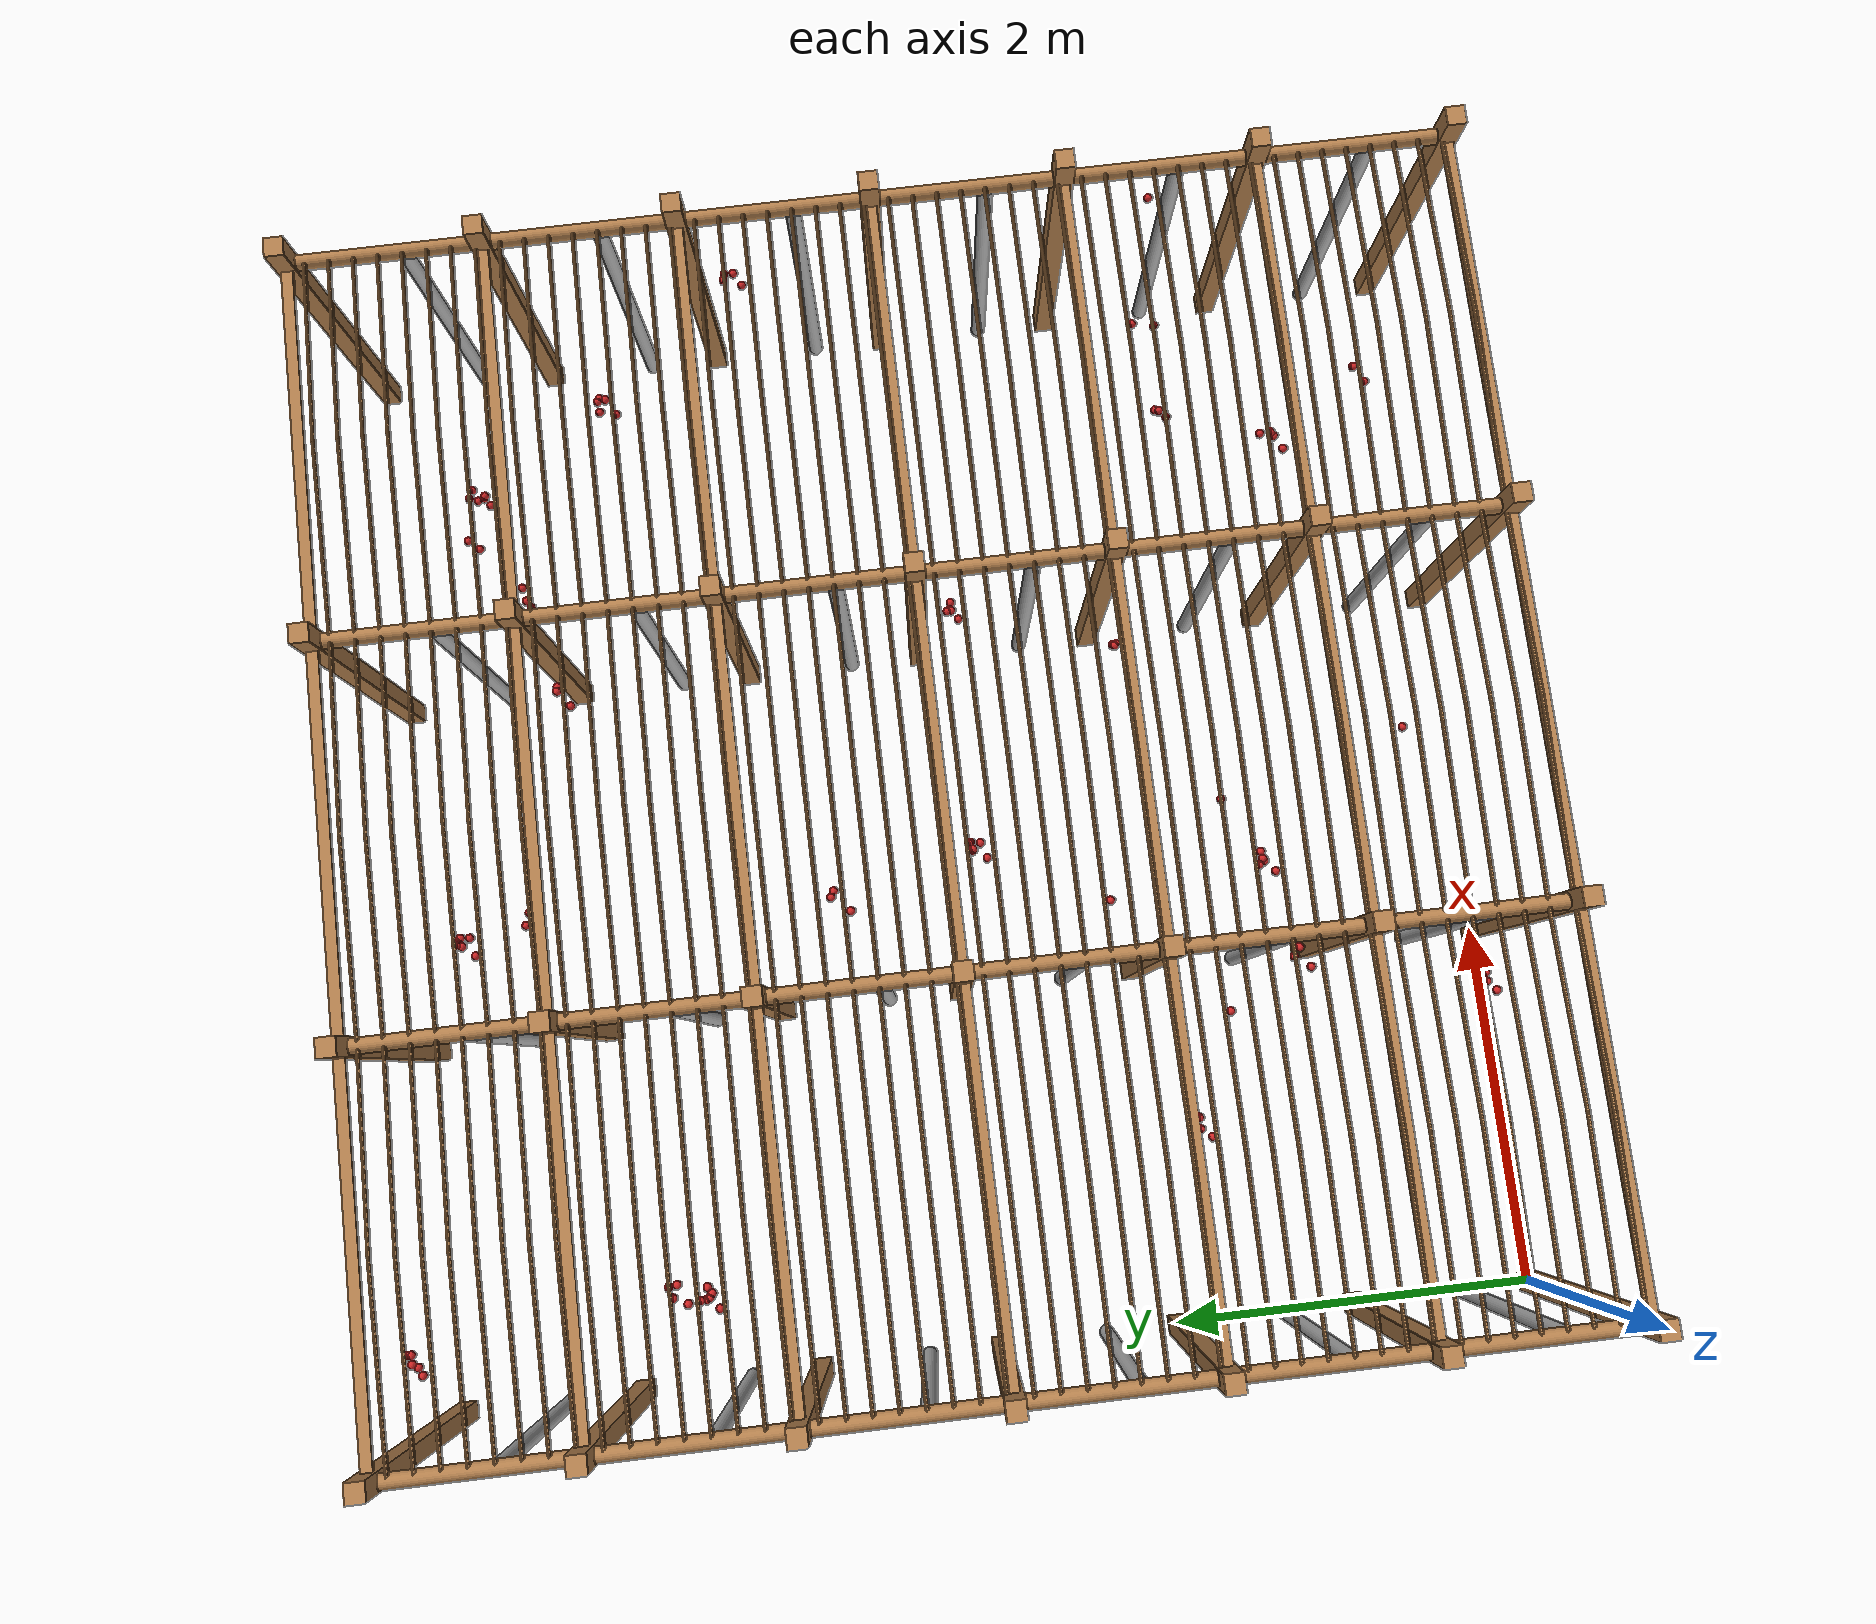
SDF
<?xml version='1.0'?>
<!-- Pergola model with 4 rows of 6 trees; 100 fruit; 8 vines per base branch -->
<sdf version='1.4'>
  <model name="pergola">

		<include>
			<name>post_0</name>
			<pose>0.0 0.0 0 0 0 0</pose>
			<uri>model://post</uri>
		</include>

		<include>
			<name>post_1</name>
			<pose>0.0 1.0 0 0 0 0</pose>
			<uri>model://post</uri>
		</include>

		<include>
			<name>post_2</name>
			<pose>0.0 2.0 0 0 0 0</pose>
			<uri>model://post</uri>
		</include>

		<include>
			<name>post_3</name>
			<pose>0.0 3.0 0 0 0 0</pose>
			<uri>model://post</uri>
		</include>

		<include>
			<name>post_4</name>
			<pose>0.0 4.0 0 0 0 0</pose>
			<uri>model://post</uri>
		</include>

		<include>
			<name>post_5</name>
			<pose>0.0 5.0 0 0 0 0</pose>
			<uri>model://post</uri>
		</include>

		<include>
			<name>post_6</name>
			<pose>0.0 6.0 0 0 0 0</pose>
			<uri>model://post</uri>
		</include>

		<include>
			<name>post_7</name>
			<pose>2.0 0.0 0 0 0 0</pose>
			<uri>model://post</uri>
		</include>

		<include>
			<name>post_8</name>
			<pose>2.0 1.0 0 0 0 0</pose>
			<uri>model://post</uri>
		</include>

		<include>
			<name>post_9</name>
			<pose>2.0 2.0 0 0 0 0</pose>
			<uri>model://post</uri>
		</include>

		<include>
			<name>post_10</name>
			<pose>2.0 3.0 0 0 0 0</pose>
			<uri>model://post</uri>
		</include>

		<include>
			<name>post_11</name>
			<pose>2.0 4.0 0 0 0 0</pose>
			<uri>model://post</uri>
		</include>

		<include>
			<name>post_12</name>
			<pose>2.0 5.0 0 0 0 0</pose>
			<uri>model://post</uri>
		</include>

		<include>
			<name>post_13</name>
			<pose>2.0 6.0 0 0 0 0</pose>
			<uri>model://post</uri>
		</include>

		<include>
			<name>post_14</name>
			<pose>4.0 0.0 0 0 0 0</pose>
			<uri>model://post</uri>
		</include>

		<include>
			<name>post_15</name>
			<pose>4.0 1.0 0 0 0 0</pose>
			<uri>model://post</uri>
		</include>

		<include>
			<name>post_16</name>
			<pose>4.0 2.0 0 0 0 0</pose>
			<uri>model://post</uri>
		</include>

		<include>
			<name>post_17</name>
			<pose>4.0 3.0 0 0 0 0</pose>
			<uri>model://post</uri>
		</include>

		<include>
			<name>post_18</name>
			<pose>4.0 4.0 0 0 0 0</pose>
			<uri>model://post</uri>
		</include>

		<include>
			<name>post_19</name>
			<pose>4.0 5.0 0 0 0 0</pose>
			<uri>model://post</uri>
		</include>

		<include>
			<name>post_20</name>
			<pose>4.0 6.0 0 0 0 0</pose>
			<uri>model://post</uri>
		</include>

		<include>
			<name>post_21</name>
			<pose>6.0 0.0 0 0 0 0</pose>
			<uri>model://post</uri>
		</include>

		<include>
			<name>post_22</name>
			<pose>6.0 1.0 0 0 0 0</pose>
			<uri>model://post</uri>
		</include>

		<include>
			<name>post_23</name>
			<pose>6.0 2.0 0 0 0 0</pose>
			<uri>model://post</uri>
		</include>

		<include>
			<name>post_24</name>
			<pose>6.0 3.0 0 0 0 0</pose>
			<uri>model://post</uri>
		</include>

		<include>
			<name>post_25</name>
			<pose>6.0 4.0 0 0 0 0</pose>
			<uri>model://post</uri>
		</include>

		<include>
			<name>post_26</name>
			<pose>6.0 5.0 0 0 0 0</pose>
			<uri>model://post</uri>
		</include>

		<include>
			<name>post_27</name>
			<pose>6.0 6.0 0 0 0 0</pose>
			<uri>model://post</uri>
		</include>

    <link name="beam_0">
      <pose>1.0 0.0 1.81 0 0 0</pose>
      <collision name="collision">
        <geometry><box><size>2.0 0.06 0.02</size></box></geometry>
      </collision>
      <visual name="visual">
        <geometry><box><size>2.0 0.06 0.02</size></box></geometry>
        <material><script><name>Gazebo/Wood</name></script></material>
      </visual>
    <inertial>
      <pose>0 0 0 0 0 0</pose>
      <mass>5</mass>
      <inertia>
        <ixx>0.0016666666666666668</ixx><ixy>0.0</ixy><ixz>0.0</ixz><iyy>1.6681666666666664</iyy><iyz>0.0</iyz><izz>1.6668333333333332</izz>
      </inertia>
    </inertial>
    </link>

    <link name="beam_1">
      <pose>1.0 1.0 1.81 0 0 0</pose>
      <collision name="collision">
        <geometry><box><size>2.0 0.06 0.02</size></box></geometry>
      </collision>
      <visual name="visual">
        <geometry><box><size>2.0 0.06 0.02</size></box></geometry>
        <material><script><name>Gazebo/Wood</name></script></material>
      </visual>
    <inertial>
      <pose>0 0 0 0 0 0</pose>
      <mass>5</mass>
      <inertia>
        <ixx>0.0016666666666666668</ixx><ixy>0.0</ixy><ixz>0.0</ixz><iyy>1.6681666666666664</iyy><iyz>0.0</iyz><izz>1.6668333333333332</izz>
      </inertia>
    </inertial>
    </link>

    <link name="beam_2">
      <pose>1.0 2.0 1.81 0 0 0</pose>
      <collision name="collision">
        <geometry><box><size>2.0 0.06 0.02</size></box></geometry>
      </collision>
      <visual name="visual">
        <geometry><box><size>2.0 0.06 0.02</size></box></geometry>
        <material><script><name>Gazebo/Wood</name></script></material>
      </visual>
    <inertial>
      <pose>0 0 0 0 0 0</pose>
      <mass>5</mass>
      <inertia>
        <ixx>0.0016666666666666668</ixx><ixy>0.0</ixy><ixz>0.0</ixz><iyy>1.6681666666666664</iyy><iyz>0.0</iyz><izz>1.6668333333333332</izz>
      </inertia>
    </inertial>
    </link>

    <link name="beam_3">
      <pose>1.0 3.0 1.81 0 0 0</pose>
      <collision name="collision">
        <geometry><box><size>2.0 0.06 0.02</size></box></geometry>
      </collision>
      <visual name="visual">
        <geometry><box><size>2.0 0.06 0.02</size></box></geometry>
        <material><script><name>Gazebo/Wood</name></script></material>
      </visual>
    <inertial>
      <pose>0 0 0 0 0 0</pose>
      <mass>5</mass>
      <inertia>
        <ixx>0.0016666666666666668</ixx><ixy>0.0</ixy><ixz>0.0</ixz><iyy>1.6681666666666664</iyy><iyz>0.0</iyz><izz>1.6668333333333332</izz>
      </inertia>
    </inertial>
    </link>

    <link name="beam_4">
      <pose>1.0 4.0 1.81 0 0 0</pose>
      <collision name="collision">
        <geometry><box><size>2.0 0.06 0.02</size></box></geometry>
      </collision>
      <visual name="visual">
        <geometry><box><size>2.0 0.06 0.02</size></box></geometry>
        <material><script><name>Gazebo/Wood</name></script></material>
      </visual>
    <inertial>
      <pose>0 0 0 0 0 0</pose>
      <mass>5</mass>
      <inertia>
        <ixx>0.0016666666666666668</ixx><ixy>0.0</ixy><ixz>0.0</ixz><iyy>1.6681666666666664</iyy><iyz>0.0</iyz><izz>1.6668333333333332</izz>
      </inertia>
    </inertial>
    </link>

    <link name="beam_5">
      <pose>1.0 5.0 1.81 0 0 0</pose>
      <collision name="collision">
        <geometry><box><size>2.0 0.06 0.02</size></box></geometry>
      </collision>
      <visual name="visual">
        <geometry><box><size>2.0 0.06 0.02</size></box></geometry>
        <material><script><name>Gazebo/Wood</name></script></material>
      </visual>
    <inertial>
      <pose>0 0 0 0 0 0</pose>
      <mass>5</mass>
      <inertia>
        <ixx>0.0016666666666666668</ixx><ixy>0.0</ixy><ixz>0.0</ixz><iyy>1.6681666666666664</iyy><iyz>0.0</iyz><izz>1.6668333333333332</izz>
      </inertia>
    </inertial>
    </link>

    <link name="beam_6">
      <pose>1.0 6.0 1.81 0 0 0</pose>
      <collision name="collision">
        <geometry><box><size>2.0 0.06 0.02</size></box></geometry>
      </collision>
      <visual name="visual">
        <geometry><box><size>2.0 0.06 0.02</size></box></geometry>
        <material><script><name>Gazebo/Wood</name></script></material>
      </visual>
    <inertial>
      <pose>0 0 0 0 0 0</pose>
      <mass>5</mass>
      <inertia>
        <ixx>0.0016666666666666668</ixx><ixy>0.0</ixy><ixz>0.0</ixz><iyy>1.6681666666666664</iyy><iyz>0.0</iyz><izz>1.6668333333333332</izz>
      </inertia>
    </inertial>
    </link>

    <link name="beam_7">
      <pose>3.0 0.0 1.81 0 0 0</pose>
      <collision name="collision">
        <geometry><box><size>2.0 0.06 0.02</size></box></geometry>
      </collision>
      <visual name="visual">
        <geometry><box><size>2.0 0.06 0.02</size></box></geometry>
        <material><script><name>Gazebo/Wood</name></script></material>
      </visual>
    <inertial>
      <pose>0 0 0 0 0 0</pose>
      <mass>5</mass>
      <inertia>
        <ixx>0.0016666666666666668</ixx><ixy>0.0</ixy><ixz>0.0</ixz><iyy>1.6681666666666664</iyy><iyz>0.0</iyz><izz>1.6668333333333332</izz>
      </inertia>
    </inertial>
    </link>

    <link name="beam_8">
      <pose>3.0 1.0 1.81 0 0 0</pose>
      <collision name="collision">
        <geometry><box><size>2.0 0.06 0.02</size></box></geometry>
      </collision>
      <visual name="visual">
        <geometry><box><size>2.0 0.06 0.02</size></box></geometry>
        <material><script><name>Gazebo/Wood</name></script></material>
      </visual>
    <inertial>
      <pose>0 0 0 0 0 0</pose>
      <mass>5</mass>
      <inertia>
        <ixx>0.0016666666666666668</ixx><ixy>0.0</ixy><ixz>0.0</ixz><iyy>1.6681666666666664</iyy><iyz>0.0</iyz><izz>1.6668333333333332</izz>
      </inertia>
    </inertial>
    </link>

    <link name="beam_9">
      <pose>3.0 2.0 1.81 0 0 0</pose>
      <collision name="collision">
        <geometry><box><size>2.0 0.06 0.02</size></box></geometry>
      </collision>
      <visual name="visual">
        <geometry><box><size>2.0 0.06 0.02</size></box></geometry>
        <material><script><name>Gazebo/Wood</name></script></material>
      </visual>
    <inertial>
      <pose>0 0 0 0 0 0</pose>
      <mass>5</mass>
      <inertia>
        <ixx>0.0016666666666666668</ixx><ixy>0.0</ixy><ixz>0.0</ixz><iyy>1.6681666666666664</iyy><iyz>0.0</iyz><izz>1.6668333333333332</izz>
      </inertia>
    </inertial>
    </link>

    <link name="beam_10">
      <pose>3.0 3.0 1.81 0 0 0</pose>
      <collision name="collision">
        <geometry><box><size>2.0 0.06 0.02</size></box></geometry>
      </collision>
      <visual name="visual">
        <geometry><box><size>2.0 0.06 0.02</size></box></geometry>
        <material><script><name>Gazebo/Wood</name></script></material>
      </visual>
    <inertial>
      <pose>0 0 0 0 0 0</pose>
      <mass>5</mass>
      <inertia>
        <ixx>0.0016666666666666668</ixx><ixy>0.0</ixy><ixz>0.0</ixz><iyy>1.6681666666666664</iyy><iyz>0.0</iyz><izz>1.6668333333333332</izz>
      </inertia>
    </inertial>
    </link>

    <link name="beam_11">
      <pose>3.0 4.0 1.81 0 0 0</pose>
      <collision name="collision">
        <geometry><box><size>2.0 0.06 0.02</size></box></geometry>
      </collision>
      <visual name="visual">
        <geometry><box><size>2.0 0.06 0.02</size></box></geometry>
        <material><script><name>Gazebo/Wood</name></script></material>
      </visual>
    <inertial>
      <pose>0 0 0 0 0 0</pose>
      <mass>5</mass>
      <inertia>
        <ixx>0.0016666666666666668</ixx><ixy>0.0</ixy><ixz>0.0</ixz><iyy>1.6681666666666664</iyy><iyz>0.0</iyz><izz>1.6668333333333332</izz>
      </inertia>
    </inertial>
    </link>

    <link name="beam_12">
      <pose>3.0 5.0 1.81 0 0 0</pose>
      <collision name="collision">
        <geometry><box><size>2.0 0.06 0.02</size></box></geometry>
      </collision>
      <visual name="visual">
        <geometry><box><size>2.0 0.06 0.02</size></box></geometry>
        <material><script><name>Gazebo/Wood</name></script></material>
      </visual>
    <inertial>
      <pose>0 0 0 0 0 0</pose>
      <mass>5</mass>
      <inertia>
        <ixx>0.0016666666666666668</ixx><ixy>0.0</ixy><ixz>0.0</ixz><iyy>1.6681666666666664</iyy><iyz>0.0</iyz><izz>1.6668333333333332</izz>
      </inertia>
    </inertial>
    </link>

    <link name="beam_13">
      <pose>3.0 6.0 1.81 0 0 0</pose>
      <collision name="collision">
        <geometry><box><size>2.0 0.06 0.02</size></box></geometry>
      </collision>
      <visual name="visual">
        <geometry><box><size>2.0 0.06 0.02</size></box></geometry>
        <material><script><name>Gazebo/Wood</name></script></material>
      </visual>
    <inertial>
      <pose>0 0 0 0 0 0</pose>
      <mass>5</mass>
      <inertia>
        <ixx>0.0016666666666666668</ixx><ixy>0.0</ixy><ixz>0.0</ixz><iyy>1.6681666666666664</iyy><iyz>0.0</iyz><izz>1.6668333333333332</izz>
      </inertia>
    </inertial>
    </link>

    <link name="beam_14">
      <pose>5.0 0.0 1.81 0 0 0</pose>
      <collision name="collision">
        <geometry><box><size>2.0 0.06 0.02</size></box></geometry>
      </collision>
      <visual name="visual">
        <geometry><box><size>2.0 0.06 0.02</size></box></geometry>
        <material><script><name>Gazebo/Wood</name></script></material>
      </visual>
    <inertial>
      <pose>0 0 0 0 0 0</pose>
      <mass>5</mass>
      <inertia>
        <ixx>0.0016666666666666668</ixx><ixy>0.0</ixy><ixz>0.0</ixz><iyy>1.6681666666666664</iyy><iyz>0.0</iyz><izz>1.6668333333333332</izz>
      </inertia>
    </inertial>
    </link>

    <link name="beam_15">
      <pose>5.0 1.0 1.81 0 0 0</pose>
      <collision name="collision">
        <geometry><box><size>2.0 0.06 0.02</size></box></geometry>
      </collision>
      <visual name="visual">
        <geometry><box><size>2.0 0.06 0.02</size></box></geometry>
        <material><script><name>Gazebo/Wood</name></script></material>
      </visual>
    <inertial>
      <pose>0 0 0 0 0 0</pose>
      <mass>5</mass>
      <inertia>
        <ixx>0.0016666666666666668</ixx><ixy>0.0</ixy><ixz>0.0</ixz><iyy>1.6681666666666664</iyy><iyz>0.0</iyz><izz>1.6668333333333332</izz>
      </inertia>
    </inertial>
    </link>

    <link name="beam_16">
      <pose>5.0 2.0 1.81 0 0 0</pose>
      <collision name="collision">
        <geometry><box><size>2.0 0.06 0.02</size></box></geometry>
      </collision>
      <visual name="visual">
        <geometry><box><size>2.0 0.06 0.02</size></box></geometry>
        <material><script><name>Gazebo/Wood</name></script></material>
      </visual>
    <inertial>
      <pose>0 0 0 0 0 0</pose>
      <mass>5</mass>
      <inertia>
        <ixx>0.0016666666666666668</ixx><ixy>0.0</ixy><ixz>0.0</ixz><iyy>1.6681666666666664</iyy><iyz>0.0</iyz><izz>1.6668333333333332</izz>
      </inertia>
    </inertial>
    </link>

    <link name="beam_17">
      <pose>5.0 3.0 1.81 0 0 0</pose>
      <collision name="collision">
        <geometry><box><size>2.0 0.06 0.02</size></box></geometry>
      </collision>
      <visual name="visual">
        <geometry><box><size>2.0 0.06 0.02</size></box></geometry>
        <material><script><name>Gazebo/Wood</name></script></material>
      </visual>
    <inertial>
      <pose>0 0 0 0 0 0</pose>
      <mass>5</mass>
      <inertia>
        <ixx>0.0016666666666666668</ixx><ixy>0.0</ixy><ixz>0.0</ixz><iyy>1.6681666666666664</iyy><iyz>0.0</iyz><izz>1.6668333333333332</izz>
      </inertia>
    </inertial>
    </link>

    <link name="beam_18">
      <pose>5.0 4.0 1.81 0 0 0</pose>
      <collision name="collision">
        <geometry><box><size>2.0 0.06 0.02</size></box></geometry>
      </collision>
      <visual name="visual">
        <geometry><box><size>2.0 0.06 0.02</size></box></geometry>
        <material><script><name>Gazebo/Wood</name></script></material>
      </visual>
    <inertial>
      <pose>0 0 0 0 0 0</pose>
      <mass>5</mass>
      <inertia>
        <ixx>0.0016666666666666668</ixx><ixy>0.0</ixy><ixz>0.0</ixz><iyy>1.6681666666666664</iyy><iyz>0.0</iyz><izz>1.6668333333333332</izz>
      </inertia>
    </inertial>
    </link>

    <link name="beam_19">
      <pose>5.0 5.0 1.81 0 0 0</pose>
      <collision name="collision">
        <geometry><box><size>2.0 0.06 0.02</size></box></geometry>
      </collision>
      <visual name="visual">
        <geometry><box><size>2.0 0.06 0.02</size></box></geometry>
        <material><script><name>Gazebo/Wood</name></script></material>
      </visual>
    <inertial>
      <pose>0 0 0 0 0 0</pose>
      <mass>5</mass>
      <inertia>
        <ixx>0.0016666666666666668</ixx><ixy>0.0</ixy><ixz>0.0</ixz><iyy>1.6681666666666664</iyy><iyz>0.0</iyz><izz>1.6668333333333332</izz>
      </inertia>
    </inertial>
    </link>

    <link name="beam_20">
      <pose>5.0 6.0 1.81 0 0 0</pose>
      <collision name="collision">
        <geometry><box><size>2.0 0.06 0.02</size></box></geometry>
      </collision>
      <visual name="visual">
        <geometry><box><size>2.0 0.06 0.02</size></box></geometry>
        <material><script><name>Gazebo/Wood</name></script></material>
      </visual>
    <inertial>
      <pose>0 0 0 0 0 0</pose>
      <mass>5</mass>
      <inertia>
        <ixx>0.0016666666666666668</ixx><ixy>0.0</ixy><ixz>0.0</ixz><iyy>1.6681666666666664</iyy><iyz>0.0</iyz><izz>1.6668333333333332</izz>
      </inertia>
    </inertial>
    </link>

		<include>
			<name>tree_0</name>
			<pose>0.0 0.4 0 0 0 0</pose>
			<uri>model://tree_trunk</uri>
		</include>

		<include>
			<name>tree_1</name>
			<pose>0.0 1.4 0 0 0 0</pose>
			<uri>model://tree_trunk</uri>
		</include>

		<include>
			<name>tree_2</name>
			<pose>0.0 2.4 0 0 0 0</pose>
			<uri>model://tree_trunk</uri>
		</include>

		<include>
			<name>tree_3</name>
			<pose>0.0 3.4 0 0 0 0</pose>
			<uri>model://tree_trunk</uri>
		</include>

		<include>
			<name>tree_4</name>
			<pose>0.0 4.4 0 0 0 0</pose>
			<uri>model://tree_trunk</uri>
		</include>

		<include>
			<name>tree_5</name>
			<pose>0.0 5.4 0 0 0 0</pose>
			<uri>model://tree_trunk</uri>
		</include>

		<include>
			<name>tree_6</name>
			<pose>2.0 0.4 0 0 0 0</pose>
			<uri>model://tree_trunk</uri>
		</include>

		<include>
			<name>tree_7</name>
			<pose>2.0 1.4 0 0 0 0</pose>
			<uri>model://tree_trunk</uri>
		</include>

		<include>
			<name>tree_8</name>
			<pose>2.0 2.4 0 0 0 0</pose>
			<uri>model://tree_trunk</uri>
		</include>

		<include>
			<name>tree_9</name>
			<pose>2.0 3.4 0 0 0 0</pose>
			<uri>model://tree_trunk</uri>
		</include>

		<include>
			<name>tree_10</name>
			<pose>2.0 4.4 0 0 0 0</pose>
			<uri>model://tree_trunk</uri>
		</include>

		<include>
			<name>tree_11</name>
			<pose>2.0 5.4 0 0 0 0</pose>
			<uri>model://tree_trunk</uri>
		</include>

		<include>
			<name>tree_12</name>
			<pose>4.0 0.4 0 0 0 0</pose>
			<uri>model://tree_trunk</uri>
		</include>

		<include>
			<name>tree_13</name>
			<pose>4.0 1.4 0 0 0 0</pose>
			<uri>model://tree_trunk</uri>
		</include>

		<include>
			<name>tree_14</name>
			<pose>4.0 2.4 0 0 0 0</pose>
			<uri>model://tree_trunk</uri>
		</include>

		<include>
			<name>tree_15</name>
			<pose>4.0 3.4 0 0 0 0</pose>
			<uri>model://tree_trunk</uri>
		</include>

		<include>
			<name>tree_16</name>
			<pose>4.0 4.4 0 0 0 0</pose>
			<uri>model://tree_trunk</uri>
		</include>

		<include>
			<name>tree_17</name>
			<pose>4.0 5.4 0 0 0 0</pose>
			<uri>model://tree_trunk</uri>
		</include>

		<include>
			<name>tree_18</name>
			<pose>6.0 0.4 0 0 0 0</pose>
			<uri>model://tree_trunk</uri>
		</include>

		<include>
			<name>tree_19</name>
			<pose>6.0 1.4 0 0 0 0</pose>
			<uri>model://tree_trunk</uri>
		</include>

		<include>
			<name>tree_20</name>
			<pose>6.0 2.4 0 0 0 0</pose>
			<uri>model://tree_trunk</uri>
		</include>

		<include>
			<name>tree_21</name>
			<pose>6.0 3.4 0 0 0 0</pose>
			<uri>model://tree_trunk</uri>
		</include>

		<include>
			<name>tree_22</name>
			<pose>6.0 4.4 0 0 0 0</pose>
			<uri>model://tree_trunk</uri>
		</include>

		<include>
			<name>tree_23</name>
			<pose>6.0 5.4 0 0 0 0</pose>
			<uri>model://tree_trunk</uri>
		</include>

    <link name="baseBranch_0">
      <pose>0.0 0.5 1.8 1.5707963267948966 0 0</pose>
      <collision name="collision">
        <geometry><cylinder><radius>0.04</radius> <length>0.94</length></cylinder></geometry>
      </collision>
      <visual name="visual">
        <geometry><cylinder><radius>0.04</radius> <length>0.94</length></cylinder></geometry>
        <material><script><name>Gazebo/WoodFloor</name></script></material>
      </visual>
    <inertial>
      <pose>0 0 0 0 0 0</pose>
      <mass>10</mass>
      <inertia>
        <ixx>0.7403333333333334</ixx><ixy>0.0</ixy><ixz>0.0</ixz><iyy>0.7403333333333334</iyy><iyz>0.0</iyz><izz>0.008</izz>
      </inertia>
    </inertial>
    </link>

    <link name="baseBranch_1">
      <pose>0.0 1.5 1.8 1.5707963267948966 0 0</pose>
      <collision name="collision">
        <geometry><cylinder><radius>0.04</radius> <length>0.94</length></cylinder></geometry>
      </collision>
      <visual name="visual">
        <geometry><cylinder><radius>0.04</radius> <length>0.94</length></cylinder></geometry>
        <material><script><name>Gazebo/WoodFloor</name></script></material>
      </visual>
    <inertial>
      <pose>0 0 0 0 0 0</pose>
      <mass>10</mass>
      <inertia>
        <ixx>0.7403333333333334</ixx><ixy>0.0</ixy><ixz>0.0</ixz><iyy>0.7403333333333334</iyy><iyz>0.0</iyz><izz>0.008</izz>
      </inertia>
    </inertial>
    </link>

    <link name="baseBranch_2">
      <pose>0.0 2.5 1.8 1.5707963267948966 0 0</pose>
      <collision name="collision">
        <geometry><cylinder><radius>0.04</radius> <length>0.94</length></cylinder></geometry>
      </collision>
      <visual name="visual">
        <geometry><cylinder><radius>0.04</radius> <length>0.94</length></cylinder></geometry>
        <material><script><name>Gazebo/WoodFloor</name></script></material>
      </visual>
    <inertial>
      <pose>0 0 0 0 0 0</pose>
      <mass>10</mass>
      <inertia>
        <ixx>0.7403333333333334</ixx><ixy>0.0</ixy><ixz>0.0</ixz><iyy>0.7403333333333334</iyy><iyz>0.0</iyz><izz>0.008</izz>
      </inertia>
    </inertial>
    </link>

    <link name="baseBranch_3">
      <pose>0.0 3.5 1.8 1.5707963267948966 0 0</pose>
      <collision name="collision">
        <geometry><cylinder><radius>0.04</radius> <length>0.94</length></cylinder></geometry>
      </collision>
      <visual name="visual">
        <geometry><cylinder><radius>0.04</radius> <length>0.94</length></cylinder></geometry>
        <material><script><name>Gazebo/WoodFloor</name></script></material>
      </visual>
    <inertial>
      <pose>0 0 0 0 0 0</pose>
      <mass>10</mass>
      <inertia>
        <ixx>0.7403333333333334</ixx><ixy>0.0</ixy><ixz>0.0</ixz><iyy>0.7403333333333334</iyy><iyz>0.0</iyz><izz>0.008</izz>
      </inertia>
    </inertial>
    </link>

    <link name="baseBranch_4">
      <pose>0.0 4.5 1.8 1.5707963267948966 0 0</pose>
      <collision name="collision">
        <geometry><cylinder><radius>0.04</radius> <length>0.94</length></cylinder></geometry>
      </collision>
      <visual name="visual">
        <geometry><cylinder><radius>0.04</radius> <length>0.94</length></cylinder></geometry>
        <material><script><name>Gazebo/WoodFloor</name></script></material>
      </visual>
    <inertial>
      <pose>0 0 0 0 0 0</pose>
      <mass>10</mass>
      <inertia>
        <ixx>0.7403333333333334</ixx><ixy>0.0</ixy><ixz>0.0</ixz><iyy>0.7403333333333334</iyy><iyz>0.0</iyz><izz>0.008</izz>
      </inertia>
    </inertial>
    </link>

    <link name="baseBranch_5">
      <pose>0.0 5.5 1.8 1.5707963267948966 0 0</pose>
      <collision name="collision">
        <geometry><cylinder><radius>0.04</radius> <length>0.94</length></cylinder></geometry>
      </collision>
      <visual name="visual">
        <geometry><cylinder><radius>0.04</radius> <length>0.94</length></cylinder></geometry>
        <material><script><name>Gazebo/WoodFloor</name></script></material>
      </visual>
    <inertial>
      <pose>0 0 0 0 0 0</pose>
      <mass>10</mass>
      <inertia>
        <ixx>0.7403333333333334</ixx><ixy>0.0</ixy><ixz>0.0</ixz><iyy>0.7403333333333334</iyy><iyz>0.0</iyz><izz>0.008</izz>
      </inertia>
    </inertial>
    </link>

    <link name="baseBranch_6">
      <pose>2.0 0.5 1.8 1.5707963267948966 0 0</pose>
      <collision name="collision">
        <geometry><cylinder><radius>0.04</radius> <length>0.94</length></cylinder></geometry>
      </collision>
      <visual name="visual">
        <geometry><cylinder><radius>0.04</radius> <length>0.94</length></cylinder></geometry>
        <material><script><name>Gazebo/WoodFloor</name></script></material>
      </visual>
    <inertial>
      <pose>0 0 0 0 0 0</pose>
      <mass>10</mass>
      <inertia>
        <ixx>0.7403333333333334</ixx><ixy>0.0</ixy><ixz>0.0</ixz><iyy>0.7403333333333334</iyy><iyz>0.0</iyz><izz>0.008</izz>
      </inertia>
    </inertial>
    </link>

    <link name="baseBranch_7">
      <pose>2.0 1.5 1.8 1.5707963267948966 0 0</pose>
      <collision name="collision">
        <geometry><cylinder><radius>0.04</radius> <length>0.94</length></cylinder></geometry>
      </collision>
      <visual name="visual">
        <geometry><cylinder><radius>0.04</radius> <length>0.94</length></cylinder></geometry>
        <material><script><name>Gazebo/WoodFloor</name></script></material>
      </visual>
    <inertial>
      <pose>0 0 0 0 0 0</pose>
      <mass>10</mass>
      <inertia>
        <ixx>0.7403333333333334</ixx><ixy>0.0</ixy><ixz>0.0</ixz><iyy>0.7403333333333334</iyy><iyz>0.0</iyz><izz>0.008</izz>
      </inertia>
    </inertial>
    </link>

    <link name="baseBranch_8">
      <pose>2.0 2.5 1.8 1.5707963267948966 0 0</pose>
      <collision name="collision">
        <geometry><cylinder><radius>0.04</radius> <length>0.94</length></cylinder></geometry>
      </collision>
      <visual name="visual">
        <geometry><cylinder><radius>0.04</radius> <length>0.94</length></cylinder></geometry>
        <material><script><name>Gazebo/WoodFloor</name></script></material>
      </visual>
    <inertial>
      <pose>0 0 0 0 0 0</pose>
      <mass>10</mass>
      <inertia>
        <ixx>0.7403333333333334</ixx><ixy>0.0</ixy><ixz>0.0</ixz><iyy>0.7403333333333334</iyy><iyz>0.0</iyz><izz>0.008</izz>
      </inertia>
    </inertial>
    </link>

    <link name="baseBranch_9">
      <pose>2.0 3.5 1.8 1.5707963267948966 0 0</pose>
      <collision name="collision">
        <geometry><cylinder><radius>0.04</radius> <length>0.94</length></cylinder></geometry>
      </collision>
      <visual name="visual">
        <geometry><cylinder><radius>0.04</radius> <length>0.94</length></cylinder></geometry>
        <material><script><name>Gazebo/WoodFloor</name></script></material>
      </visual>
    <inertial>
      <pose>0 0 0 0 0 0</pose>
      <mass>10</mass>
      <inertia>
        <ixx>0.7403333333333334</ixx><ixy>0.0</ixy><ixz>0.0</ixz><iyy>0.7403333333333334</iyy><iyz>0.0</iyz><izz>0.008</izz>
      </inertia>
    </inertial>
    </link>

    <link name="baseBranch_10">
      <pose>2.0 4.5 1.8 1.5707963267948966 0 0</pose>
      <collision name="collision">
        <geometry><cylinder><radius>0.04</radius> <length>0.94</length></cylinder></geometry>
      </collision>
      <visual name="visual">
        <geometry><cylinder><radius>0.04</radius> <length>0.94</length></cylinder></geometry>
        <material><script><name>Gazebo/WoodFloor</name></script></material>
      </visual>
    <inertial>
      <pose>0 0 0 0 0 0</pose>
      <mass>10</mass>
      <inertia>
        <ixx>0.7403333333333334</ixx><ixy>0.0</ixy><ixz>0.0</ixz><iyy>0.7403333333333334</iyy><iyz>0.0</iyz><izz>0.008</izz>
      </inertia>
    </inertial>
    </link>

    <link name="baseBranch_11">
      <pose>2.0 5.5 1.8 1.5707963267948966 0 0</pose>
      <collision name="collision">
        <geometry><cylinder><radius>0.04</radius> <length>0.94</length></cylinder></geometry>
      </collision>
      <visual name="visual">
        <geometry><cylinder><radius>0.04</radius> <length>0.94</length></cylinder></geometry>
        <material><script><name>Gazebo/WoodFloor</name></script></material>
      </visual>
    <inertial>
      <pose>0 0 0 0 0 0</pose>
      <mass>10</mass>
      <inertia>
        <ixx>0.7403333333333334</ixx><ixy>0.0</ixy><ixz>0.0</ixz><iyy>0.7403333333333334</iyy><iyz>0.0</iyz><izz>0.008</izz>
      </inertia>
    </inertial>
    </link>

    <link name="baseBranch_12">
      <pose>4.0 0.5 1.8 1.5707963267948966 0 0</pose>
      <collision name="collision">
        <geometry><cylinder><radius>0.04</radius> <length>0.94</length></cylinder></geometry>
      </collision>
      <visual name="visual">
        <geometry><cylinder><radius>0.04</radius> <length>0.94</length></cylinder></geometry>
        <material><script><name>Gazebo/WoodFloor</name></script></material>
      </visual>
    <inertial>
      <pose>0 0 0 0 0 0</pose>
      <mass>10</mass>
      <inertia>
        <ixx>0.7403333333333334</ixx><ixy>0.0</ixy><ixz>0.0</ixz><iyy>0.7403333333333334</iyy><iyz>0.0</iyz><izz>0.008</izz>
      </inertia>
    </inertial>
    </link>

    <link name="baseBranch_13">
      <pose>4.0 1.5 1.8 1.5707963267948966 0 0</pose>
      <collision name="collision">
        <geometry><cylinder><radius>0.04</radius> <length>0.94</length></cylinder></geometry>
      </collision>
      <visual name="visual">
        <geometry><cylinder><radius>0.04</radius> <length>0.94</length></cylinder></geometry>
        <material><script><name>Gazebo/WoodFloor</name></script></material>
      </visual>
    <inertial>
      <pose>0 0 0 0 0 0</pose>
      <mass>10</mass>
      <inertia>
        <ixx>0.7403333333333334</ixx><ixy>0.0</ixy><ixz>0.0</ixz><iyy>0.7403333333333334</iyy><iyz>0.0</iyz><izz>0.008</izz>
      </inertia>
    </inertial>
    </link>

    <link name="baseBranch_14">
      <pose>4.0 2.5 1.8 1.5707963267948966 0 0</pose>
      <collision name="collision">
        <geometry><cylinder><radius>0.04</radius> <length>0.94</length></cylinder></geometry>
      </collision>
      <visual name="visual">
        <geometry><cylinder><radius>0.04</radius> <length>0.94</length></cylinder></geometry>
        <material><script><name>Gazebo/WoodFloor</name></script></material>
      </visual>
    <inertial>
      <pose>0 0 0 0 0 0</pose>
      <mass>10</mass>
      <inertia>
        <ixx>0.7403333333333334</ixx><ixy>0.0</ixy><ixz>0.0</ixz><iyy>0.7403333333333334</iyy><iyz>0.0</iyz><izz>0.008</izz>
      </inertia>
    </inertial>
    </link>

    <link name="baseBranch_15">
      <pose>4.0 3.5 1.8 1.5707963267948966 0 0</pose>
      <collision name="collision">
        <geometry><cylinder><radius>0.04</radius> <length>0.94</length></cylinder></geometry>
      </collision>
      <visual name="visual">
        <geometry><cylinder><radius>0.04</radius> <length>0.94</length></cylinder></geometry>
        <material><script><name>Gazebo/WoodFloor</name></script></material>
      </visual>
    <inertial>
      <pose>0 0 0 0 0 0</pose>
      <mass>10</mass>
      <inertia>
        <ixx>0.7403333333333334</ixx><ixy>0.0</ixy><ixz>0.0</ixz><iyy>0.7403333333333334</iyy><iyz>0.0</iyz><izz>0.008</izz>
      </inertia>
    </inertial>
    </link>

    <link name="baseBranch_16">
      <pose>4.0 4.5 1.8 1.5707963267948966 0 0</pose>
      <collision name="collision">
        <geometry><cylinder><radius>0.04</radius> <length>0.94</length></cylinder></geometry>
      </collision>
      <visual name="visual">
        <geometry><cylinder><radius>0.04</radius> <length>0.94</length></cylinder></geometry>
        <material><script><name>Gazebo/WoodFloor</name></script></material>
      </visual>
    <inertial>
      <pose>0 0 0 0 0 0</pose>
      <mass>10</mass>
      <inertia>
        <ixx>0.7403333333333334</ixx><ixy>0.0</ixy><ixz>0.0</ixz><iyy>0.7403333333333334</iyy><iyz>0.0</iyz><izz>0.008</izz>
      </inertia>
    </inertial>
    </link>

    <link name="baseBranch_17">
      <pose>4.0 5.5 1.8 1.5707963267948966 0 0</pose>
      <collision name="collision">
        <geometry><cylinder><radius>0.04</radius> <length>0.94</length></cylinder></geometry>
      </collision>
      <visual name="visual">
        <geometry><cylinder><radius>0.04</radius> <length>0.94</length></cylinder></geometry>
        <material><script><name>Gazebo/WoodFloor</name></script></material>
      </visual>
    <inertial>
      <pose>0 0 0 0 0 0</pose>
      <mass>10</mass>
      <inertia>
        <ixx>0.7403333333333334</ixx><ixy>0.0</ixy><ixz>0.0</ixz><iyy>0.7403333333333334</iyy><iyz>0.0</iyz><izz>0.008</izz>
      </inertia>
    </inertial>
    </link>

    <link name="baseBranch_18">
      <pose>6.0 0.5 1.8 1.5707963267948966 0 0</pose>
      <collision name="collision">
        <geometry><cylinder><radius>0.04</radius> <length>0.94</length></cylinder></geometry>
      </collision>
      <visual name="visual">
        <geometry><cylinder><radius>0.04</radius> <length>0.94</length></cylinder></geometry>
        <material><script><name>Gazebo/WoodFloor</name></script></material>
      </visual>
    <inertial>
      <pose>0 0 0 0 0 0</pose>
      <mass>10</mass>
      <inertia>
        <ixx>0.7403333333333334</ixx><ixy>0.0</ixy><ixz>0.0</ixz><iyy>0.7403333333333334</iyy><iyz>0.0</iyz><izz>0.008</izz>
      </inertia>
    </inertial>
    </link>

    <link name="baseBranch_19">
      <pose>6.0 1.5 1.8 1.5707963267948966 0 0</pose>
      <collision name="collision">
        <geometry><cylinder><radius>0.04</radius> <length>0.94</length></cylinder></geometry>
      </collision>
      <visual name="visual">
        <geometry><cylinder><radius>0.04</radius> <length>0.94</length></cylinder></geometry>
        <material><script><name>Gazebo/WoodFloor</name></script></material>
      </visual>
    <inertial>
      <pose>0 0 0 0 0 0</pose>
      <mass>10</mass>
      <inertia>
        <ixx>0.7403333333333334</ixx><ixy>0.0</ixy><ixz>0.0</ixz><iyy>0.7403333333333334</iyy><iyz>0.0</iyz><izz>0.008</izz>
      </inertia>
    </inertial>
    </link>

    <link name="baseBranch_20">
      <pose>6.0 2.5 1.8 1.5707963267948966 0 0</pose>
      <collision name="collision">
        <geometry><cylinder><radius>0.04</radius> <length>0.94</length></cylinder></geometry>
      </collision>
      <visual name="visual">
        <geometry><cylinder><radius>0.04</radius> <length>0.94</length></cylinder></geometry>
        <material><script><name>Gazebo/WoodFloor</name></script></material>
      </visual>
    <inertial>
      <pose>0 0 0 0 0 0</pose>
      <mass>10</mass>
      <inertia>
        <ixx>0.7403333333333334</ixx><ixy>0.0</ixy><ixz>0.0</ixz><iyy>0.7403333333333334</iyy><iyz>0.0</iyz><izz>0.008</izz>
      </inertia>
    </inertial>
    </link>

    <link name="baseBranch_21">
      <pose>6.0 3.5 1.8 1.5707963267948966 0 0</pose>
      <collision name="collision">
        <geometry><cylinder><radius>0.04</radius> <length>0.94</length></cylinder></geometry>
      </collision>
      <visual name="visual">
        <geometry><cylinder><radius>0.04</radius> <length>0.94</length></cylinder></geometry>
        <material><script><name>Gazebo/WoodFloor</name></script></material>
      </visual>
    <inertial>
      <pose>0 0 0 0 0 0</pose>
      <mass>10</mass>
      <inertia>
        <ixx>0.7403333333333334</ixx><ixy>0.0</ixy><ixz>0.0</ixz><iyy>0.7403333333333334</iyy><iyz>0.0</iyz><izz>0.008</izz>
      </inertia>
    </inertial>
    </link>

    <link name="baseBranch_22">
      <pose>6.0 4.5 1.8 1.5707963267948966 0 0</pose>
      <collision name="collision">
        <geometry><cylinder><radius>0.04</radius> <length>0.94</length></cylinder></geometry>
      </collision>
      <visual name="visual">
        <geometry><cylinder><radius>0.04</radius> <length>0.94</length></cylinder></geometry>
        <material><script><name>Gazebo/WoodFloor</name></script></material>
      </visual>
    <inertial>
      <pose>0 0 0 0 0 0</pose>
      <mass>10</mass>
      <inertia>
        <ixx>0.7403333333333334</ixx><ixy>0.0</ixy><ixz>0.0</ixz><iyy>0.7403333333333334</iyy><iyz>0.0</iyz><izz>0.008</izz>
      </inertia>
    </inertial>
    </link>

    <link name="baseBranch_23">
      <pose>6.0 5.5 1.8 1.5707963267948966 0 0</pose>
      <collision name="collision">
        <geometry><cylinder><radius>0.04</radius> <length>0.94</length></cylinder></geometry>
      </collision>
      <visual name="visual">
        <geometry><cylinder><radius>0.04</radius> <length>0.94</length></cylinder></geometry>
        <material><script><name>Gazebo/WoodFloor</name></script></material>
      </visual>
    <inertial>
      <pose>0 0 0 0 0 0</pose>
      <mass>10</mass>
      <inertia>
        <ixx>0.7403333333333334</ixx><ixy>0.0</ixy><ixz>0.0</ixz><iyy>0.7403333333333334</iyy><iyz>0.0</iyz><izz>0.008</izz>
      </inertia>
    </inertial>
    </link>

    <link name="vine_0">
      <pose>0.5 0.03 1.85 0 1.5208379310729538 0</pose>
      <collision name="collision">
        <geometry><cylinder><radius>0.01</radius> <length>1.0012492197250393</length></cylinder></geometry>
      </collision>
      <visual name="visual">
        <geometry><cylinder><radius>0.01</radius> <length>1.0012492197250393</length></cylinder></geometry>
        <material><script><name>Gazebo/WoodFloor</name></script></material>
      </visual>
    <inertial>
      <pose>0 0 0 0 0 0</pose>
      <mass>5</mass>
      <inertia>
        <ixx>0.41783333333333345</ixx><ixy>0.0</ixy><ixz>0.0</ixz><iyy>0.41783333333333345</iyy><iyz>0.0</iyz><izz>0.00025</izz>
      </inertia>
    </inertial>
    </link>

    <link name="vine_1">
      <pose>1.5 0.03 1.85 0 -1.5208379310729538 0</pose>
      <collision name="collision">
        <geometry><cylinder><radius>0.01</radius> <length>1.0012492197250393</length></cylinder></geometry>
      </collision>
      <visual name="visual">
        <geometry><cylinder><radius>0.01</radius> <length>1.0012492197250393</length></cylinder></geometry>
        <material><script><name>Gazebo/WoodFloor</name></script></material>
      </visual>
    <inertial>
      <pose>0 0 0 0 0 0</pose>
      <mass>5</mass>
      <inertia>
        <ixx>0.41783333333333345</ixx><ixy>0.0</ixy><ixz>0.0</ixz><iyy>0.41783333333333345</iyy><iyz>0.0</iyz><izz>0.00025</izz>
      </inertia>
    </inertial>
    </link>

    <link name="vine_2">
      <pose>0.5 0.155 1.85 0 1.5208379310729538 0</pose>
      <collision name="collision">
        <geometry><cylinder><radius>0.01</radius> <length>1.0012492197250393</length></cylinder></geometry>
      </collision>
      <visual name="visual">
        <geometry><cylinder><radius>0.01</radius> <length>1.0012492197250393</length></cylinder></geometry>
        <material><script><name>Gazebo/WoodFloor</name></script></material>
      </visual>
    <inertial>
      <pose>0 0 0 0 0 0</pose>
      <mass>5</mass>
      <inertia>
        <ixx>0.41783333333333345</ixx><ixy>0.0</ixy><ixz>0.0</ixz><iyy>0.41783333333333345</iyy><iyz>0.0</iyz><izz>0.00025</izz>
      </inertia>
    </inertial>
    </link>

    <link name="vine_3">
      <pose>1.5 0.155 1.85 0 -1.5208379310729538 0</pose>
      <collision name="collision">
        <geometry><cylinder><radius>0.01</radius> <length>1.0012492197250393</length></cylinder></geometry>
      </collision>
      <visual name="visual">
        <geometry><cylinder><radius>0.01</radius> <length>1.0012492197250393</length></cylinder></geometry>
        <material><script><name>Gazebo/WoodFloor</name></script></material>
      </visual>
    <inertial>
      <pose>0 0 0 0 0 0</pose>
      <mass>5</mass>
      <inertia>
        <ixx>0.41783333333333345</ixx><ixy>0.0</ixy><ixz>0.0</ixz><iyy>0.41783333333333345</iyy><iyz>0.0</iyz><izz>0.00025</izz>
      </inertia>
    </inertial>
    </link>

    <link name="vine_4">
      <pose>0.5 0.28 1.85 0 1.5208379310729538 0</pose>
      <collision name="collision">
        <geometry><cylinder><radius>0.01</radius> <length>1.0012492197250393</length></cylinder></geometry>
      </collision>
      <visual name="visual">
        <geometry><cylinder><radius>0.01</radius> <length>1.0012492197250393</length></cylinder></geometry>
        <material><script><name>Gazebo/WoodFloor</name></script></material>
      </visual>
    <inertial>
      <pose>0 0 0 0 0 0</pose>
      <mass>5</mass>
      <inertia>
        <ixx>0.41783333333333345</ixx><ixy>0.0</ixy><ixz>0.0</ixz><iyy>0.41783333333333345</iyy><iyz>0.0</iyz><izz>0.00025</izz>
      </inertia>
    </inertial>
    </link>

    <link name="vine_5">
      <pose>1.5 0.28 1.85 0 -1.5208379310729538 0</pose>
      <collision name="collision">
        <geometry><cylinder><radius>0.01</radius> <length>1.0012492197250393</length></cylinder></geometry>
      </collision>
      <visual name="visual">
        <geometry><cylinder><radius>0.01</radius> <length>1.0012492197250393</length></cylinder></geometry>
        <material><script><name>Gazebo/WoodFloor</name></script></material>
      </visual>
    <inertial>
      <pose>0 0 0 0 0 0</pose>
      <mass>5</mass>
      <inertia>
        <ixx>0.41783333333333345</ixx><ixy>0.0</ixy><ixz>0.0</ixz><iyy>0.41783333333333345</iyy><iyz>0.0</iyz><izz>0.00025</izz>
      </inertia>
    </inertial>
    </link>

    <link name="vine_6">
      <pose>0.5 0.405 1.85 0 1.5208379310729538 0</pose>
      <collision name="collision">
        <geometry><cylinder><radius>0.01</radius> <length>1.0012492197250393</length></cylinder></geometry>
      </collision>
      <visual name="visual">
        <geometry><cylinder><radius>0.01</radius> <length>1.0012492197250393</length></cylinder></geometry>
        <material><script><name>Gazebo/WoodFloor</name></script></material>
      </visual>
    <inertial>
      <pose>0 0 0 0 0 0</pose>
      <mass>5</mass>
      <inertia>
        <ixx>0.41783333333333345</ixx><ixy>0.0</ixy><ixz>0.0</ixz><iyy>0.41783333333333345</iyy><iyz>0.0</iyz><izz>0.00025</izz>
      </inertia>
    </inertial>
    </link>

    <link name="vine_7">
      <pose>1.5 0.405 1.85 0 -1.5208379310729538 0</pose>
      <collision name="collision">
        <geometry><cylinder><radius>0.01</radius> <length>1.0012492197250393</length></cylinder></geometry>
      </collision>
      <visual name="visual">
        <geometry><cylinder><radius>0.01</radius> <length>1.0012492197250393</length></cylinder></geometry>
        <material><script><name>Gazebo/WoodFloor</name></script></material>
      </visual>
    <inertial>
      <pose>0 0 0 0 0 0</pose>
      <mass>5</mass>
      <inertia>
        <ixx>0.41783333333333345</ixx><ixy>0.0</ixy><ixz>0.0</ixz><iyy>0.41783333333333345</iyy><iyz>0.0</iyz><izz>0.00025</izz>
      </inertia>
    </inertial>
    </link>

    <link name="vine_8">
      <pose>0.5 0.53 1.85 0 1.5208379310729538 0</pose>
      <collision name="collision">
        <geometry><cylinder><radius>0.01</radius> <length>1.0012492197250393</length></cylinder></geometry>
      </collision>
      <visual name="visual">
        <geometry><cylinder><radius>0.01</radius> <length>1.0012492197250393</length></cylinder></geometry>
        <material><script><name>Gazebo/WoodFloor</name></script></material>
      </visual>
    <inertial>
      <pose>0 0 0 0 0 0</pose>
      <mass>5</mass>
      <inertia>
        <ixx>0.41783333333333345</ixx><ixy>0.0</ixy><ixz>0.0</ixz><iyy>0.41783333333333345</iyy><iyz>0.0</iyz><izz>0.00025</izz>
      </inertia>
    </inertial>
    </link>

    <link name="vine_9">
      <pose>1.5 0.53 1.85 0 -1.5208379310729538 0</pose>
      <collision name="collision">
        <geometry><cylinder><radius>0.01</radius> <length>1.0012492197250393</length></cylinder></geometry>
      </collision>
      <visual name="visual">
        <geometry><cylinder><radius>0.01</radius> <length>1.0012492197250393</length></cylinder></geometry>
        <material><script><name>Gazebo/WoodFloor</name></script></material>
      </visual>
    <inertial>
      <pose>0 0 0 0 0 0</pose>
      <mass>5</mass>
      <inertia>
        <ixx>0.41783333333333345</ixx><ixy>0.0</ixy><ixz>0.0</ixz><iyy>0.41783333333333345</iyy><iyz>0.0</iyz><izz>0.00025</izz>
      </inertia>
    </inertial>
    </link>

    <link name="vine_10">
      <pose>0.5 0.655 1.85 0 1.5208379310729538 0</pose>
      <collision name="collision">
        <geometry><cylinder><radius>0.01</radius> <length>1.0012492197250393</length></cylinder></geometry>
      </collision>
      <visual name="visual">
        <geometry><cylinder><radius>0.01</radius> <length>1.0012492197250393</length></cylinder></geometry>
        <material><script><name>Gazebo/WoodFloor</name></script></material>
      </visual>
    <inertial>
      <pose>0 0 0 0 0 0</pose>
      <mass>5</mass>
      <inertia>
        <ixx>0.41783333333333345</ixx><ixy>0.0</ixy><ixz>0.0</ixz><iyy>0.41783333333333345</iyy><iyz>0.0</iyz><izz>0.00025</izz>
      </inertia>
    </inertial>
    </link>

    <link name="vine_11">
      <pose>1.5 0.655 1.85 0 -1.5208379310729538 0</pose>
      <collision name="collision">
        <geometry><cylinder><radius>0.01</radius> <length>1.0012492197250393</length></cylinder></geometry>
      </collision>
      <visual name="visual">
        <geometry><cylinder><radius>0.01</radius> <length>1.0012492197250393</length></cylinder></geometry>
        <material><script><name>Gazebo/WoodFloor</name></script></material>
      </visual>
    <inertial>
      <pose>0 0 0 0 0 0</pose>
      <mass>5</mass>
      <inertia>
        <ixx>0.41783333333333345</ixx><ixy>0.0</ixy><ixz>0.0</ixz><iyy>0.41783333333333345</iyy><iyz>0.0</iyz><izz>0.00025</izz>
      </inertia>
    </inertial>
    </link>

    <link name="vine_12">
      <pose>0.5 0.78 1.85 0 1.5208379310729538 0</pose>
      <collision name="collision">
        <geometry><cylinder><radius>0.01</radius> <length>1.0012492197250393</length></cylinder></geometry>
      </collision>
      <visual name="visual">
        <geometry><cylinder><radius>0.01</radius> <length>1.0012492197250393</length></cylinder></geometry>
        <material><script><name>Gazebo/WoodFloor</name></script></material>
      </visual>
    <inertial>
      <pose>0 0 0 0 0 0</pose>
      <mass>5</mass>
      <inertia>
        <ixx>0.41783333333333345</ixx><ixy>0.0</ixy><ixz>0.0</ixz><iyy>0.41783333333333345</iyy><iyz>0.0</iyz><izz>0.00025</izz>
      </inertia>
    </inertial>
    </link>

    <link name="vine_13">
      <pose>1.5 0.78 1.85 0 -1.5208379310729538 0</pose>
      <collision name="collision">
        <geometry><cylinder><radius>0.01</radius> <length>1.0012492197250393</length></cylinder></geometry>
      </collision>
      <visual name="visual">
        <geometry><cylinder><radius>0.01</radius> <length>1.0012492197250393</length></cylinder></geometry>
        <material><script><name>Gazebo/WoodFloor</name></script></material>
      </visual>
    <inertial>
      <pose>0 0 0 0 0 0</pose>
      <mass>5</mass>
      <inertia>
        <ixx>0.41783333333333345</ixx><ixy>0.0</ixy><ixz>0.0</ixz><iyy>0.41783333333333345</iyy><iyz>0.0</iyz><izz>0.00025</izz>
      </inertia>
    </inertial>
    </link>

    <link name="vine_14">
      <pose>0.5 0.905 1.85 0 1.5208379310729538 0</pose>
      <collision name="collision">
        <geometry><cylinder><radius>0.01</radius> <length>1.0012492197250393</length></cylinder></geometry>
      </collision>
      <visual name="visual">
        <geometry><cylinder><radius>0.01</radius> <length>1.0012492197250393</length></cylinder></geometry>
        <material><script><name>Gazebo/WoodFloor</name></script></material>
      </visual>
    <inertial>
      <pose>0 0 0 0 0 0</pose>
      <mass>5</mass>
      <inertia>
        <ixx>0.41783333333333345</ixx><ixy>0.0</ixy><ixz>0.0</ixz><iyy>0.41783333333333345</iyy><iyz>0.0</iyz><izz>0.00025</izz>
      </inertia>
    </inertial>
    </link>

    <link name="vine_15">
      <pose>1.5 0.905 1.85 0 -1.5208379310729538 0</pose>
      <collision name="collision">
        <geometry><cylinder><radius>0.01</radius> <length>1.0012492197250393</length></cylinder></geometry>
      </collision>
      <visual name="visual">
        <geometry><cylinder><radius>0.01</radius> <length>1.0012492197250393</length></cylinder></geometry>
        <material><script><name>Gazebo/WoodFloor</name></script></material>
      </visual>
    <inertial>
      <pose>0 0 0 0 0 0</pose>
      <mass>5</mass>
      <inertia>
        <ixx>0.41783333333333345</ixx><ixy>0.0</ixy><ixz>0.0</ixz><iyy>0.41783333333333345</iyy><iyz>0.0</iyz><izz>0.00025</izz>
      </inertia>
    </inertial>
    </link>

    <link name="vine_16">
      <pose>0.5 1.03 1.85 0 1.5208379310729538 0</pose>
      <collision name="collision">
        <geometry><cylinder><radius>0.01</radius> <length>1.0012492197250393</length></cylinder></geometry>
      </collision>
      <visual name="visual">
        <geometry><cylinder><radius>0.01</radius> <length>1.0012492197250393</length></cylinder></geometry>
        <material><script><name>Gazebo/WoodFloor</name></script></material>
      </visual>
    <inertial>
      <pose>0 0 0 0 0 0</pose>
      <mass>5</mass>
      <inertia>
        <ixx>0.41783333333333345</ixx><ixy>0.0</ixy><ixz>0.0</ixz><iyy>0.41783333333333345</iyy><iyz>0.0</iyz><izz>0.00025</izz>
      </inertia>
    </inertial>
    </link>

    <link name="vine_17">
      <pose>1.5 1.03 1.85 0 -1.5208379310729538 0</pose>
      <collision name="collision">
        <geometry><cylinder><radius>0.01</radius> <length>1.0012492197250393</length></cylinder></geometry>
      </collision>
      <visual name="visual">
        <geometry><cylinder><radius>0.01</radius> <length>1.0012492197250393</length></cylinder></geometry>
        <material><script><name>Gazebo/WoodFloor</name></script></material>
      </visual>
    <inertial>
      <pose>0 0 0 0 0 0</pose>
      <mass>5</mass>
      <inertia>
        <ixx>0.41783333333333345</ixx><ixy>0.0</ixy><ixz>0.0</ixz><iyy>0.41783333333333345</iyy><iyz>0.0</iyz><izz>0.00025</izz>
      </inertia>
    </inertial>
    </link>

    <link name="vine_18">
      <pose>0.5 1.155 1.85 0 1.5208379310729538 0</pose>
      <collision name="collision">
        <geometry><cylinder><radius>0.01</radius> <length>1.0012492197250393</length></cylinder></geometry>
      </collision>
      <visual name="visual">
        <geometry><cylinder><radius>0.01</radius> <length>1.0012492197250393</length></cylinder></geometry>
        <material><script><name>Gazebo/WoodFloor</name></script></material>
      </visual>
    <inertial>
      <pose>0 0 0 0 0 0</pose>
      <mass>5</mass>
      <inertia>
        <ixx>0.41783333333333345</ixx><ixy>0.0</ixy><ixz>0.0</ixz><iyy>0.41783333333333345</iyy><iyz>0.0</iyz><izz>0.00025</izz>
      </inertia>
    </inertial>
    </link>

    <link name="vine_19">
      <pose>1.5 1.155 1.85 0 -1.5208379310729538 0</pose>
      <collision name="collision">
        <geometry><cylinder><radius>0.01</radius> <length>1.0012492197250393</length></cylinder></geometry>
      </collision>
      <visual name="visual">
        <geometry><cylinder><radius>0.01</radius> <length>1.0012492197250393</length></cylinder></geometry>
        <material><script><name>Gazebo/WoodFloor</name></script></material>
      </visual>
    <inertial>
      <pose>0 0 0 0 0 0</pose>
      <mass>5</mass>
      <inertia>
        <ixx>0.41783333333333345</ixx><ixy>0.0</ixy><ixz>0.0</ixz><iyy>0.41783333333333345</iyy><iyz>0.0</iyz><izz>0.00025</izz>
      </inertia>
    </inertial>
    </link>

    <link name="vine_20">
      <pose>0.5 1.28 1.85 0 1.5208379310729538 0</pose>
      <collision name="collision">
        <geometry><cylinder><radius>0.01</radius> <length>1.0012492197250393</length></cylinder></geometry>
      </collision>
      <visual name="visual">
        <geometry><cylinder><radius>0.01</radius> <length>1.0012492197250393</length></cylinder></geometry>
        <material><script><name>Gazebo/WoodFloor</name></script></material>
      </visual>
    <inertial>
      <pose>0 0 0 0 0 0</pose>
      <mass>5</mass>
      <inertia>
        <ixx>0.41783333333333345</ixx><ixy>0.0</ixy><ixz>0.0</ixz><iyy>0.41783333333333345</iyy><iyz>0.0</iyz><izz>0.00025</izz>
      </inertia>
    </inertial>
    </link>

    <link name="vine_21">
      <pose>1.5 1.28 1.85 0 -1.5208379310729538 0</pose>
      <collision name="collision">
        <geometry><cylinder><radius>0.01</radius> <length>1.0012492197250393</length></cylinder></geometry>
      </collision>
      <visual name="visual">
        <geometry><cylinder><radius>0.01</radius> <length>1.0012492197250393</length></cylinder></geometry>
        <material><script><name>Gazebo/WoodFloor</name></script></material>
      </visual>
    <inertial>
      <pose>0 0 0 0 0 0</pose>
      <mass>5</mass>
      <inertia>
        <ixx>0.41783333333333345</ixx><ixy>0.0</ixy><ixz>0.0</ixz><iyy>0.41783333333333345</iyy><iyz>0.0</iyz><izz>0.00025</izz>
      </inertia>
    </inertial>
    </link>

    <link name="vine_22">
      <pose>0.5 1.405 1.85 0 1.5208379310729538 0</pose>
      <collision name="collision">
        <geometry><cylinder><radius>0.01</radius> <length>1.0012492197250393</length></cylinder></geometry>
      </collision>
      <visual name="visual">
        <geometry><cylinder><radius>0.01</radius> <length>1.0012492197250393</length></cylinder></geometry>
        <material><script><name>Gazebo/WoodFloor</name></script></material>
      </visual>
    <inertial>
      <pose>0 0 0 0 0 0</pose>
      <mass>5</mass>
      <inertia>
        <ixx>0.41783333333333345</ixx><ixy>0.0</ixy><ixz>0.0</ixz><iyy>0.41783333333333345</iyy><iyz>0.0</iyz><izz>0.00025</izz>
      </inertia>
    </inertial>
    </link>

    <link name="vine_23">
      <pose>1.5 1.405 1.85 0 -1.5208379310729538 0</pose>
      <collision name="collision">
        <geometry><cylinder><radius>0.01</radius> <length>1.0012492197250393</length></cylinder></geometry>
      </collision>
      <visual name="visual">
        <geometry><cylinder><radius>0.01</radius> <length>1.0012492197250393</length></cylinder></geometry>
        <material><script><name>Gazebo/WoodFloor</name></script></material>
      </visual>
    <inertial>
      <pose>0 0 0 0 0 0</pose>
      <mass>5</mass>
      <inertia>
        <ixx>0.41783333333333345</ixx><ixy>0.0</ixy><ixz>0.0</ixz><iyy>0.41783333333333345</iyy><iyz>0.0</iyz><izz>0.00025</izz>
      </inertia>
    </inertial>
    </link>

    <link name="vine_24">
      <pose>0.5 1.53 1.85 0 1.5208379310729538 0</pose>
      <collision name="collision">
        <geometry><cylinder><radius>0.01</radius> <length>1.0012492197250393</length></cylinder></geometry>
      </collision>
      <visual name="visual">
        <geometry><cylinder><radius>0.01</radius> <length>1.0012492197250393</length></cylinder></geometry>
        <material><script><name>Gazebo/WoodFloor</name></script></material>
      </visual>
    <inertial>
      <pose>0 0 0 0 0 0</pose>
      <mass>5</mass>
      <inertia>
        <ixx>0.41783333333333345</ixx><ixy>0.0</ixy><ixz>0.0</ixz><iyy>0.41783333333333345</iyy><iyz>0.0</iyz><izz>0.00025</izz>
      </inertia>
    </inertial>
    </link>

    <link name="vine_25">
      <pose>1.5 1.53 1.85 0 -1.5208379310729538 0</pose>
      <collision name="collision">
        <geometry><cylinder><radius>0.01</radius> <length>1.0012492197250393</length></cylinder></geometry>
      </collision>
      <visual name="visual">
        <geometry><cylinder><radius>0.01</radius> <length>1.0012492197250393</length></cylinder></geometry>
        <material><script><name>Gazebo/WoodFloor</name></script></material>
      </visual>
    <inertial>
      <pose>0 0 0 0 0 0</pose>
      <mass>5</mass>
      <inertia>
        <ixx>0.41783333333333345</ixx><ixy>0.0</ixy><ixz>0.0</ixz><iyy>0.41783333333333345</iyy><iyz>0.0</iyz><izz>0.00025</izz>
      </inertia>
    </inertial>
    </link>

    <link name="vine_26">
      <pose>0.5 1.655 1.85 0 1.5208379310729538 0</pose>
      <collision name="collision">
        <geometry><cylinder><radius>0.01</radius> <length>1.0012492197250393</length></cylinder></geometry>
      </collision>
      <visual name="visual">
        <geometry><cylinder><radius>0.01</radius> <length>1.0012492197250393</length></cylinder></geometry>
        <material><script><name>Gazebo/WoodFloor</name></script></material>
      </visual>
    <inertial>
      <pose>0 0 0 0 0 0</pose>
      <mass>5</mass>
      <inertia>
        <ixx>0.41783333333333345</ixx><ixy>0.0</ixy><ixz>0.0</ixz><iyy>0.41783333333333345</iyy><iyz>0.0</iyz><izz>0.00025</izz>
      </inertia>
    </inertial>
    </link>

    <link name="vine_27">
      <pose>1.5 1.655 1.85 0 -1.5208379310729538 0</pose>
      <collision name="collision">
        <geometry><cylinder><radius>0.01</radius> <length>1.0012492197250393</length></cylinder></geometry>
      </collision>
      <visual name="visual">
        <geometry><cylinder><radius>0.01</radius> <length>1.0012492197250393</length></cylinder></geometry>
        <material><script><name>Gazebo/WoodFloor</name></script></material>
      </visual>
    <inertial>
      <pose>0 0 0 0 0 0</pose>
      <mass>5</mass>
      <inertia>
        <ixx>0.41783333333333345</ixx><ixy>0.0</ixy><ixz>0.0</ixz><iyy>0.41783333333333345</iyy><iyz>0.0</iyz><izz>0.00025</izz>
      </inertia>
    </inertial>
    </link>

    <link name="vine_28">
      <pose>0.5 1.78 1.85 0 1.5208379310729538 0</pose>
      <collision name="collision">
        <geometry><cylinder><radius>0.01</radius> <length>1.0012492197250393</length></cylinder></geometry>
      </collision>
      <visual name="visual">
        <geometry><cylinder><radius>0.01</radius> <length>1.0012492197250393</length></cylinder></geometry>
        <material><script><name>Gazebo/WoodFloor</name></script></material>
      </visual>
    <inertial>
      <pose>0 0 0 0 0 0</pose>
      <mass>5</mass>
      <inertia>
        <ixx>0.41783333333333345</ixx><ixy>0.0</ixy><ixz>0.0</ixz><iyy>0.41783333333333345</iyy><iyz>0.0</iyz><izz>0.00025</izz>
      </inertia>
    </inertial>
    </link>

    <link name="vine_29">
      <pose>1.5 1.78 1.85 0 -1.5208379310729538 0</pose>
      <collision name="collision">
        <geometry><cylinder><radius>0.01</radius> <length>1.0012492197250393</length></cylinder></geometry>
      </collision>
      <visual name="visual">
        <geometry><cylinder><radius>0.01</radius> <length>1.0012492197250393</length></cylinder></geometry>
        <material><script><name>Gazebo/WoodFloor</name></script></material>
      </visual>
    <inertial>
      <pose>0 0 0 0 0 0</pose>
      <mass>5</mass>
      <inertia>
        <ixx>0.41783333333333345</ixx><ixy>0.0</ixy><ixz>0.0</ixz><iyy>0.41783333333333345</iyy><iyz>0.0</iyz><izz>0.00025</izz>
      </inertia>
    </inertial>
    </link>

    <link name="vine_30">
      <pose>0.5 1.905 1.85 0 1.5208379310729538 0</pose>
      <collision name="collision">
        <geometry><cylinder><radius>0.01</radius> <length>1.0012492197250393</length></cylinder></geometry>
      </collision>
      <visual name="visual">
        <geometry><cylinder><radius>0.01</radius> <length>1.0012492197250393</length></cylinder></geometry>
        <material><script><name>Gazebo/WoodFloor</name></script></material>
      </visual>
    <inertial>
      <pose>0 0 0 0 0 0</pose>
      <mass>5</mass>
      <inertia>
        <ixx>0.41783333333333345</ixx><ixy>0.0</ixy><ixz>0.0</ixz><iyy>0.41783333333333345</iyy><iyz>0.0</iyz><izz>0.00025</izz>
      </inertia>
    </inertial>
    </link>

    <link name="vine_31">
      <pose>1.5 1.905 1.85 0 -1.5208379310729538 0</pose>
      <collision name="collision">
        <geometry><cylinder><radius>0.01</radius> <length>1.0012492197250393</length></cylinder></geometry>
      </collision>
      <visual name="visual">
        <geometry><cylinder><radius>0.01</radius> <length>1.0012492197250393</length></cylinder></geometry>
        <material><script><name>Gazebo/WoodFloor</name></script></material>
      </visual>
    <inertial>
      <pose>0 0 0 0 0 0</pose>
      <mass>5</mass>
      <inertia>
        <ixx>0.41783333333333345</ixx><ixy>0.0</ixy><ixz>0.0</ixz><iyy>0.41783333333333345</iyy><iyz>0.0</iyz><izz>0.00025</izz>
      </inertia>
    </inertial>
    </link>

    <link name="vine_32">
      <pose>0.5 2.03 1.85 0 1.5208379310729538 0</pose>
      <collision name="collision">
        <geometry><cylinder><radius>0.01</radius> <length>1.0012492197250393</length></cylinder></geometry>
      </collision>
      <visual name="visual">
        <geometry><cylinder><radius>0.01</radius> <length>1.0012492197250393</length></cylinder></geometry>
        <material><script><name>Gazebo/WoodFloor</name></script></material>
      </visual>
    <inertial>
      <pose>0 0 0 0 0 0</pose>
      <mass>5</mass>
      <inertia>
        <ixx>0.41783333333333345</ixx><ixy>0.0</ixy><ixz>0.0</ixz><iyy>0.41783333333333345</iyy><iyz>0.0</iyz><izz>0.00025</izz>
      </inertia>
    </inertial>
    </link>

    <link name="vine_33">
      <pose>1.5 2.03 1.85 0 -1.5208379310729538 0</pose>
      <collision name="collision">
        <geometry><cylinder><radius>0.01</radius> <length>1.0012492197250393</length></cylinder></geometry>
      </collision>
      <visual name="visual">
        <geometry><cylinder><radius>0.01</radius> <length>1.0012492197250393</length></cylinder></geometry>
        <material><script><name>Gazebo/WoodFloor</name></script></material>
      </visual>
    <inertial>
      <pose>0 0 0 0 0 0</pose>
      <mass>5</mass>
      <inertia>
        <ixx>0.41783333333333345</ixx><ixy>0.0</ixy><ixz>0.0</ixz><iyy>0.41783333333333345</iyy><iyz>0.0</iyz><izz>0.00025</izz>
      </inertia>
    </inertial>
    </link>

    <link name="vine_34">
      <pose>0.5 2.155 1.85 0 1.5208379310729538 0</pose>
      <collision name="collision">
        <geometry><cylinder><radius>0.01</radius> <length>1.0012492197250393</length></cylinder></geometry>
      </collision>
      <visual name="visual">
        <geometry><cylinder><radius>0.01</radius> <length>1.0012492197250393</length></cylinder></geometry>
        <material><script><name>Gazebo/WoodFloor</name></script></material>
      </visual>
    <inertial>
      <pose>0 0 0 0 0 0</pose>
      <mass>5</mass>
      <inertia>
        <ixx>0.41783333333333345</ixx><ixy>0.0</ixy><ixz>0.0</ixz><iyy>0.41783333333333345</iyy><iyz>0.0</iyz><izz>0.00025</izz>
      </inertia>
    </inertial>
    </link>

    <link name="vine_35">
      <pose>1.5 2.155 1.85 0 -1.5208379310729538 0</pose>
      <collision name="collision">
        <geometry><cylinder><radius>0.01</radius> <length>1.0012492197250393</length></cylinder></geometry>
      </collision>
      <visual name="visual">
        <geometry><cylinder><radius>0.01</radius> <length>1.0012492197250393</length></cylinder></geometry>
        <material><script><name>Gazebo/WoodFloor</name></script></material>
      </visual>
    <inertial>
      <pose>0 0 0 0 0 0</pose>
      <mass>5</mass>
      <inertia>
        <ixx>0.41783333333333345</ixx><ixy>0.0</ixy><ixz>0.0</ixz><iyy>0.41783333333333345</iyy><iyz>0.0</iyz><izz>0.00025</izz>
      </inertia>
    </inertial>
    </link>

    <link name="vine_36">
      <pose>0.5 2.28 1.85 0 1.5208379310729538 0</pose>
      <collision name="collision">
        <geometry><cylinder><radius>0.01</radius> <length>1.0012492197250393</length></cylinder></geometry>
      </collision>
      <visual name="visual">
        <geometry><cylinder><radius>0.01</radius> <length>1.0012492197250393</length></cylinder></geometry>
        <material><script><name>Gazebo/WoodFloor</name></script></material>
      </visual>
    <inertial>
      <pose>0 0 0 0 0 0</pose>
      <mass>5</mass>
      <inertia>
        <ixx>0.41783333333333345</ixx><ixy>0.0</ixy><ixz>0.0</ixz><iyy>0.41783333333333345</iyy><iyz>0.0</iyz><izz>0.00025</izz>
      </inertia>
    </inertial>
    </link>

    <link name="vine_37">
      <pose>1.5 2.28 1.85 0 -1.5208379310729538 0</pose>
      <collision name="collision">
        <geometry><cylinder><radius>0.01</radius> <length>1.0012492197250393</length></cylinder></geometry>
      </collision>
      <visual name="visual">
        <geometry><cylinder><radius>0.01</radius> <length>1.0012492197250393</length></cylinder></geometry>
        <material><script><name>Gazebo/WoodFloor</name></script></material>
      </visual>
    <inertial>
      <pose>0 0 0 0 0 0</pose>
      <mass>5</mass>
      <inertia>
        <ixx>0.41783333333333345</ixx><ixy>0.0</ixy><ixz>0.0</ixz><iyy>0.41783333333333345</iyy><iyz>0.0</iyz><izz>0.00025</izz>
      </inertia>
    </inertial>
    </link>

    <link name="vine_38">
      <pose>0.5 2.405 1.85 0 1.5208379310729538 0</pose>
      <collision name="collision">
        <geometry><cylinder><radius>0.01</radius> <length>1.0012492197250393</length></cylinder></geometry>
      </collision>
      <visual name="visual">
        <geometry><cylinder><radius>0.01</radius> <length>1.0012492197250393</length></cylinder></geometry>
        <material><script><name>Gazebo/WoodFloor</name></script></material>
      </visual>
    <inertial>
      <pose>0 0 0 0 0 0</pose>
      <mass>5</mass>
      <inertia>
        <ixx>0.41783333333333345</ixx><ixy>0.0</ixy><ixz>0.0</ixz><iyy>0.41783333333333345</iyy><iyz>0.0</iyz><izz>0.00025</izz>
      </inertia>
    </inertial>
    </link>

    <link name="vine_39">
      <pose>1.5 2.405 1.85 0 -1.5208379310729538 0</pose>
      <collision name="collision">
        <geometry><cylinder><radius>0.01</radius> <length>1.0012492197250393</length></cylinder></geometry>
      </collision>
      <visual name="visual">
        <geometry><cylinder><radius>0.01</radius> <length>1.0012492197250393</length></cylinder></geometry>
        <material><script><name>Gazebo/WoodFloor</name></script></material>
      </visual>
    <inertial>
      <pose>0 0 0 0 0 0</pose>
      <mass>5</mass>
      <inertia>
        <ixx>0.41783333333333345</ixx><ixy>0.0</ixy><ixz>0.0</ixz><iyy>0.41783333333333345</iyy><iyz>0.0</iyz><izz>0.00025</izz>
      </inertia>
    </inertial>
    </link>

    <link name="vine_40">
      <pose>0.5 2.53 1.85 0 1.5208379310729538 0</pose>
      <collision name="collision">
        <geometry><cylinder><radius>0.01</radius> <length>1.0012492197250393</length></cylinder></geometry>
      </collision>
      <visual name="visual">
        <geometry><cylinder><radius>0.01</radius> <length>1.0012492197250393</length></cylinder></geometry>
        <material><script><name>Gazebo/WoodFloor</name></script></material>
      </visual>
    <inertial>
      <pose>0 0 0 0 0 0</pose>
      <mass>5</mass>
      <inertia>
        <ixx>0.41783333333333345</ixx><ixy>0.0</ixy><ixz>0.0</ixz><iyy>0.41783333333333345</iyy><iyz>0.0</iyz><izz>0.00025</izz>
      </inertia>
    </inertial>
    </link>

    <link name="vine_41">
      <pose>1.5 2.53 1.85 0 -1.5208379310729538 0</pose>
      <collision name="collision">
        <geometry><cylinder><radius>0.01</radius> <length>1.0012492197250393</length></cylinder></geometry>
      </collision>
      <visual name="visual">
        <geometry><cylinder><radius>0.01</radius> <length>1.0012492197250393</length></cylinder></geometry>
        <material><script><name>Gazebo/WoodFloor</name></script></material>
      </visual>
    <inertial>
      <pose>0 0 0 0 0 0</pose>
      <mass>5</mass>
      <inertia>
        <ixx>0.41783333333333345</ixx><ixy>0.0</ixy><ixz>0.0</ixz><iyy>0.41783333333333345</iyy><iyz>0.0</iyz><izz>0.00025</izz>
      </inertia>
    </inertial>
    </link>

    <link name="vine_42">
      <pose>0.5 2.655 1.85 0 1.5208379310729538 0</pose>
      <collision name="collision">
        <geometry><cylinder><radius>0.01</radius> <length>1.0012492197250393</length></cylinder></geometry>
      </collision>
      <visual name="visual">
        <geometry><cylinder><radius>0.01</radius> <length>1.0012492197250393</length></cylinder></geometry>
        <material><script><name>Gazebo/WoodFloor</name></script></material>
      </visual>
    <inertial>
      <pose>0 0 0 0 0 0</pose>
      <mass>5</mass>
      <inertia>
        <ixx>0.41783333333333345</ixx><ixy>0.0</ixy><ixz>0.0</ixz><iyy>0.41783333333333345</iyy><iyz>0.0</iyz><izz>0.00025</izz>
      </inertia>
    </inertial>
    </link>

    <link name="vine_43">
      <pose>1.5 2.655 1.85 0 -1.5208379310729538 0</pose>
      <collision name="collision">
        <geometry><cylinder><radius>0.01</radius> <length>1.0012492197250393</length></cylinder></geometry>
      </collision>
      <visual name="visual">
        <geometry><cylinder><radius>0.01</radius> <length>1.0012492197250393</length></cylinder></geometry>
        <material><script><name>Gazebo/WoodFloor</name></script></material>
      </visual>
    <inertial>
      <pose>0 0 0 0 0 0</pose>
      <mass>5</mass>
      <inertia>
        <ixx>0.41783333333333345</ixx><ixy>0.0</ixy><ixz>0.0</ixz><iyy>0.41783333333333345</iyy><iyz>0.0</iyz><izz>0.00025</izz>
      </inertia>
    </inertial>
    </link>

    <link name="vine_44">
      <pose>0.5 2.78 1.85 0 1.5208379310729538 0</pose>
      <collision name="collision">
        <geometry><cylinder><radius>0.01</radius> <length>1.0012492197250393</length></cylinder></geometry>
      </collision>
      <visual name="visual">
        <geometry><cylinder><radius>0.01</radius> <length>1.0012492197250393</length></cylinder></geometry>
        <material><script><name>Gazebo/WoodFloor</name></script></material>
      </visual>
    <inertial>
      <pose>0 0 0 0 0 0</pose>
      <mass>5</mass>
      <inertia>
        <ixx>0.41783333333333345</ixx><ixy>0.0</ixy><ixz>0.0</ixz><iyy>0.41783333333333345</iyy><iyz>0.0</iyz><izz>0.00025</izz>
      </inertia>
    </inertial>
    </link>

    <link name="vine_45">
      <pose>1.5 2.78 1.85 0 -1.5208379310729538 0</pose>
      <collision name="collision">
        <geometry><cylinder><radius>0.01</radius> <length>1.0012492197250393</length></cylinder></geometry>
      </collision>
      <visual name="visual">
        <geometry><cylinder><radius>0.01</radius> <length>1.0012492197250393</length></cylinder></geometry>
        <material><script><name>Gazebo/WoodFloor</name></script></material>
      </visual>
    <inertial>
      <pose>0 0 0 0 0 0</pose>
      <mass>5</mass>
      <inertia>
        <ixx>0.41783333333333345</ixx><ixy>0.0</ixy><ixz>0.0</ixz><iyy>0.41783333333333345</iyy><iyz>0.0</iyz><izz>0.00025</izz>
      </inertia>
    </inertial>
    </link>

    <link name="vine_46">
      <pose>0.5 2.905 1.85 0 1.5208379310729538 0</pose>
      <collision name="collision">
        <geometry><cylinder><radius>0.01</radius> <length>1.0012492197250393</length></cylinder></geometry>
      </collision>
      <visual name="visual">
        <geometry><cylinder><radius>0.01</radius> <length>1.0012492197250393</length></cylinder></geometry>
        <material><script><name>Gazebo/WoodFloor</name></script></material>
      </visual>
    <inertial>
      <pose>0 0 0 0 0 0</pose>
      <mass>5</mass>
      <inertia>
        <ixx>0.41783333333333345</ixx><ixy>0.0</ixy><ixz>0.0</ixz><iyy>0.41783333333333345</iyy><iyz>0.0</iyz><izz>0.00025</izz>
      </inertia>
    </inertial>
    </link>

    <link name="vine_47">
      <pose>1.5 2.905 1.85 0 -1.5208379310729538 0</pose>
      <collision name="collision">
        <geometry><cylinder><radius>0.01</radius> <length>1.0012492197250393</length></cylinder></geometry>
      </collision>
      <visual name="visual">
        <geometry><cylinder><radius>0.01</radius> <length>1.0012492197250393</length></cylinder></geometry>
        <material><script><name>Gazebo/WoodFloor</name></script></material>
      </visual>
    <inertial>
      <pose>0 0 0 0 0 0</pose>
      <mass>5</mass>
      <inertia>
        <ixx>0.41783333333333345</ixx><ixy>0.0</ixy><ixz>0.0</ixz><iyy>0.41783333333333345</iyy><iyz>0.0</iyz><izz>0.00025</izz>
      </inertia>
    </inertial>
    </link>

    <link name="vine_48">
      <pose>0.5 3.03 1.85 0 1.5208379310729538 0</pose>
      <collision name="collision">
        <geometry><cylinder><radius>0.01</radius> <length>1.0012492197250393</length></cylinder></geometry>
      </collision>
      <visual name="visual">
        <geometry><cylinder><radius>0.01</radius> <length>1.0012492197250393</length></cylinder></geometry>
        <material><script><name>Gazebo/WoodFloor</name></script></material>
      </visual>
    <inertial>
      <pose>0 0 0 0 0 0</pose>
      <mass>5</mass>
      <inertia>
        <ixx>0.41783333333333345</ixx><ixy>0.0</ixy><ixz>0.0</ixz><iyy>0.41783333333333345</iyy><iyz>0.0</iyz><izz>0.00025</izz>
      </inertia>
    </inertial>
    </link>

    <link name="vine_49">
      <pose>1.5 3.03 1.85 0 -1.5208379310729538 0</pose>
      <collision name="collision">
        <geometry><cylinder><radius>0.01</radius> <length>1.0012492197250393</length></cylinder></geometry>
      </collision>
      <visual name="visual">
        <geometry><cylinder><radius>0.01</radius> <length>1.0012492197250393</length></cylinder></geometry>
        <material><script><name>Gazebo/WoodFloor</name></script></material>
      </visual>
    <inertial>
      <pose>0 0 0 0 0 0</pose>
      <mass>5</mass>
      <inertia>
        <ixx>0.41783333333333345</ixx><ixy>0.0</ixy><ixz>0.0</ixz><iyy>0.41783333333333345</iyy><iyz>0.0</iyz><izz>0.00025</izz>
      </inertia>
    </inertial>
    </link>

    <link name="vine_50">
      <pose>0.5 3.155 1.85 0 1.5208379310729538 0</pose>
      <collision name="collision">
        <geometry><cylinder><radius>0.01</radius> <length>1.0012492197250393</length></cylinder></geometry>
      </collision>
      <visual name="visual">
        <geometry><cylinder><radius>0.01</radius> <length>1.0012492197250393</length></cylinder></geometry>
        <material><script><name>Gazebo/WoodFloor</name></script></material>
      </visual>
    <inertial>
      <pose>0 0 0 0 0 0</pose>
      <mass>5</mass>
      <inertia>
        <ixx>0.41783333333333345</ixx><ixy>0.0</ixy><ixz>0.0</ixz><iyy>0.41783333333333345</iyy><iyz>0.0</iyz><izz>0.00025</izz>
      </inertia>
    </inertial>
    </link>

    <link name="vine_51">
      <pose>1.5 3.155 1.85 0 -1.5208379310729538 0</pose>
      <collision name="collision">
        <geometry><cylinder><radius>0.01</radius> <length>1.0012492197250393</length></cylinder></geometry>
      </collision>
      <visual name="visual">
        <geometry><cylinder><radius>0.01</radius> <length>1.0012492197250393</length></cylinder></geometry>
        <material><script><name>Gazebo/WoodFloor</name></script></material>
      </visual>
    <inertial>
      <pose>0 0 0 0 0 0</pose>
      <mass>5</mass>
      <inertia>
        <ixx>0.41783333333333345</ixx><ixy>0.0</ixy><ixz>0.0</ixz><iyy>0.41783333333333345</iyy><iyz>0.0</iyz><izz>0.00025</izz>
      </inertia>
    </inertial>
    </link>

    <link name="vine_52">
      <pose>0.5 3.28 1.85 0 1.5208379310729538 0</pose>
      <collision name="collision">
        <geometry><cylinder><radius>0.01</radius> <length>1.0012492197250393</length></cylinder></geometry>
      </collision>
      <visual name="visual">
        <geometry><cylinder><radius>0.01</radius> <length>1.0012492197250393</length></cylinder></geometry>
        <material><script><name>Gazebo/WoodFloor</name></script></material>
      </visual>
    <inertial>
      <pose>0 0 0 0 0 0</pose>
      <mass>5</mass>
      <inertia>
        <ixx>0.41783333333333345</ixx><ixy>0.0</ixy><ixz>0.0</ixz><iyy>0.41783333333333345</iyy><iyz>0.0</iyz><izz>0.00025</izz>
      </inertia>
    </inertial>
    </link>

    <link name="vine_53">
      <pose>1.5 3.28 1.85 0 -1.5208379310729538 0</pose>
      <collision name="collision">
        <geometry><cylinder><radius>0.01</radius> <length>1.0012492197250393</length></cylinder></geometry>
      </collision>
      <visual name="visual">
        <geometry><cylinder><radius>0.01</radius> <length>1.0012492197250393</length></cylinder></geometry>
        <material><script><name>Gazebo/WoodFloor</name></script></material>
      </visual>
    <inertial>
      <pose>0 0 0 0 0 0</pose>
      <mass>5</mass>
      <inertia>
        <ixx>0.41783333333333345</ixx><ixy>0.0</ixy><ixz>0.0</ixz><iyy>0.41783333333333345</iyy><iyz>0.0</iyz><izz>0.00025</izz>
      </inertia>
    </inertial>
    </link>

    <link name="vine_54">
      <pose>0.5 3.405 1.85 0 1.5208379310729538 0</pose>
      <collision name="collision">
        <geometry><cylinder><radius>0.01</radius> <length>1.0012492197250393</length></cylinder></geometry>
      </collision>
      <visual name="visual">
        <geometry><cylinder><radius>0.01</radius> <length>1.0012492197250393</length></cylinder></geometry>
        <material><script><name>Gazebo/WoodFloor</name></script></material>
      </visual>
    <inertial>
      <pose>0 0 0 0 0 0</pose>
      <mass>5</mass>
      <inertia>
        <ixx>0.41783333333333345</ixx><ixy>0.0</ixy><ixz>0.0</ixz><iyy>0.41783333333333345</iyy><iyz>0.0</iyz><izz>0.00025</izz>
      </inertia>
    </inertial>
    </link>

    <link name="vine_55">
      <pose>1.5 3.405 1.85 0 -1.5208379310729538 0</pose>
      <collision name="collision">
        <geometry><cylinder><radius>0.01</radius> <length>1.0012492197250393</length></cylinder></geometry>
      </collision>
      <visual name="visual">
        <geometry><cylinder><radius>0.01</radius> <length>1.0012492197250393</length></cylinder></geometry>
        <material><script><name>Gazebo/WoodFloor</name></script></material>
      </visual>
    <inertial>
      <pose>0 0 0 0 0 0</pose>
      <mass>5</mass>
      <inertia>
        <ixx>0.41783333333333345</ixx><ixy>0.0</ixy><ixz>0.0</ixz><iyy>0.41783333333333345</iyy><iyz>0.0</iyz><izz>0.00025</izz>
      </inertia>
    </inertial>
    </link>

    <link name="vine_56">
      <pose>0.5 3.53 1.85 0 1.5208379310729538 0</pose>
      <collision name="collision">
        <geometry><cylinder><radius>0.01</radius> <length>1.0012492197250393</length></cylinder></geometry>
      </collision>
      <visual name="visual">
        <geometry><cylinder><radius>0.01</radius> <length>1.0012492197250393</length></cylinder></geometry>
        <material><script><name>Gazebo/WoodFloor</name></script></material>
      </visual>
    <inertial>
      <pose>0 0 0 0 0 0</pose>
      <mass>5</mass>
      <inertia>
        <ixx>0.41783333333333345</ixx><ixy>0.0</ixy><ixz>0.0</ixz><iyy>0.41783333333333345</iyy><iyz>0.0</iyz><izz>0.00025</izz>
      </inertia>
    </inertial>
    </link>

    <link name="vine_57">
      <pose>1.5 3.53 1.85 0 -1.5208379310729538 0</pose>
      <collision name="collision">
        <geometry><cylinder><radius>0.01</radius> <length>1.0012492197250393</length></cylinder></geometry>
      </collision>
      <visual name="visual">
        <geometry><cylinder><radius>0.01</radius> <length>1.0012492197250393</length></cylinder></geometry>
        <material><script><name>Gazebo/WoodFloor</name></script></material>
      </visual>
    <inertial>
      <pose>0 0 0 0 0 0</pose>
      <mass>5</mass>
      <inertia>
        <ixx>0.41783333333333345</ixx><ixy>0.0</ixy><ixz>0.0</ixz><iyy>0.41783333333333345</iyy><iyz>0.0</iyz><izz>0.00025</izz>
      </inertia>
    </inertial>
    </link>

    <link name="vine_58">
      <pose>0.5 3.655 1.85 0 1.5208379310729538 0</pose>
      <collision name="collision">
        <geometry><cylinder><radius>0.01</radius> <length>1.0012492197250393</length></cylinder></geometry>
      </collision>
      <visual name="visual">
        <geometry><cylinder><radius>0.01</radius> <length>1.0012492197250393</length></cylinder></geometry>
        <material><script><name>Gazebo/WoodFloor</name></script></material>
      </visual>
    <inertial>
      <pose>0 0 0 0 0 0</pose>
      <mass>5</mass>
      <inertia>
        <ixx>0.41783333333333345</ixx><ixy>0.0</ixy><ixz>0.0</ixz><iyy>0.41783333333333345</iyy><iyz>0.0</iyz><izz>0.00025</izz>
      </inertia>
    </inertial>
    </link>

    <link name="vine_59">
      <pose>1.5 3.655 1.85 0 -1.5208379310729538 0</pose>
      <collision name="collision">
        <geometry><cylinder><radius>0.01</radius> <length>1.0012492197250393</length></cylinder></geometry>
      </collision>
      <visual name="visual">
        <geometry><cylinder><radius>0.01</radius> <length>1.0012492197250393</length></cylinder></geometry>
        <material><script><name>Gazebo/WoodFloor</name></script></material>
      </visual>
    <inertial>
      <pose>0 0 0 0 0 0</pose>
      <mass>5</mass>
      <inertia>
        <ixx>0.41783333333333345</ixx><ixy>0.0</ixy><ixz>0.0</ixz><iyy>0.41783333333333345</iyy><iyz>0.0</iyz><izz>0.00025</izz>
      </inertia>
    </inertial>
    </link>

    <link name="vine_60">
      <pose>0.5 3.78 1.85 0 1.5208379310729538 0</pose>
      <collision name="collision">
        <geometry><cylinder><radius>0.01</radius> <length>1.0012492197250393</length></cylinder></geometry>
      </collision>
      <visual name="visual">
        <geometry><cylinder><radius>0.01</radius> <length>1.0012492197250393</length></cylinder></geometry>
        <material><script><name>Gazebo/WoodFloor</name></script></material>
      </visual>
    <inertial>
      <pose>0 0 0 0 0 0</pose>
      <mass>5</mass>
      <inertia>
        <ixx>0.41783333333333345</ixx><ixy>0.0</ixy><ixz>0.0</ixz><iyy>0.41783333333333345</iyy><iyz>0.0</iyz><izz>0.00025</izz>
      </inertia>
    </inertial>
    </link>

    <link name="vine_61">
      <pose>1.5 3.78 1.85 0 -1.5208379310729538 0</pose>
      <collision name="collision">
        <geometry><cylinder><radius>0.01</radius> <length>1.0012492197250393</length></cylinder></geometry>
      </collision>
      <visual name="visual">
        <geometry><cylinder><radius>0.01</radius> <length>1.0012492197250393</length></cylinder></geometry>
        <material><script><name>Gazebo/WoodFloor</name></script></material>
      </visual>
    <inertial>
      <pose>0 0 0 0 0 0</pose>
      <mass>5</mass>
      <inertia>
        <ixx>0.41783333333333345</ixx><ixy>0.0</ixy><ixz>0.0</ixz><iyy>0.41783333333333345</iyy><iyz>0.0</iyz><izz>0.00025</izz>
      </inertia>
    </inertial>
    </link>

    <link name="vine_62">
      <pose>0.5 3.905 1.85 0 1.5208379310729538 0</pose>
      <collision name="collision">
        <geometry><cylinder><radius>0.01</radius> <length>1.0012492197250393</length></cylinder></geometry>
      </collision>
      <visual name="visual">
        <geometry><cylinder><radius>0.01</radius> <length>1.0012492197250393</length></cylinder></geometry>
        <material><script><name>Gazebo/WoodFloor</name></script></material>
      </visual>
    <inertial>
      <pose>0 0 0 0 0 0</pose>
      <mass>5</mass>
      <inertia>
        <ixx>0.41783333333333345</ixx><ixy>0.0</ixy><ixz>0.0</ixz><iyy>0.41783333333333345</iyy><iyz>0.0</iyz><izz>0.00025</izz>
      </inertia>
    </inertial>
    </link>

    <link name="vine_63">
      <pose>1.5 3.905 1.85 0 -1.5208379310729538 0</pose>
      <collision name="collision">
        <geometry><cylinder><radius>0.01</radius> <length>1.0012492197250393</length></cylinder></geometry>
      </collision>
      <visual name="visual">
        <geometry><cylinder><radius>0.01</radius> <length>1.0012492197250393</length></cylinder></geometry>
        <material><script><name>Gazebo/WoodFloor</name></script></material>
      </visual>
    <inertial>
      <pose>0 0 0 0 0 0</pose>
      <mass>5</mass>
      <inertia>
        <ixx>0.41783333333333345</ixx><ixy>0.0</ixy><ixz>0.0</ixz><iyy>0.41783333333333345</iyy><iyz>0.0</iyz><izz>0.00025</izz>
      </inertia>
    </inertial>
    </link>

    <link name="vine_64">
      <pose>0.5 4.03 1.85 0 1.5208379310729538 0</pose>
      <collision name="collision">
        <geometry><cylinder><radius>0.01</radius> <length>1.0012492197250393</length></cylinder></geometry>
      </collision>
      <visual name="visual">
        <geometry><cylinder><radius>0.01</radius> <length>1.0012492197250393</length></cylinder></geometry>
        <material><script><name>Gazebo/WoodFloor</name></script></material>
      </visual>
    <inertial>
      <pose>0 0 0 0 0 0</pose>
      <mass>5</mass>
      <inertia>
        <ixx>0.41783333333333345</ixx><ixy>0.0</ixy><ixz>0.0</ixz><iyy>0.41783333333333345</iyy><iyz>0.0</iyz><izz>0.00025</izz>
      </inertia>
    </inertial>
    </link>

    <link name="vine_65">
      <pose>1.5 4.03 1.85 0 -1.5208379310729538 0</pose>
      <collision name="collision">
        <geometry><cylinder><radius>0.01</radius> <length>1.0012492197250393</length></cylinder></geometry>
      </collision>
      <visual name="visual">
        <geometry><cylinder><radius>0.01</radius> <length>1.0012492197250393</length></cylinder></geometry>
        <material><script><name>Gazebo/WoodFloor</name></script></material>
      </visual>
    <inertial>
      <pose>0 0 0 0 0 0</pose>
      <mass>5</mass>
      <inertia>
        <ixx>0.41783333333333345</ixx><ixy>0.0</ixy><ixz>0.0</ixz><iyy>0.41783333333333345</iyy><iyz>0.0</iyz><izz>0.00025</izz>
      </inertia>
    </inertial>
    </link>

    <link name="vine_66">
      <pose>0.5 4.155 1.85 0 1.5208379310729538 0</pose>
      <collision name="collision">
        <geometry><cylinder><radius>0.01</radius> <length>1.0012492197250393</length></cylinder></geometry>
      </collision>
      <visual name="visual">
        <geometry><cylinder><radius>0.01</radius> <length>1.0012492197250393</length></cylinder></geometry>
        <material><script><name>Gazebo/WoodFloor</name></script></material>
      </visual>
    <inertial>
      <pose>0 0 0 0 0 0</pose>
      <mass>5</mass>
      <inertia>
        <ixx>0.41783333333333345</ixx><ixy>0.0</ixy><ixz>0.0</ixz><iyy>0.41783333333333345</iyy><iyz>0.0</iyz><izz>0.00025</izz>
      </inertia>
    </inertial>
    </link>

    <link name="vine_67">
      <pose>1.5 4.155 1.85 0 -1.5208379310729538 0</pose>
      <collision name="collision">
        <geometry><cylinder><radius>0.01</radius> <length>1.0012492197250393</length></cylinder></geometry>
      </collision>
      <visual name="visual">
        <geometry><cylinder><radius>0.01</radius> <length>1.0012492197250393</length></cylinder></geometry>
        <material><script><name>Gazebo/WoodFloor</name></script></material>
      </visual>
    <inertial>
      <pose>0 0 0 0 0 0</pose>
      <mass>5</mass>
      <inertia>
        <ixx>0.41783333333333345</ixx><ixy>0.0</ixy><ixz>0.0</ixz><iyy>0.41783333333333345</iyy><iyz>0.0</iyz><izz>0.00025</izz>
      </inertia>
    </inertial>
    </link>

    <link name="vine_68">
      <pose>0.5 4.28 1.85 0 1.5208379310729538 0</pose>
      <collision name="collision">
        <geometry><cylinder><radius>0.01</radius> <length>1.0012492197250393</length></cylinder></geometry>
      </collision>
      <visual name="visual">
        <geometry><cylinder><radius>0.01</radius> <length>1.0012492197250393</length></cylinder></geometry>
        <material><script><name>Gazebo/WoodFloor</name></script></material>
      </visual>
    <inertial>
      <pose>0 0 0 0 0 0</pose>
      <mass>5</mass>
      <inertia>
        <ixx>0.41783333333333345</ixx><ixy>0.0</ixy><ixz>0.0</ixz><iyy>0.41783333333333345</iyy><iyz>0.0</iyz><izz>0.00025</izz>
      </inertia>
    </inertial>
    </link>

    <link name="vine_69">
      <pose>1.5 4.28 1.85 0 -1.5208379310729538 0</pose>
      <collision name="collision">
        <geometry><cylinder><radius>0.01</radius> <length>1.0012492197250393</length></cylinder></geometry>
      </collision>
      <visual name="visual">
        <geometry><cylinder><radius>0.01</radius> <length>1.0012492197250393</length></cylinder></geometry>
        <material><script><name>Gazebo/WoodFloor</name></script></material>
      </visual>
    <inertial>
      <pose>0 0 0 0 0 0</pose>
      <mass>5</mass>
      <inertia>
        <ixx>0.41783333333333345</ixx><ixy>0.0</ixy><ixz>0.0</ixz><iyy>0.41783333333333345</iyy><iyz>0.0</iyz><izz>0.00025</izz>
      </inertia>
    </inertial>
    </link>

    <link name="vine_70">
      <pose>0.5 4.405 1.85 0 1.5208379310729538 0</pose>
      <collision name="collision">
        <geometry><cylinder><radius>0.01</radius> <length>1.0012492197250393</length></cylinder></geometry>
      </collision>
      <visual name="visual">
        <geometry><cylinder><radius>0.01</radius> <length>1.0012492197250393</length></cylinder></geometry>
        <material><script><name>Gazebo/WoodFloor</name></script></material>
      </visual>
    <inertial>
      <pose>0 0 0 0 0 0</pose>
      <mass>5</mass>
      <inertia>
        <ixx>0.41783333333333345</ixx><ixy>0.0</ixy><ixz>0.0</ixz><iyy>0.41783333333333345</iyy><iyz>0.0</iyz><izz>0.00025</izz>
      </inertia>
    </inertial>
    </link>

    <link name="vine_71">
      <pose>1.5 4.405 1.85 0 -1.5208379310729538 0</pose>
      <collision name="collision">
        <geometry><cylinder><radius>0.01</radius> <length>1.0012492197250393</length></cylinder></geometry>
      </collision>
      <visual name="visual">
        <geometry><cylinder><radius>0.01</radius> <length>1.0012492197250393</length></cylinder></geometry>
        <material><script><name>Gazebo/WoodFloor</name></script></material>
      </visual>
    <inertial>
      <pose>0 0 0 0 0 0</pose>
      <mass>5</mass>
      <inertia>
        <ixx>0.41783333333333345</ixx><ixy>0.0</ixy><ixz>0.0</ixz><iyy>0.41783333333333345</iyy><iyz>0.0</iyz><izz>0.00025</izz>
      </inertia>
    </inertial>
    </link>

    <link name="vine_72">
      <pose>0.5 4.53 1.85 0 1.5208379310729538 0</pose>
      <collision name="collision">
        <geometry><cylinder><radius>0.01</radius> <length>1.0012492197250393</length></cylinder></geometry>
      </collision>
      <visual name="visual">
        <geometry><cylinder><radius>0.01</radius> <length>1.0012492197250393</length></cylinder></geometry>
        <material><script><name>Gazebo/WoodFloor</name></script></material>
      </visual>
    <inertial>
      <pose>0 0 0 0 0 0</pose>
      <mass>5</mass>
      <inertia>
        <ixx>0.41783333333333345</ixx><ixy>0.0</ixy><ixz>0.0</ixz><iyy>0.41783333333333345</iyy><iyz>0.0</iyz><izz>0.00025</izz>
      </inertia>
    </inertial>
    </link>

    <link name="vine_73">
      <pose>1.5 4.53 1.85 0 -1.5208379310729538 0</pose>
      <collision name="collision">
        <geometry><cylinder><radius>0.01</radius> <length>1.0012492197250393</length></cylinder></geometry>
      </collision>
      <visual name="visual">
        <geometry><cylinder><radius>0.01</radius> <length>1.0012492197250393</length></cylinder></geometry>
        <material><script><name>Gazebo/WoodFloor</name></script></material>
      </visual>
    <inertial>
      <pose>0 0 0 0 0 0</pose>
      <mass>5</mass>
      <inertia>
        <ixx>0.41783333333333345</ixx><ixy>0.0</ixy><ixz>0.0</ixz><iyy>0.41783333333333345</iyy><iyz>0.0</iyz><izz>0.00025</izz>
      </inertia>
    </inertial>
    </link>

    <link name="vine_74">
      <pose>0.5 4.655 1.85 0 1.5208379310729538 0</pose>
      <collision name="collision">
        <geometry><cylinder><radius>0.01</radius> <length>1.0012492197250393</length></cylinder></geometry>
      </collision>
      <visual name="visual">
        <geometry><cylinder><radius>0.01</radius> <length>1.0012492197250393</length></cylinder></geometry>
        <material><script><name>Gazebo/WoodFloor</name></script></material>
      </visual>
    <inertial>
      <pose>0 0 0 0 0 0</pose>
      <mass>5</mass>
      <inertia>
        <ixx>0.41783333333333345</ixx><ixy>0.0</ixy><ixz>0.0</ixz><iyy>0.41783333333333345</iyy><iyz>0.0</iyz><izz>0.00025</izz>
      </inertia>
    </inertial>
    </link>

    <link name="vine_75">
      <pose>1.5 4.655 1.85 0 -1.5208379310729538 0</pose>
      <collision name="collision">
        <geometry><cylinder><radius>0.01</radius> <length>1.0012492197250393</length></cylinder></geometry>
      </collision>
      <visual name="visual">
        <geometry><cylinder><radius>0.01</radius> <length>1.0012492197250393</length></cylinder></geometry>
        <material><script><name>Gazebo/WoodFloor</name></script></material>
      </visual>
    <inertial>
      <pose>0 0 0 0 0 0</pose>
      <mass>5</mass>
      <inertia>
        <ixx>0.41783333333333345</ixx><ixy>0.0</ixy><ixz>0.0</ixz><iyy>0.41783333333333345</iyy><iyz>0.0</iyz><izz>0.00025</izz>
      </inertia>
    </inertial>
    </link>

    <link name="vine_76">
      <pose>0.5 4.78 1.85 0 1.5208379310729538 0</pose>
      <collision name="collision">
        <geometry><cylinder><radius>0.01</radius> <length>1.0012492197250393</length></cylinder></geometry>
      </collision>
      <visual name="visual">
        <geometry><cylinder><radius>0.01</radius> <length>1.0012492197250393</length></cylinder></geometry>
        <material><script><name>Gazebo/WoodFloor</name></script></material>
      </visual>
    <inertial>
      <pose>0 0 0 0 0 0</pose>
      <mass>5</mass>
      <inertia>
        <ixx>0.41783333333333345</ixx><ixy>0.0</ixy><ixz>0.0</ixz><iyy>0.41783333333333345</iyy><iyz>0.0</iyz><izz>0.00025</izz>
      </inertia>
    </inertial>
    </link>

    <link name="vine_77">
      <pose>1.5 4.78 1.85 0 -1.5208379310729538 0</pose>
      <collision name="collision">
        <geometry><cylinder><radius>0.01</radius> <length>1.0012492197250393</length></cylinder></geometry>
      </collision>
      <visual name="visual">
        <geometry><cylinder><radius>0.01</radius> <length>1.0012492197250393</length></cylinder></geometry>
        <material><script><name>Gazebo/WoodFloor</name></script></material>
      </visual>
    <inertial>
      <pose>0 0 0 0 0 0</pose>
      <mass>5</mass>
      <inertia>
        <ixx>0.41783333333333345</ixx><ixy>0.0</ixy><ixz>0.0</ixz><iyy>0.41783333333333345</iyy><iyz>0.0</iyz><izz>0.00025</izz>
      </inertia>
    </inertial>
    </link>

    <link name="vine_78">
      <pose>0.5 4.905 1.85 0 1.5208379310729538 0</pose>
      <collision name="collision">
        <geometry><cylinder><radius>0.01</radius> <length>1.0012492197250393</length></cylinder></geometry>
      </collision>
      <visual name="visual">
        <geometry><cylinder><radius>0.01</radius> <length>1.0012492197250393</length></cylinder></geometry>
        <material><script><name>Gazebo/WoodFloor</name></script></material>
      </visual>
    <inertial>
      <pose>0 0 0 0 0 0</pose>
      <mass>5</mass>
      <inertia>
        <ixx>0.41783333333333345</ixx><ixy>0.0</ixy><ixz>0.0</ixz><iyy>0.41783333333333345</iyy><iyz>0.0</iyz><izz>0.00025</izz>
      </inertia>
    </inertial>
    </link>

    <link name="vine_79">
      <pose>1.5 4.905 1.85 0 -1.5208379310729538 0</pose>
      <collision name="collision">
        <geometry><cylinder><radius>0.01</radius> <length>1.0012492197250393</length></cylinder></geometry>
      </collision>
      <visual name="visual">
        <geometry><cylinder><radius>0.01</radius> <length>1.0012492197250393</length></cylinder></geometry>
        <material><script><name>Gazebo/WoodFloor</name></script></material>
      </visual>
    <inertial>
      <pose>0 0 0 0 0 0</pose>
      <mass>5</mass>
      <inertia>
        <ixx>0.41783333333333345</ixx><ixy>0.0</ixy><ixz>0.0</ixz><iyy>0.41783333333333345</iyy><iyz>0.0</iyz><izz>0.00025</izz>
      </inertia>
    </inertial>
    </link>

    <link name="vine_80">
      <pose>0.5 5.03 1.85 0 1.5208379310729538 0</pose>
      <collision name="collision">
        <geometry><cylinder><radius>0.01</radius> <length>1.0012492197250393</length></cylinder></geometry>
      </collision>
      <visual name="visual">
        <geometry><cylinder><radius>0.01</radius> <length>1.0012492197250393</length></cylinder></geometry>
        <material><script><name>Gazebo/WoodFloor</name></script></material>
      </visual>
    <inertial>
      <pose>0 0 0 0 0 0</pose>
      <mass>5</mass>
      <inertia>
        <ixx>0.41783333333333345</ixx><ixy>0.0</ixy><ixz>0.0</ixz><iyy>0.41783333333333345</iyy><iyz>0.0</iyz><izz>0.00025</izz>
      </inertia>
    </inertial>
    </link>

    <link name="vine_81">
      <pose>1.5 5.03 1.85 0 -1.5208379310729538 0</pose>
      <collision name="collision">
        <geometry><cylinder><radius>0.01</radius> <length>1.0012492197250393</length></cylinder></geometry>
      </collision>
      <visual name="visual">
        <geometry><cylinder><radius>0.01</radius> <length>1.0012492197250393</length></cylinder></geometry>
        <material><script><name>Gazebo/WoodFloor</name></script></material>
      </visual>
    <inertial>
      <pose>0 0 0 0 0 0</pose>
      <mass>5</mass>
      <inertia>
        <ixx>0.41783333333333345</ixx><ixy>0.0</ixy><ixz>0.0</ixz><iyy>0.41783333333333345</iyy><iyz>0.0</iyz><izz>0.00025</izz>
      </inertia>
    </inertial>
    </link>

    <link name="vine_82">
      <pose>0.5 5.155 1.85 0 1.5208379310729538 0</pose>
      <collision name="collision">
        <geometry><cylinder><radius>0.01</radius> <length>1.0012492197250393</length></cylinder></geometry>
      </collision>
      <visual name="visual">
        <geometry><cylinder><radius>0.01</radius> <length>1.0012492197250393</length></cylinder></geometry>
        <material><script><name>Gazebo/WoodFloor</name></script></material>
      </visual>
    <inertial>
      <pose>0 0 0 0 0 0</pose>
      <mass>5</mass>
      <inertia>
        <ixx>0.41783333333333345</ixx><ixy>0.0</ixy><ixz>0.0</ixz><iyy>0.41783333333333345</iyy><iyz>0.0</iyz><izz>0.00025</izz>
      </inertia>
    </inertial>
    </link>

    <link name="vine_83">
      <pose>1.5 5.155 1.85 0 -1.5208379310729538 0</pose>
      <collision name="collision">
        <geometry><cylinder><radius>0.01</radius> <length>1.0012492197250393</length></cylinder></geometry>
      </collision>
      <visual name="visual">
        <geometry><cylinder><radius>0.01</radius> <length>1.0012492197250393</length></cylinder></geometry>
        <material><script><name>Gazebo/WoodFloor</name></script></material>
      </visual>
    <inertial>
      <pose>0 0 0 0 0 0</pose>
      <mass>5</mass>
      <inertia>
        <ixx>0.41783333333333345</ixx><ixy>0.0</ixy><ixz>0.0</ixz><iyy>0.41783333333333345</iyy><iyz>0.0</iyz><izz>0.00025</izz>
      </inertia>
    </inertial>
    </link>

    <link name="vine_84">
      <pose>0.5 5.28 1.85 0 1.5208379310729538 0</pose>
      <collision name="collision">
        <geometry><cylinder><radius>0.01</radius> <length>1.0012492197250393</length></cylinder></geometry>
      </collision>
      <visual name="visual">
        <geometry><cylinder><radius>0.01</radius> <length>1.0012492197250393</length></cylinder></geometry>
        <material><script><name>Gazebo/WoodFloor</name></script></material>
      </visual>
    <inertial>
      <pose>0 0 0 0 0 0</pose>
      <mass>5</mass>
      <inertia>
        <ixx>0.41783333333333345</ixx><ixy>0.0</ixy><ixz>0.0</ixz><iyy>0.41783333333333345</iyy><iyz>0.0</iyz><izz>0.00025</izz>
      </inertia>
    </inertial>
    </link>

    <link name="vine_85">
      <pose>1.5 5.28 1.85 0 -1.5208379310729538 0</pose>
      <collision name="collision">
        <geometry><cylinder><radius>0.01</radius> <length>1.0012492197250393</length></cylinder></geometry>
      </collision>
      <visual name="visual">
        <geometry><cylinder><radius>0.01</radius> <length>1.0012492197250393</length></cylinder></geometry>
        <material><script><name>Gazebo/WoodFloor</name></script></material>
      </visual>
    <inertial>
      <pose>0 0 0 0 0 0</pose>
      <mass>5</mass>
      <inertia>
        <ixx>0.41783333333333345</ixx><ixy>0.0</ixy><ixz>0.0</ixz><iyy>0.41783333333333345</iyy><iyz>0.0</iyz><izz>0.00025</izz>
      </inertia>
    </inertial>
    </link>

    <link name="vine_86">
      <pose>0.5 5.405 1.85 0 1.5208379310729538 0</pose>
      <collision name="collision">
        <geometry><cylinder><radius>0.01</radius> <length>1.0012492197250393</length></cylinder></geometry>
      </collision>
      <visual name="visual">
        <geometry><cylinder><radius>0.01</radius> <length>1.0012492197250393</length></cylinder></geometry>
        <material><script><name>Gazebo/WoodFloor</name></script></material>
      </visual>
    <inertial>
      <pose>0 0 0 0 0 0</pose>
      <mass>5</mass>
      <inertia>
        <ixx>0.41783333333333345</ixx><ixy>0.0</ixy><ixz>0.0</ixz><iyy>0.41783333333333345</iyy><iyz>0.0</iyz><izz>0.00025</izz>
      </inertia>
    </inertial>
    </link>

    <link name="vine_87">
      <pose>1.5 5.405 1.85 0 -1.5208379310729538 0</pose>
      <collision name="collision">
        <geometry><cylinder><radius>0.01</radius> <length>1.0012492197250393</length></cylinder></geometry>
      </collision>
      <visual name="visual">
        <geometry><cylinder><radius>0.01</radius> <length>1.0012492197250393</length></cylinder></geometry>
        <material><script><name>Gazebo/WoodFloor</name></script></material>
      </visual>
    <inertial>
      <pose>0 0 0 0 0 0</pose>
      <mass>5</mass>
      <inertia>
        <ixx>0.41783333333333345</ixx><ixy>0.0</ixy><ixz>0.0</ixz><iyy>0.41783333333333345</iyy><iyz>0.0</iyz><izz>0.00025</izz>
      </inertia>
    </inertial>
    </link>

    <link name="vine_88">
      <pose>0.5 5.53 1.85 0 1.5208379310729538 0</pose>
      <collision name="collision">
        <geometry><cylinder><radius>0.01</radius> <length>1.0012492197250393</length></cylinder></geometry>
      </collision>
      <visual name="visual">
        <geometry><cylinder><radius>0.01</radius> <length>1.0012492197250393</length></cylinder></geometry>
        <material><script><name>Gazebo/WoodFloor</name></script></material>
      </visual>
    <inertial>
      <pose>0 0 0 0 0 0</pose>
      <mass>5</mass>
      <inertia>
        <ixx>0.41783333333333345</ixx><ixy>0.0</ixy><ixz>0.0</ixz><iyy>0.41783333333333345</iyy><iyz>0.0</iyz><izz>0.00025</izz>
      </inertia>
    </inertial>
    </link>

    <link name="vine_89">
      <pose>1.5 5.53 1.85 0 -1.5208379310729538 0</pose>
      <collision name="collision">
        <geometry><cylinder><radius>0.01</radius> <length>1.0012492197250393</length></cylinder></geometry>
      </collision>
      <visual name="visual">
        <geometry><cylinder><radius>0.01</radius> <length>1.0012492197250393</length></cylinder></geometry>
        <material><script><name>Gazebo/WoodFloor</name></script></material>
      </visual>
    <inertial>
      <pose>0 0 0 0 0 0</pose>
      <mass>5</mass>
      <inertia>
        <ixx>0.41783333333333345</ixx><ixy>0.0</ixy><ixz>0.0</ixz><iyy>0.41783333333333345</iyy><iyz>0.0</iyz><izz>0.00025</izz>
      </inertia>
    </inertial>
    </link>

    <link name="vine_90">
      <pose>0.5 5.655 1.85 0 1.5208379310729538 0</pose>
      <collision name="collision">
        <geometry><cylinder><radius>0.01</radius> <length>1.0012492197250393</length></cylinder></geometry>
      </collision>
      <visual name="visual">
        <geometry><cylinder><radius>0.01</radius> <length>1.0012492197250393</length></cylinder></geometry>
        <material><script><name>Gazebo/WoodFloor</name></script></material>
      </visual>
    <inertial>
      <pose>0 0 0 0 0 0</pose>
      <mass>5</mass>
      <inertia>
        <ixx>0.41783333333333345</ixx><ixy>0.0</ixy><ixz>0.0</ixz><iyy>0.41783333333333345</iyy><iyz>0.0</iyz><izz>0.00025</izz>
      </inertia>
    </inertial>
    </link>

    <link name="vine_91">
      <pose>1.5 5.655 1.85 0 -1.5208379310729538 0</pose>
      <collision name="collision">
        <geometry><cylinder><radius>0.01</radius> <length>1.0012492197250393</length></cylinder></geometry>
      </collision>
      <visual name="visual">
        <geometry><cylinder><radius>0.01</radius> <length>1.0012492197250393</length></cylinder></geometry>
        <material><script><name>Gazebo/WoodFloor</name></script></material>
      </visual>
    <inertial>
      <pose>0 0 0 0 0 0</pose>
      <mass>5</mass>
      <inertia>
        <ixx>0.41783333333333345</ixx><ixy>0.0</ixy><ixz>0.0</ixz><iyy>0.41783333333333345</iyy><iyz>0.0</iyz><izz>0.00025</izz>
      </inertia>
    </inertial>
    </link>

    <link name="vine_92">
      <pose>0.5 5.78 1.85 0 1.5208379310729538 0</pose>
      <collision name="collision">
        <geometry><cylinder><radius>0.01</radius> <length>1.0012492197250393</length></cylinder></geometry>
      </collision>
      <visual name="visual">
        <geometry><cylinder><radius>0.01</radius> <length>1.0012492197250393</length></cylinder></geometry>
        <material><script><name>Gazebo/WoodFloor</name></script></material>
      </visual>
    <inertial>
      <pose>0 0 0 0 0 0</pose>
      <mass>5</mass>
      <inertia>
        <ixx>0.41783333333333345</ixx><ixy>0.0</ixy><ixz>0.0</ixz><iyy>0.41783333333333345</iyy><iyz>0.0</iyz><izz>0.00025</izz>
      </inertia>
    </inertial>
    </link>

    <link name="vine_93">
      <pose>1.5 5.78 1.85 0 -1.5208379310729538 0</pose>
      <collision name="collision">
        <geometry><cylinder><radius>0.01</radius> <length>1.0012492197250393</length></cylinder></geometry>
      </collision>
      <visual name="visual">
        <geometry><cylinder><radius>0.01</radius> <length>1.0012492197250393</length></cylinder></geometry>
        <material><script><name>Gazebo/WoodFloor</name></script></material>
      </visual>
    <inertial>
      <pose>0 0 0 0 0 0</pose>
      <mass>5</mass>
      <inertia>
        <ixx>0.41783333333333345</ixx><ixy>0.0</ixy><ixz>0.0</ixz><iyy>0.41783333333333345</iyy><iyz>0.0</iyz><izz>0.00025</izz>
      </inertia>
    </inertial>
    </link>

    <link name="vine_94">
      <pose>0.5 5.905 1.85 0 1.5208379310729538 0</pose>
      <collision name="collision">
        <geometry><cylinder><radius>0.01</radius> <length>1.0012492197250393</length></cylinder></geometry>
      </collision>
      <visual name="visual">
        <geometry><cylinder><radius>0.01</radius> <length>1.0012492197250393</length></cylinder></geometry>
        <material><script><name>Gazebo/WoodFloor</name></script></material>
      </visual>
    <inertial>
      <pose>0 0 0 0 0 0</pose>
      <mass>5</mass>
      <inertia>
        <ixx>0.41783333333333345</ixx><ixy>0.0</ixy><ixz>0.0</ixz><iyy>0.41783333333333345</iyy><iyz>0.0</iyz><izz>0.00025</izz>
      </inertia>
    </inertial>
    </link>

    <link name="vine_95">
      <pose>1.5 5.905 1.85 0 -1.5208379310729538 0</pose>
      <collision name="collision">
        <geometry><cylinder><radius>0.01</radius> <length>1.0012492197250393</length></cylinder></geometry>
      </collision>
      <visual name="visual">
        <geometry><cylinder><radius>0.01</radius> <length>1.0012492197250393</length></cylinder></geometry>
        <material><script><name>Gazebo/WoodFloor</name></script></material>
      </visual>
    <inertial>
      <pose>0 0 0 0 0 0</pose>
      <mass>5</mass>
      <inertia>
        <ixx>0.41783333333333345</ixx><ixy>0.0</ixy><ixz>0.0</ixz><iyy>0.41783333333333345</iyy><iyz>0.0</iyz><izz>0.00025</izz>
      </inertia>
    </inertial>
    </link>

    <link name="vine_96">
      <pose>2.5 0.03 1.85 0 1.5208379310729538 0</pose>
      <collision name="collision">
        <geometry><cylinder><radius>0.01</radius> <length>1.0012492197250393</length></cylinder></geometry>
      </collision>
      <visual name="visual">
        <geometry><cylinder><radius>0.01</radius> <length>1.0012492197250393</length></cylinder></geometry>
        <material><script><name>Gazebo/WoodFloor</name></script></material>
      </visual>
    <inertial>
      <pose>0 0 0 0 0 0</pose>
      <mass>5</mass>
      <inertia>
        <ixx>0.41783333333333345</ixx><ixy>0.0</ixy><ixz>0.0</ixz><iyy>0.41783333333333345</iyy><iyz>0.0</iyz><izz>0.00025</izz>
      </inertia>
    </inertial>
    </link>

    <link name="vine_97">
      <pose>3.5 0.03 1.85 0 -1.5208379310729538 0</pose>
      <collision name="collision">
        <geometry><cylinder><radius>0.01</radius> <length>1.0012492197250393</length></cylinder></geometry>
      </collision>
      <visual name="visual">
        <geometry><cylinder><radius>0.01</radius> <length>1.0012492197250393</length></cylinder></geometry>
        <material><script><name>Gazebo/WoodFloor</name></script></material>
      </visual>
    <inertial>
      <pose>0 0 0 0 0 0</pose>
      <mass>5</mass>
      <inertia>
        <ixx>0.41783333333333345</ixx><ixy>0.0</ixy><ixz>0.0</ixz><iyy>0.41783333333333345</iyy><iyz>0.0</iyz><izz>0.00025</izz>
      </inertia>
    </inertial>
    </link>

    <link name="vine_98">
      <pose>2.5 0.155 1.85 0 1.5208379310729538 0</pose>
      <collision name="collision">
        <geometry><cylinder><radius>0.01</radius> <length>1.0012492197250393</length></cylinder></geometry>
      </collision>
      <visual name="visual">
        <geometry><cylinder><radius>0.01</radius> <length>1.0012492197250393</length></cylinder></geometry>
        <material><script><name>Gazebo/WoodFloor</name></script></material>
      </visual>
    <inertial>
      <pose>0 0 0 0 0 0</pose>
      <mass>5</mass>
      <inertia>
        <ixx>0.41783333333333345</ixx><ixy>0.0</ixy><ixz>0.0</ixz><iyy>0.41783333333333345</iyy><iyz>0.0</iyz><izz>0.00025</izz>
      </inertia>
    </inertial>
    </link>

    <link name="vine_99">
      <pose>3.5 0.155 1.85 0 -1.5208379310729538 0</pose>
      <collision name="collision">
        <geometry><cylinder><radius>0.01</radius> <length>1.0012492197250393</length></cylinder></geometry>
      </collision>
      <visual name="visual">
        <geometry><cylinder><radius>0.01</radius> <length>1.0012492197250393</length></cylinder></geometry>
        <material><script><name>Gazebo/WoodFloor</name></script></material>
      </visual>
    <inertial>
      <pose>0 0 0 0 0 0</pose>
      <mass>5</mass>
      <inertia>
        <ixx>0.41783333333333345</ixx><ixy>0.0</ixy><ixz>0.0</ixz><iyy>0.41783333333333345</iyy><iyz>0.0</iyz><izz>0.00025</izz>
      </inertia>
    </inertial>
    </link>

    <link name="vine_100">
      <pose>2.5 0.28 1.85 0 1.5208379310729538 0</pose>
      <collision name="collision">
        <geometry><cylinder><radius>0.01</radius> <length>1.0012492197250393</length></cylinder></geometry>
      </collision>
      <visual name="visual">
        <geometry><cylinder><radius>0.01</radius> <length>1.0012492197250393</length></cylinder></geometry>
        <material><script><name>Gazebo/WoodFloor</name></script></material>
      </visual>
    <inertial>
      <pose>0 0 0 0 0 0</pose>
      <mass>5</mass>
      <inertia>
        <ixx>0.41783333333333345</ixx><ixy>0.0</ixy><ixz>0.0</ixz><iyy>0.41783333333333345</iyy><iyz>0.0</iyz><izz>0.00025</izz>
      </inertia>
    </inertial>
    </link>

    <link name="vine_101">
      <pose>3.5 0.28 1.85 0 -1.5208379310729538 0</pose>
      <collision name="collision">
        <geometry><cylinder><radius>0.01</radius> <length>1.0012492197250393</length></cylinder></geometry>
      </collision>
      <visual name="visual">
        <geometry><cylinder><radius>0.01</radius> <length>1.0012492197250393</length></cylinder></geometry>
        <material><script><name>Gazebo/WoodFloor</name></script></material>
      </visual>
    <inertial>
      <pose>0 0 0 0 0 0</pose>
      <mass>5</mass>
      <inertia>
        <ixx>0.41783333333333345</ixx><ixy>0.0</ixy><ixz>0.0</ixz><iyy>0.41783333333333345</iyy><iyz>0.0</iyz><izz>0.00025</izz>
      </inertia>
    </inertial>
    </link>

    <link name="vine_102">
      <pose>2.5 0.405 1.85 0 1.5208379310729538 0</pose>
      <collision name="collision">
        <geometry><cylinder><radius>0.01</radius> <length>1.0012492197250393</length></cylinder></geometry>
      </collision>
      <visual name="visual">
        <geometry><cylinder><radius>0.01</radius> <length>1.0012492197250393</length></cylinder></geometry>
        <material><script><name>Gazebo/WoodFloor</name></script></material>
      </visual>
    <inertial>
      <pose>0 0 0 0 0 0</pose>
      <mass>5</mass>
      <inertia>
        <ixx>0.41783333333333345</ixx><ixy>0.0</ixy><ixz>0.0</ixz><iyy>0.41783333333333345</iyy><iyz>0.0</iyz><izz>0.00025</izz>
      </inertia>
    </inertial>
    </link>

    <link name="vine_103">
      <pose>3.5 0.405 1.85 0 -1.5208379310729538 0</pose>
      <collision name="collision">
        <geometry><cylinder><radius>0.01</radius> <length>1.0012492197250393</length></cylinder></geometry>
      </collision>
      <visual name="visual">
        <geometry><cylinder><radius>0.01</radius> <length>1.0012492197250393</length></cylinder></geometry>
        <material><script><name>Gazebo/WoodFloor</name></script></material>
      </visual>
    <inertial>
      <pose>0 0 0 0 0 0</pose>
      <mass>5</mass>
      <inertia>
        <ixx>0.41783333333333345</ixx><ixy>0.0</ixy><ixz>0.0</ixz><iyy>0.41783333333333345</iyy><iyz>0.0</iyz><izz>0.00025</izz>
      </inertia>
    </inertial>
    </link>

    <link name="vine_104">
      <pose>2.5 0.53 1.85 0 1.5208379310729538 0</pose>
      <collision name="collision">
        <geometry><cylinder><radius>0.01</radius> <length>1.0012492197250393</length></cylinder></geometry>
      </collision>
      <visual name="visual">
        <geometry><cylinder><radius>0.01</radius> <length>1.0012492197250393</length></cylinder></geometry>
        <material><script><name>Gazebo/WoodFloor</name></script></material>
      </visual>
    <inertial>
      <pose>0 0 0 0 0 0</pose>
      <mass>5</mass>
      <inertia>
        <ixx>0.41783333333333345</ixx><ixy>0.0</ixy><ixz>0.0</ixz><iyy>0.41783333333333345</iyy><iyz>0.0</iyz><izz>0.00025</izz>
      </inertia>
    </inertial>
    </link>

    <link name="vine_105">
      <pose>3.5 0.53 1.85 0 -1.5208379310729538 0</pose>
      <collision name="collision">
        <geometry><cylinder><radius>0.01</radius> <length>1.0012492197250393</length></cylinder></geometry>
      </collision>
      <visual name="visual">
        <geometry><cylinder><radius>0.01</radius> <length>1.0012492197250393</length></cylinder></geometry>
        <material><script><name>Gazebo/WoodFloor</name></script></material>
      </visual>
    <inertial>
      <pose>0 0 0 0 0 0</pose>
      <mass>5</mass>
      <inertia>
        <ixx>0.41783333333333345</ixx><ixy>0.0</ixy><ixz>0.0</ixz><iyy>0.41783333333333345</iyy><iyz>0.0</iyz><izz>0.00025</izz>
      </inertia>
    </inertial>
    </link>

    <link name="vine_106">
      <pose>2.5 0.655 1.85 0 1.5208379310729538 0</pose>
      <collision name="collision">
        <geometry><cylinder><radius>0.01</radius> <length>1.0012492197250393</length></cylinder></geometry>
      </collision>
      <visual name="visual">
        <geometry><cylinder><radius>0.01</radius> <length>1.0012492197250393</length></cylinder></geometry>
        <material><script><name>Gazebo/WoodFloor</name></script></material>
      </visual>
    <inertial>
      <pose>0 0 0 0 0 0</pose>
      <mass>5</mass>
      <inertia>
        <ixx>0.41783333333333345</ixx><ixy>0.0</ixy><ixz>0.0</ixz><iyy>0.41783333333333345</iyy><iyz>0.0</iyz><izz>0.00025</izz>
      </inertia>
    </inertial>
    </link>

    <link name="vine_107">
      <pose>3.5 0.655 1.85 0 -1.5208379310729538 0</pose>
      <collision name="collision">
        <geometry><cylinder><radius>0.01</radius> <length>1.0012492197250393</length></cylinder></geometry>
      </collision>
      <visual name="visual">
        <geometry><cylinder><radius>0.01</radius> <length>1.0012492197250393</length></cylinder></geometry>
        <material><script><name>Gazebo/WoodFloor</name></script></material>
      </visual>
    <inertial>
      <pose>0 0 0 0 0 0</pose>
      <mass>5</mass>
      <inertia>
        <ixx>0.41783333333333345</ixx><ixy>0.0</ixy><ixz>0.0</ixz><iyy>0.41783333333333345</iyy><iyz>0.0</iyz><izz>0.00025</izz>
      </inertia>
    </inertial>
    </link>

    <link name="vine_108">
      <pose>2.5 0.78 1.85 0 1.5208379310729538 0</pose>
      <collision name="collision">
        <geometry><cylinder><radius>0.01</radius> <length>1.0012492197250393</length></cylinder></geometry>
      </collision>
      <visual name="visual">
        <geometry><cylinder><radius>0.01</radius> <length>1.0012492197250393</length></cylinder></geometry>
        <material><script><name>Gazebo/WoodFloor</name></script></material>
      </visual>
    <inertial>
      <pose>0 0 0 0 0 0</pose>
      <mass>5</mass>
      <inertia>
        <ixx>0.41783333333333345</ixx><ixy>0.0</ixy><ixz>0.0</ixz><iyy>0.41783333333333345</iyy><iyz>0.0</iyz><izz>0.00025</izz>
      </inertia>
    </inertial>
    </link>

    <link name="vine_109">
      <pose>3.5 0.78 1.85 0 -1.5208379310729538 0</pose>
      <collision name="collision">
        <geometry><cylinder><radius>0.01</radius> <length>1.0012492197250393</length></cylinder></geometry>
      </collision>
      <visual name="visual">
        <geometry><cylinder><radius>0.01</radius> <length>1.0012492197250393</length></cylinder></geometry>
        <material><script><name>Gazebo/WoodFloor</name></script></material>
      </visual>
    <inertial>
      <pose>0 0 0 0 0 0</pose>
      <mass>5</mass>
      <inertia>
        <ixx>0.41783333333333345</ixx><ixy>0.0</ixy><ixz>0.0</ixz><iyy>0.41783333333333345</iyy><iyz>0.0</iyz><izz>0.00025</izz>
      </inertia>
    </inertial>
    </link>

    <link name="vine_110">
      <pose>2.5 0.905 1.85 0 1.5208379310729538 0</pose>
      <collision name="collision">
        <geometry><cylinder><radius>0.01</radius> <length>1.0012492197250393</length></cylinder></geometry>
      </collision>
      <visual name="visual">
        <geometry><cylinder><radius>0.01</radius> <length>1.0012492197250393</length></cylinder></geometry>
        <material><script><name>Gazebo/WoodFloor</name></script></material>
      </visual>
    <inertial>
      <pose>0 0 0 0 0 0</pose>
      <mass>5</mass>
      <inertia>
        <ixx>0.41783333333333345</ixx><ixy>0.0</ixy><ixz>0.0</ixz><iyy>0.41783333333333345</iyy><iyz>0.0</iyz><izz>0.00025</izz>
      </inertia>
    </inertial>
    </link>

    <link name="vine_111">
      <pose>3.5 0.905 1.85 0 -1.5208379310729538 0</pose>
      <collision name="collision">
        <geometry><cylinder><radius>0.01</radius> <length>1.0012492197250393</length></cylinder></geometry>
      </collision>
      <visual name="visual">
        <geometry><cylinder><radius>0.01</radius> <length>1.0012492197250393</length></cylinder></geometry>
        <material><script><name>Gazebo/WoodFloor</name></script></material>
      </visual>
    <inertial>
      <pose>0 0 0 0 0 0</pose>
      <mass>5</mass>
      <inertia>
        <ixx>0.41783333333333345</ixx><ixy>0.0</ixy><ixz>0.0</ixz><iyy>0.41783333333333345</iyy><iyz>0.0</iyz><izz>0.00025</izz>
      </inertia>
    </inertial>
    </link>

    <link name="vine_112">
      <pose>2.5 1.03 1.85 0 1.5208379310729538 0</pose>
      <collision name="collision">
        <geometry><cylinder><radius>0.01</radius> <length>1.0012492197250393</length></cylinder></geometry>
      </collision>
      <visual name="visual">
        <geometry><cylinder><radius>0.01</radius> <length>1.0012492197250393</length></cylinder></geometry>
        <material><script><name>Gazebo/WoodFloor</name></script></material>
      </visual>
    <inertial>
      <pose>0 0 0 0 0 0</pose>
      <mass>5</mass>
      <inertia>
        <ixx>0.41783333333333345</ixx><ixy>0.0</ixy><ixz>0.0</ixz><iyy>0.41783333333333345</iyy><iyz>0.0</iyz><izz>0.00025</izz>
      </inertia>
    </inertial>
    </link>

    <link name="vine_113">
      <pose>3.5 1.03 1.85 0 -1.5208379310729538 0</pose>
      <collision name="collision">
        <geometry><cylinder><radius>0.01</radius> <length>1.0012492197250393</length></cylinder></geometry>
      </collision>
      <visual name="visual">
        <geometry><cylinder><radius>0.01</radius> <length>1.0012492197250393</length></cylinder></geometry>
        <material><script><name>Gazebo/WoodFloor</name></script></material>
      </visual>
    <inertial>
      <pose>0 0 0 0 0 0</pose>
      <mass>5</mass>
      <inertia>
        <ixx>0.41783333333333345</ixx><ixy>0.0</ixy><ixz>0.0</ixz><iyy>0.41783333333333345</iyy><iyz>0.0</iyz><izz>0.00025</izz>
      </inertia>
    </inertial>
    </link>

    <link name="vine_114">
      <pose>2.5 1.155 1.85 0 1.5208379310729538 0</pose>
      <collision name="collision">
        <geometry><cylinder><radius>0.01</radius> <length>1.0012492197250393</length></cylinder></geometry>
      </collision>
      <visual name="visual">
        <geometry><cylinder><radius>0.01</radius> <length>1.0012492197250393</length></cylinder></geometry>
        <material><script><name>Gazebo/WoodFloor</name></script></material>
      </visual>
    <inertial>
      <pose>0 0 0 0 0 0</pose>
      <mass>5</mass>
      <inertia>
        <ixx>0.41783333333333345</ixx><ixy>0.0</ixy><ixz>0.0</ixz><iyy>0.41783333333333345</iyy><iyz>0.0</iyz><izz>0.00025</izz>
      </inertia>
    </inertial>
    </link>

    <link name="vine_115">
      <pose>3.5 1.155 1.85 0 -1.5208379310729538 0</pose>
      <collision name="collision">
        <geometry><cylinder><radius>0.01</radius> <length>1.0012492197250393</length></cylinder></geometry>
      </collision>
      <visual name="visual">
        <geometry><cylinder><radius>0.01</radius> <length>1.0012492197250393</length></cylinder></geometry>
        <material><script><name>Gazebo/WoodFloor</name></script></material>
      </visual>
    <inertial>
      <pose>0 0 0 0 0 0</pose>
      <mass>5</mass>
      <inertia>
        <ixx>0.41783333333333345</ixx><ixy>0.0</ixy><ixz>0.0</ixz><iyy>0.41783333333333345</iyy><iyz>0.0</iyz><izz>0.00025</izz>
      </inertia>
    </inertial>
    </link>

    <link name="vine_116">
      <pose>2.5 1.28 1.85 0 1.5208379310729538 0</pose>
      <collision name="collision">
        <geometry><cylinder><radius>0.01</radius> <length>1.0012492197250393</length></cylinder></geometry>
      </collision>
      <visual name="visual">
        <geometry><cylinder><radius>0.01</radius> <length>1.0012492197250393</length></cylinder></geometry>
        <material><script><name>Gazebo/WoodFloor</name></script></material>
      </visual>
    <inertial>
      <pose>0 0 0 0 0 0</pose>
      <mass>5</mass>
      <inertia>
        <ixx>0.41783333333333345</ixx><ixy>0.0</ixy><ixz>0.0</ixz><iyy>0.41783333333333345</iyy><iyz>0.0</iyz><izz>0.00025</izz>
      </inertia>
    </inertial>
    </link>

    <link name="vine_117">
      <pose>3.5 1.28 1.85 0 -1.5208379310729538 0</pose>
      <collision name="collision">
        <geometry><cylinder><radius>0.01</radius> <length>1.0012492197250393</length></cylinder></geometry>
      </collision>
      <visual name="visual">
        <geometry><cylinder><radius>0.01</radius> <length>1.0012492197250393</length></cylinder></geometry>
        <material><script><name>Gazebo/WoodFloor</name></script></material>
      </visual>
    <inertial>
      <pose>0 0 0 0 0 0</pose>
      <mass>5</mass>
      <inertia>
        <ixx>0.41783333333333345</ixx><ixy>0.0</ixy><ixz>0.0</ixz><iyy>0.41783333333333345</iyy><iyz>0.0</iyz><izz>0.00025</izz>
      </inertia>
    </inertial>
    </link>

    <link name="vine_118">
      <pose>2.5 1.405 1.85 0 1.5208379310729538 0</pose>
      <collision name="collision">
        <geometry><cylinder><radius>0.01</radius> <length>1.0012492197250393</length></cylinder></geometry>
      </collision>
      <visual name="visual">
        <geometry><cylinder><radius>0.01</radius> <length>1.0012492197250393</length></cylinder></geometry>
        <material><script><name>Gazebo/WoodFloor</name></script></material>
      </visual>
    <inertial>
      <pose>0 0 0 0 0 0</pose>
      <mass>5</mass>
      <inertia>
        <ixx>0.41783333333333345</ixx><ixy>0.0</ixy><ixz>0.0</ixz><iyy>0.41783333333333345</iyy><iyz>0.0</iyz><izz>0.00025</izz>
      </inertia>
    </inertial>
    </link>

    <link name="vine_119">
      <pose>3.5 1.405 1.85 0 -1.5208379310729538 0</pose>
      <collision name="collision">
        <geometry><cylinder><radius>0.01</radius> <length>1.0012492197250393</length></cylinder></geometry>
      </collision>
      <visual name="visual">
        <geometry><cylinder><radius>0.01</radius> <length>1.0012492197250393</length></cylinder></geometry>
        <material><script><name>Gazebo/WoodFloor</name></script></material>
      </visual>
    <inertial>
      <pose>0 0 0 0 0 0</pose>
      <mass>5</mass>
      <inertia>
        <ixx>0.41783333333333345</ixx><ixy>0.0</ixy><ixz>0.0</ixz><iyy>0.41783333333333345</iyy><iyz>0.0</iyz><izz>0.00025</izz>
      </inertia>
    </inertial>
    </link>

    <link name="vine_120">
      <pose>2.5 1.53 1.85 0 1.5208379310729538 0</pose>
      <collision name="collision">
        <geometry><cylinder><radius>0.01</radius> <length>1.0012492197250393</length></cylinder></geometry>
      </collision>
      <visual name="visual">
        <geometry><cylinder><radius>0.01</radius> <length>1.0012492197250393</length></cylinder></geometry>
        <material><script><name>Gazebo/WoodFloor</name></script></material>
      </visual>
    <inertial>
      <pose>0 0 0 0 0 0</pose>
      <mass>5</mass>
      <inertia>
        <ixx>0.41783333333333345</ixx><ixy>0.0</ixy><ixz>0.0</ixz><iyy>0.41783333333333345</iyy><iyz>0.0</iyz><izz>0.00025</izz>
      </inertia>
    </inertial>
    </link>

    <link name="vine_121">
      <pose>3.5 1.53 1.85 0 -1.5208379310729538 0</pose>
      <collision name="collision">
        <geometry><cylinder><radius>0.01</radius> <length>1.0012492197250393</length></cylinder></geometry>
      </collision>
      <visual name="visual">
        <geometry><cylinder><radius>0.01</radius> <length>1.0012492197250393</length></cylinder></geometry>
        <material><script><name>Gazebo/WoodFloor</name></script></material>
      </visual>
    <inertial>
      <pose>0 0 0 0 0 0</pose>
      <mass>5</mass>
      <inertia>
        <ixx>0.41783333333333345</ixx><ixy>0.0</ixy><ixz>0.0</ixz><iyy>0.41783333333333345</iyy><iyz>0.0</iyz><izz>0.00025</izz>
      </inertia>
    </inertial>
    </link>

    <link name="vine_122">
      <pose>2.5 1.655 1.85 0 1.5208379310729538 0</pose>
      <collision name="collision">
        <geometry><cylinder><radius>0.01</radius> <length>1.0012492197250393</length></cylinder></geometry>
      </collision>
      <visual name="visual">
        <geometry><cylinder><radius>0.01</radius> <length>1.0012492197250393</length></cylinder></geometry>
        <material><script><name>Gazebo/WoodFloor</name></script></material>
      </visual>
    <inertial>
      <pose>0 0 0 0 0 0</pose>
      <mass>5</mass>
      <inertia>
        <ixx>0.41783333333333345</ixx><ixy>0.0</ixy><ixz>0.0</ixz><iyy>0.41783333333333345</iyy><iyz>0.0</iyz><izz>0.00025</izz>
      </inertia>
    </inertial>
    </link>

    <link name="vine_123">
      <pose>3.5 1.655 1.85 0 -1.5208379310729538 0</pose>
      <collision name="collision">
        <geometry><cylinder><radius>0.01</radius> <length>1.0012492197250393</length></cylinder></geometry>
      </collision>
      <visual name="visual">
        <geometry><cylinder><radius>0.01</radius> <length>1.0012492197250393</length></cylinder></geometry>
        <material><script><name>Gazebo/WoodFloor</name></script></material>
      </visual>
    <inertial>
      <pose>0 0 0 0 0 0</pose>
      <mass>5</mass>
      <inertia>
        <ixx>0.41783333333333345</ixx><ixy>0.0</ixy><ixz>0.0</ixz><iyy>0.41783333333333345</iyy><iyz>0.0</iyz><izz>0.00025</izz>
      </inertia>
    </inertial>
    </link>

    <link name="vine_124">
      <pose>2.5 1.78 1.85 0 1.5208379310729538 0</pose>
      <collision name="collision">
        <geometry><cylinder><radius>0.01</radius> <length>1.0012492197250393</length></cylinder></geometry>
      </collision>
      <visual name="visual">
        <geometry><cylinder><radius>0.01</radius> <length>1.0012492197250393</length></cylinder></geometry>
        <material><script><name>Gazebo/WoodFloor</name></script></material>
      </visual>
    <inertial>
      <pose>0 0 0 0 0 0</pose>
      <mass>5</mass>
      <inertia>
        <ixx>0.41783333333333345</ixx><ixy>0.0</ixy><ixz>0.0</ixz><iyy>0.41783333333333345</iyy><iyz>0.0</iyz><izz>0.00025</izz>
      </inertia>
    </inertial>
    </link>

    <link name="vine_125">
      <pose>3.5 1.78 1.85 0 -1.5208379310729538 0</pose>
      <collision name="collision">
        <geometry><cylinder><radius>0.01</radius> <length>1.0012492197250393</length></cylinder></geometry>
      </collision>
      <visual name="visual">
        <geometry><cylinder><radius>0.01</radius> <length>1.0012492197250393</length></cylinder></geometry>
        <material><script><name>Gazebo/WoodFloor</name></script></material>
      </visual>
    <inertial>
      <pose>0 0 0 0 0 0</pose>
      <mass>5</mass>
      <inertia>
        <ixx>0.41783333333333345</ixx><ixy>0.0</ixy><ixz>0.0</ixz><iyy>0.41783333333333345</iyy><iyz>0.0</iyz><izz>0.00025</izz>
      </inertia>
    </inertial>
    </link>

    <link name="vine_126">
      <pose>2.5 1.905 1.85 0 1.5208379310729538 0</pose>
      <collision name="collision">
        <geometry><cylinder><radius>0.01</radius> <length>1.0012492197250393</length></cylinder></geometry>
      </collision>
      <visual name="visual">
        <geometry><cylinder><radius>0.01</radius> <length>1.0012492197250393</length></cylinder></geometry>
        <material><script><name>Gazebo/WoodFloor</name></script></material>
      </visual>
    <inertial>
      <pose>0 0 0 0 0 0</pose>
      <mass>5</mass>
      <inertia>
        <ixx>0.41783333333333345</ixx><ixy>0.0</ixy><ixz>0.0</ixz><iyy>0.41783333333333345</iyy><iyz>0.0</iyz><izz>0.00025</izz>
      </inertia>
    </inertial>
    </link>

    <link name="vine_127">
      <pose>3.5 1.905 1.85 0 -1.5208379310729538 0</pose>
      <collision name="collision">
        <geometry><cylinder><radius>0.01</radius> <length>1.0012492197250393</length></cylinder></geometry>
      </collision>
      <visual name="visual">
        <geometry><cylinder><radius>0.01</radius> <length>1.0012492197250393</length></cylinder></geometry>
        <material><script><name>Gazebo/WoodFloor</name></script></material>
      </visual>
    <inertial>
      <pose>0 0 0 0 0 0</pose>
      <mass>5</mass>
      <inertia>
        <ixx>0.41783333333333345</ixx><ixy>0.0</ixy><ixz>0.0</ixz><iyy>0.41783333333333345</iyy><iyz>0.0</iyz><izz>0.00025</izz>
      </inertia>
    </inertial>
    </link>

    <link name="vine_128">
      <pose>2.5 2.03 1.85 0 1.5208379310729538 0</pose>
      <collision name="collision">
        <geometry><cylinder><radius>0.01</radius> <length>1.0012492197250393</length></cylinder></geometry>
      </collision>
      <visual name="visual">
        <geometry><cylinder><radius>0.01</radius> <length>1.0012492197250393</length></cylinder></geometry>
        <material><script><name>Gazebo/WoodFloor</name></script></material>
      </visual>
    <inertial>
      <pose>0 0 0 0 0 0</pose>
      <mass>5</mass>
      <inertia>
        <ixx>0.41783333333333345</ixx><ixy>0.0</ixy><ixz>0.0</ixz><iyy>0.41783333333333345</iyy><iyz>0.0</iyz><izz>0.00025</izz>
      </inertia>
    </inertial>
    </link>

    <link name="vine_129">
      <pose>3.5 2.03 1.85 0 -1.5208379310729538 0</pose>
      <collision name="collision">
        <geometry><cylinder><radius>0.01</radius> <length>1.0012492197250393</length></cylinder></geometry>
      </collision>
      <visual name="visual">
        <geometry><cylinder><radius>0.01</radius> <length>1.0012492197250393</length></cylinder></geometry>
        <material><script><name>Gazebo/WoodFloor</name></script></material>
      </visual>
    <inertial>
      <pose>0 0 0 0 0 0</pose>
      <mass>5</mass>
      <inertia>
        <ixx>0.41783333333333345</ixx><ixy>0.0</ixy><ixz>0.0</ixz><iyy>0.41783333333333345</iyy><iyz>0.0</iyz><izz>0.00025</izz>
      </inertia>
    </inertial>
    </link>

    <link name="vine_130">
      <pose>2.5 2.155 1.85 0 1.5208379310729538 0</pose>
      <collision name="collision">
        <geometry><cylinder><radius>0.01</radius> <length>1.0012492197250393</length></cylinder></geometry>
      </collision>
      <visual name="visual">
        <geometry><cylinder><radius>0.01</radius> <length>1.0012492197250393</length></cylinder></geometry>
        <material><script><name>Gazebo/WoodFloor</name></script></material>
      </visual>
    <inertial>
      <pose>0 0 0 0 0 0</pose>
      <mass>5</mass>
      <inertia>
        <ixx>0.41783333333333345</ixx><ixy>0.0</ixy><ixz>0.0</ixz><iyy>0.41783333333333345</iyy><iyz>0.0</iyz><izz>0.00025</izz>
      </inertia>
    </inertial>
    </link>

    <link name="vine_131">
      <pose>3.5 2.155 1.85 0 -1.5208379310729538 0</pose>
      <collision name="collision">
        <geometry><cylinder><radius>0.01</radius> <length>1.0012492197250393</length></cylinder></geometry>
      </collision>
      <visual name="visual">
        <geometry><cylinder><radius>0.01</radius> <length>1.0012492197250393</length></cylinder></geometry>
        <material><script><name>Gazebo/WoodFloor</name></script></material>
      </visual>
    <inertial>
      <pose>0 0 0 0 0 0</pose>
      <mass>5</mass>
      <inertia>
        <ixx>0.41783333333333345</ixx><ixy>0.0</ixy><ixz>0.0</ixz><iyy>0.41783333333333345</iyy><iyz>0.0</iyz><izz>0.00025</izz>
      </inertia>
    </inertial>
    </link>

    <link name="vine_132">
      <pose>2.5 2.28 1.85 0 1.5208379310729538 0</pose>
      <collision name="collision">
        <geometry><cylinder><radius>0.01</radius> <length>1.0012492197250393</length></cylinder></geometry>
      </collision>
      <visual name="visual">
        <geometry><cylinder><radius>0.01</radius> <length>1.0012492197250393</length></cylinder></geometry>
        <material><script><name>Gazebo/WoodFloor</name></script></material>
      </visual>
    <inertial>
      <pose>0 0 0 0 0 0</pose>
      <mass>5</mass>
      <inertia>
        <ixx>0.41783333333333345</ixx><ixy>0.0</ixy><ixz>0.0</ixz><iyy>0.41783333333333345</iyy><iyz>0.0</iyz><izz>0.00025</izz>
      </inertia>
    </inertial>
    </link>

    <link name="vine_133">
      <pose>3.5 2.28 1.85 0 -1.5208379310729538 0</pose>
      <collision name="collision">
        <geometry><cylinder><radius>0.01</radius> <length>1.0012492197250393</length></cylinder></geometry>
      </collision>
      <visual name="visual">
        <geometry><cylinder><radius>0.01</radius> <length>1.0012492197250393</length></cylinder></geometry>
        <material><script><name>Gazebo/WoodFloor</name></script></material>
      </visual>
    <inertial>
      <pose>0 0 0 0 0 0</pose>
      <mass>5</mass>
      <inertia>
        <ixx>0.41783333333333345</ixx><ixy>0.0</ixy><ixz>0.0</ixz><iyy>0.41783333333333345</iyy><iyz>0.0</iyz><izz>0.00025</izz>
      </inertia>
    </inertial>
    </link>

    <link name="vine_134">
      <pose>2.5 2.405 1.85 0 1.5208379310729538 0</pose>
      <collision name="collision">
        <geometry><cylinder><radius>0.01</radius> <length>1.0012492197250393</length></cylinder></geometry>
      </collision>
      <visual name="visual">
        <geometry><cylinder><radius>0.01</radius> <length>1.0012492197250393</length></cylinder></geometry>
        <material><script><name>Gazebo/WoodFloor</name></script></material>
      </visual>
    <inertial>
      <pose>0 0 0 0 0 0</pose>
      <mass>5</mass>
      <inertia>
        <ixx>0.41783333333333345</ixx><ixy>0.0</ixy><ixz>0.0</ixz><iyy>0.41783333333333345</iyy><iyz>0.0</iyz><izz>0.00025</izz>
      </inertia>
    </inertial>
    </link>

    <link name="vine_135">
      <pose>3.5 2.405 1.85 0 -1.5208379310729538 0</pose>
      <collision name="collision">
        <geometry><cylinder><radius>0.01</radius> <length>1.0012492197250393</length></cylinder></geometry>
      </collision>
      <visual name="visual">
        <geometry><cylinder><radius>0.01</radius> <length>1.0012492197250393</length></cylinder></geometry>
        <material><script><name>Gazebo/WoodFloor</name></script></material>
      </visual>
    <inertial>
      <pose>0 0 0 0 0 0</pose>
      <mass>5</mass>
      <inertia>
        <ixx>0.41783333333333345</ixx><ixy>0.0</ixy><ixz>0.0</ixz><iyy>0.41783333333333345</iyy><iyz>0.0</iyz><izz>0.00025</izz>
      </inertia>
    </inertial>
    </link>

    <link name="vine_136">
      <pose>2.5 2.53 1.85 0 1.5208379310729538 0</pose>
      <collision name="collision">
        <geometry><cylinder><radius>0.01</radius> <length>1.0012492197250393</length></cylinder></geometry>
      </collision>
      <visual name="visual">
        <geometry><cylinder><radius>0.01</radius> <length>1.0012492197250393</length></cylinder></geometry>
        <material><script><name>Gazebo/WoodFloor</name></script></material>
      </visual>
    <inertial>
      <pose>0 0 0 0 0 0</pose>
      <mass>5</mass>
      <inertia>
        <ixx>0.41783333333333345</ixx><ixy>0.0</ixy><ixz>0.0</ixz><iyy>0.41783333333333345</iyy><iyz>0.0</iyz><izz>0.00025</izz>
      </inertia>
    </inertial>
    </link>

    <link name="vine_137">
      <pose>3.5 2.53 1.85 0 -1.5208379310729538 0</pose>
      <collision name="collision">
        <geometry><cylinder><radius>0.01</radius> <length>1.0012492197250393</length></cylinder></geometry>
      </collision>
      <visual name="visual">
        <geometry><cylinder><radius>0.01</radius> <length>1.0012492197250393</length></cylinder></geometry>
        <material><script><name>Gazebo/WoodFloor</name></script></material>
      </visual>
    <inertial>
      <pose>0 0 0 0 0 0</pose>
      <mass>5</mass>
      <inertia>
        <ixx>0.41783333333333345</ixx><ixy>0.0</ixy><ixz>0.0</ixz><iyy>0.41783333333333345</iyy><iyz>0.0</iyz><izz>0.00025</izz>
      </inertia>
    </inertial>
    </link>

    <link name="vine_138">
      <pose>2.5 2.655 1.85 0 1.5208379310729538 0</pose>
      <collision name="collision">
        <geometry><cylinder><radius>0.01</radius> <length>1.0012492197250393</length></cylinder></geometry>
      </collision>
      <visual name="visual">
        <geometry><cylinder><radius>0.01</radius> <length>1.0012492197250393</length></cylinder></geometry>
        <material><script><name>Gazebo/WoodFloor</name></script></material>
      </visual>
    <inertial>
      <pose>0 0 0 0 0 0</pose>
      <mass>5</mass>
      <inertia>
        <ixx>0.41783333333333345</ixx><ixy>0.0</ixy><ixz>0.0</ixz><iyy>0.41783333333333345</iyy><iyz>0.0</iyz><izz>0.00025</izz>
      </inertia>
    </inertial>
    </link>

    <link name="vine_139">
      <pose>3.5 2.655 1.85 0 -1.5208379310729538 0</pose>
      <collision name="collision">
        <geometry><cylinder><radius>0.01</radius> <length>1.0012492197250393</length></cylinder></geometry>
      </collision>
      <visual name="visual">
        <geometry><cylinder><radius>0.01</radius> <length>1.0012492197250393</length></cylinder></geometry>
        <material><script><name>Gazebo/WoodFloor</name></script></material>
      </visual>
    <inertial>
      <pose>0 0 0 0 0 0</pose>
      <mass>5</mass>
      <inertia>
        <ixx>0.41783333333333345</ixx><ixy>0.0</ixy><ixz>0.0</ixz><iyy>0.41783333333333345</iyy><iyz>0.0</iyz><izz>0.00025</izz>
      </inertia>
    </inertial>
    </link>

    <link name="vine_140">
      <pose>2.5 2.78 1.85 0 1.5208379310729538 0</pose>
      <collision name="collision">
        <geometry><cylinder><radius>0.01</radius> <length>1.0012492197250393</length></cylinder></geometry>
      </collision>
      <visual name="visual">
        <geometry><cylinder><radius>0.01</radius> <length>1.0012492197250393</length></cylinder></geometry>
        <material><script><name>Gazebo/WoodFloor</name></script></material>
      </visual>
    <inertial>
      <pose>0 0 0 0 0 0</pose>
      <mass>5</mass>
      <inertia>
        <ixx>0.41783333333333345</ixx><ixy>0.0</ixy><ixz>0.0</ixz><iyy>0.41783333333333345</iyy><iyz>0.0</iyz><izz>0.00025</izz>
      </inertia>
    </inertial>
    </link>

    <link name="vine_141">
      <pose>3.5 2.78 1.85 0 -1.5208379310729538 0</pose>
      <collision name="collision">
        <geometry><cylinder><radius>0.01</radius> <length>1.0012492197250393</length></cylinder></geometry>
      </collision>
      <visual name="visual">
        <geometry><cylinder><radius>0.01</radius> <length>1.0012492197250393</length></cylinder></geometry>
        <material><script><name>Gazebo/WoodFloor</name></script></material>
      </visual>
    <inertial>
      <pose>0 0 0 0 0 0</pose>
      <mass>5</mass>
      <inertia>
        <ixx>0.41783333333333345</ixx><ixy>0.0</ixy><ixz>0.0</ixz><iyy>0.41783333333333345</iyy><iyz>0.0</iyz><izz>0.00025</izz>
      </inertia>
    </inertial>
    </link>

    <link name="vine_142">
      <pose>2.5 2.905 1.85 0 1.5208379310729538 0</pose>
      <collision name="collision">
        <geometry><cylinder><radius>0.01</radius> <length>1.0012492197250393</length></cylinder></geometry>
      </collision>
      <visual name="visual">
        <geometry><cylinder><radius>0.01</radius> <length>1.0012492197250393</length></cylinder></geometry>
        <material><script><name>Gazebo/WoodFloor</name></script></material>
      </visual>
    <inertial>
      <pose>0 0 0 0 0 0</pose>
      <mass>5</mass>
      <inertia>
        <ixx>0.41783333333333345</ixx><ixy>0.0</ixy><ixz>0.0</ixz><iyy>0.41783333333333345</iyy><iyz>0.0</iyz><izz>0.00025</izz>
      </inertia>
    </inertial>
    </link>

    <link name="vine_143">
      <pose>3.5 2.905 1.85 0 -1.5208379310729538 0</pose>
      <collision name="collision">
        <geometry><cylinder><radius>0.01</radius> <length>1.0012492197250393</length></cylinder></geometry>
      </collision>
      <visual name="visual">
        <geometry><cylinder><radius>0.01</radius> <length>1.0012492197250393</length></cylinder></geometry>
        <material><script><name>Gazebo/WoodFloor</name></script></material>
      </visual>
    <inertial>
      <pose>0 0 0 0 0 0</pose>
      <mass>5</mass>
      <inertia>
        <ixx>0.41783333333333345</ixx><ixy>0.0</ixy><ixz>0.0</ixz><iyy>0.41783333333333345</iyy><iyz>0.0</iyz><izz>0.00025</izz>
      </inertia>
    </inertial>
    </link>

    <link name="vine_144">
      <pose>2.5 3.03 1.85 0 1.5208379310729538 0</pose>
      <collision name="collision">
        <geometry><cylinder><radius>0.01</radius> <length>1.0012492197250393</length></cylinder></geometry>
      </collision>
      <visual name="visual">
        <geometry><cylinder><radius>0.01</radius> <length>1.0012492197250393</length></cylinder></geometry>
        <material><script><name>Gazebo/WoodFloor</name></script></material>
      </visual>
    <inertial>
      <pose>0 0 0 0 0 0</pose>
      <mass>5</mass>
      <inertia>
        <ixx>0.41783333333333345</ixx><ixy>0.0</ixy><ixz>0.0</ixz><iyy>0.41783333333333345</iyy><iyz>0.0</iyz><izz>0.00025</izz>
      </inertia>
    </inertial>
    </link>

    <link name="vine_145">
      <pose>3.5 3.03 1.85 0 -1.5208379310729538 0</pose>
      <collision name="collision">
        <geometry><cylinder><radius>0.01</radius> <length>1.0012492197250393</length></cylinder></geometry>
      </collision>
      <visual name="visual">
        <geometry><cylinder><radius>0.01</radius> <length>1.0012492197250393</length></cylinder></geometry>
        <material><script><name>Gazebo/WoodFloor</name></script></material>
      </visual>
    <inertial>
      <pose>0 0 0 0 0 0</pose>
      <mass>5</mass>
      <inertia>
        <ixx>0.41783333333333345</ixx><ixy>0.0</ixy><ixz>0.0</ixz><iyy>0.41783333333333345</iyy><iyz>0.0</iyz><izz>0.00025</izz>
      </inertia>
    </inertial>
    </link>

    <link name="vine_146">
      <pose>2.5 3.155 1.85 0 1.5208379310729538 0</pose>
      <collision name="collision">
        <geometry><cylinder><radius>0.01</radius> <length>1.0012492197250393</length></cylinder></geometry>
      </collision>
      <visual name="visual">
        <geometry><cylinder><radius>0.01</radius> <length>1.0012492197250393</length></cylinder></geometry>
        <material><script><name>Gazebo/WoodFloor</name></script></material>
      </visual>
    <inertial>
      <pose>0 0 0 0 0 0</pose>
      <mass>5</mass>
      <inertia>
        <ixx>0.41783333333333345</ixx><ixy>0.0</ixy><ixz>0.0</ixz><iyy>0.41783333333333345</iyy><iyz>0.0</iyz><izz>0.00025</izz>
      </inertia>
    </inertial>
    </link>

    <link name="vine_147">
      <pose>3.5 3.155 1.85 0 -1.5208379310729538 0</pose>
      <collision name="collision">
        <geometry><cylinder><radius>0.01</radius> <length>1.0012492197250393</length></cylinder></geometry>
      </collision>
      <visual name="visual">
        <geometry><cylinder><radius>0.01</radius> <length>1.0012492197250393</length></cylinder></geometry>
        <material><script><name>Gazebo/WoodFloor</name></script></material>
      </visual>
    <inertial>
      <pose>0 0 0 0 0 0</pose>
      <mass>5</mass>
      <inertia>
        <ixx>0.41783333333333345</ixx><ixy>0.0</ixy><ixz>0.0</ixz><iyy>0.41783333333333345</iyy><iyz>0.0</iyz><izz>0.00025</izz>
      </inertia>
    </inertial>
    </link>

    <link name="vine_148">
      <pose>2.5 3.28 1.85 0 1.5208379310729538 0</pose>
      <collision name="collision">
        <geometry><cylinder><radius>0.01</radius> <length>1.0012492197250393</length></cylinder></geometry>
      </collision>
      <visual name="visual">
        <geometry><cylinder><radius>0.01</radius> <length>1.0012492197250393</length></cylinder></geometry>
        <material><script><name>Gazebo/WoodFloor</name></script></material>
      </visual>
    <inertial>
      <pose>0 0 0 0 0 0</pose>
      <mass>5</mass>
      <inertia>
        <ixx>0.41783333333333345</ixx><ixy>0.0</ixy><ixz>0.0</ixz><iyy>0.41783333333333345</iyy><iyz>0.0</iyz><izz>0.00025</izz>
      </inertia>
    </inertial>
    </link>

    <link name="vine_149">
      <pose>3.5 3.28 1.85 0 -1.5208379310729538 0</pose>
      <collision name="collision">
        <geometry><cylinder><radius>0.01</radius> <length>1.0012492197250393</length></cylinder></geometry>
      </collision>
      <visual name="visual">
        <geometry><cylinder><radius>0.01</radius> <length>1.0012492197250393</length></cylinder></geometry>
        <material><script><name>Gazebo/WoodFloor</name></script></material>
      </visual>
    <inertial>
      <pose>0 0 0 0 0 0</pose>
      <mass>5</mass>
      <inertia>
        <ixx>0.41783333333333345</ixx><ixy>0.0</ixy><ixz>0.0</ixz><iyy>0.41783333333333345</iyy><iyz>0.0</iyz><izz>0.00025</izz>
      </inertia>
    </inertial>
    </link>

    <link name="vine_150">
      <pose>2.5 3.405 1.85 0 1.5208379310729538 0</pose>
      <collision name="collision">
        <geometry><cylinder><radius>0.01</radius> <length>1.0012492197250393</length></cylinder></geometry>
      </collision>
      <visual name="visual">
        <geometry><cylinder><radius>0.01</radius> <length>1.0012492197250393</length></cylinder></geometry>
        <material><script><name>Gazebo/WoodFloor</name></script></material>
      </visual>
    <inertial>
      <pose>0 0 0 0 0 0</pose>
      <mass>5</mass>
      <inertia>
        <ixx>0.41783333333333345</ixx><ixy>0.0</ixy><ixz>0.0</ixz><iyy>0.41783333333333345</iyy><iyz>0.0</iyz><izz>0.00025</izz>
      </inertia>
    </inertial>
    </link>

    <link name="vine_151">
      <pose>3.5 3.405 1.85 0 -1.5208379310729538 0</pose>
      <collision name="collision">
        <geometry><cylinder><radius>0.01</radius> <length>1.0012492197250393</length></cylinder></geometry>
      </collision>
      <visual name="visual">
        <geometry><cylinder><radius>0.01</radius> <length>1.0012492197250393</length></cylinder></geometry>
        <material><script><name>Gazebo/WoodFloor</name></script></material>
      </visual>
    <inertial>
      <pose>0 0 0 0 0 0</pose>
      <mass>5</mass>
      <inertia>
        <ixx>0.41783333333333345</ixx><ixy>0.0</ixy><ixz>0.0</ixz><iyy>0.41783333333333345</iyy><iyz>0.0</iyz><izz>0.00025</izz>
      </inertia>
    </inertial>
    </link>

    <link name="vine_152">
      <pose>2.5 3.53 1.85 0 1.5208379310729538 0</pose>
      <collision name="collision">
        <geometry><cylinder><radius>0.01</radius> <length>1.0012492197250393</length></cylinder></geometry>
      </collision>
      <visual name="visual">
        <geometry><cylinder><radius>0.01</radius> <length>1.0012492197250393</length></cylinder></geometry>
        <material><script><name>Gazebo/WoodFloor</name></script></material>
      </visual>
    <inertial>
      <pose>0 0 0 0 0 0</pose>
      <mass>5</mass>
      <inertia>
        <ixx>0.41783333333333345</ixx><ixy>0.0</ixy><ixz>0.0</ixz><iyy>0.41783333333333345</iyy><iyz>0.0</iyz><izz>0.00025</izz>
      </inertia>
    </inertial>
    </link>

    <link name="vine_153">
      <pose>3.5 3.53 1.85 0 -1.5208379310729538 0</pose>
      <collision name="collision">
        <geometry><cylinder><radius>0.01</radius> <length>1.0012492197250393</length></cylinder></geometry>
      </collision>
      <visual name="visual">
        <geometry><cylinder><radius>0.01</radius> <length>1.0012492197250393</length></cylinder></geometry>
        <material><script><name>Gazebo/WoodFloor</name></script></material>
      </visual>
    <inertial>
      <pose>0 0 0 0 0 0</pose>
      <mass>5</mass>
      <inertia>
        <ixx>0.41783333333333345</ixx><ixy>0.0</ixy><ixz>0.0</ixz><iyy>0.41783333333333345</iyy><iyz>0.0</iyz><izz>0.00025</izz>
      </inertia>
    </inertial>
    </link>

    <link name="vine_154">
      <pose>2.5 3.655 1.85 0 1.5208379310729538 0</pose>
      <collision name="collision">
        <geometry><cylinder><radius>0.01</radius> <length>1.0012492197250393</length></cylinder></geometry>
      </collision>
      <visual name="visual">
        <geometry><cylinder><radius>0.01</radius> <length>1.0012492197250393</length></cylinder></geometry>
        <material><script><name>Gazebo/WoodFloor</name></script></material>
      </visual>
    <inertial>
      <pose>0 0 0 0 0 0</pose>
      <mass>5</mass>
      <inertia>
        <ixx>0.41783333333333345</ixx><ixy>0.0</ixy><ixz>0.0</ixz><iyy>0.41783333333333345</iyy><iyz>0.0</iyz><izz>0.00025</izz>
      </inertia>
    </inertial>
    </link>

    <link name="vine_155">
      <pose>3.5 3.655 1.85 0 -1.5208379310729538 0</pose>
      <collision name="collision">
        <geometry><cylinder><radius>0.01</radius> <length>1.0012492197250393</length></cylinder></geometry>
      </collision>
      <visual name="visual">
        <geometry><cylinder><radius>0.01</radius> <length>1.0012492197250393</length></cylinder></geometry>
        <material><script><name>Gazebo/WoodFloor</name></script></material>
      </visual>
    <inertial>
      <pose>0 0 0 0 0 0</pose>
      <mass>5</mass>
      <inertia>
        <ixx>0.41783333333333345</ixx><ixy>0.0</ixy><ixz>0.0</ixz><iyy>0.41783333333333345</iyy><iyz>0.0</iyz><izz>0.00025</izz>
      </inertia>
    </inertial>
    </link>

    <link name="vine_156">
      <pose>2.5 3.78 1.85 0 1.5208379310729538 0</pose>
      <collision name="collision">
        <geometry><cylinder><radius>0.01</radius> <length>1.0012492197250393</length></cylinder></geometry>
      </collision>
      <visual name="visual">
        <geometry><cylinder><radius>0.01</radius> <length>1.0012492197250393</length></cylinder></geometry>
        <material><script><name>Gazebo/WoodFloor</name></script></material>
      </visual>
    <inertial>
      <pose>0 0 0 0 0 0</pose>
      <mass>5</mass>
      <inertia>
        <ixx>0.41783333333333345</ixx><ixy>0.0</ixy><ixz>0.0</ixz><iyy>0.41783333333333345</iyy><iyz>0.0</iyz><izz>0.00025</izz>
      </inertia>
    </inertial>
    </link>

    <link name="vine_157">
      <pose>3.5 3.78 1.85 0 -1.5208379310729538 0</pose>
      <collision name="collision">
        <geometry><cylinder><radius>0.01</radius> <length>1.0012492197250393</length></cylinder></geometry>
      </collision>
      <visual name="visual">
        <geometry><cylinder><radius>0.01</radius> <length>1.0012492197250393</length></cylinder></geometry>
        <material><script><name>Gazebo/WoodFloor</name></script></material>
      </visual>
    <inertial>
      <pose>0 0 0 0 0 0</pose>
      <mass>5</mass>
      <inertia>
        <ixx>0.41783333333333345</ixx><ixy>0.0</ixy><ixz>0.0</ixz><iyy>0.41783333333333345</iyy><iyz>0.0</iyz><izz>0.00025</izz>
      </inertia>
    </inertial>
    </link>

    <link name="vine_158">
      <pose>2.5 3.905 1.85 0 1.5208379310729538 0</pose>
      <collision name="collision">
        <geometry><cylinder><radius>0.01</radius> <length>1.0012492197250393</length></cylinder></geometry>
      </collision>
      <visual name="visual">
        <geometry><cylinder><radius>0.01</radius> <length>1.0012492197250393</length></cylinder></geometry>
        <material><script><name>Gazebo/WoodFloor</name></script></material>
      </visual>
    <inertial>
      <pose>0 0 0 0 0 0</pose>
      <mass>5</mass>
      <inertia>
        <ixx>0.41783333333333345</ixx><ixy>0.0</ixy><ixz>0.0</ixz><iyy>0.41783333333333345</iyy><iyz>0.0</iyz><izz>0.00025</izz>
      </inertia>
    </inertial>
    </link>

    <link name="vine_159">
      <pose>3.5 3.905 1.85 0 -1.5208379310729538 0</pose>
      <collision name="collision">
        <geometry><cylinder><radius>0.01</radius> <length>1.0012492197250393</length></cylinder></geometry>
      </collision>
      <visual name="visual">
        <geometry><cylinder><radius>0.01</radius> <length>1.0012492197250393</length></cylinder></geometry>
        <material><script><name>Gazebo/WoodFloor</name></script></material>
      </visual>
    <inertial>
      <pose>0 0 0 0 0 0</pose>
      <mass>5</mass>
      <inertia>
        <ixx>0.41783333333333345</ixx><ixy>0.0</ixy><ixz>0.0</ixz><iyy>0.41783333333333345</iyy><iyz>0.0</iyz><izz>0.00025</izz>
      </inertia>
    </inertial>
    </link>

    <link name="vine_160">
      <pose>2.5 4.03 1.85 0 1.5208379310729538 0</pose>
      <collision name="collision">
        <geometry><cylinder><radius>0.01</radius> <length>1.0012492197250393</length></cylinder></geometry>
      </collision>
      <visual name="visual">
        <geometry><cylinder><radius>0.01</radius> <length>1.0012492197250393</length></cylinder></geometry>
        <material><script><name>Gazebo/WoodFloor</name></script></material>
      </visual>
    <inertial>
      <pose>0 0 0 0 0 0</pose>
      <mass>5</mass>
      <inertia>
        <ixx>0.41783333333333345</ixx><ixy>0.0</ixy><ixz>0.0</ixz><iyy>0.41783333333333345</iyy><iyz>0.0</iyz><izz>0.00025</izz>
      </inertia>
    </inertial>
    </link>

    <link name="vine_161">
      <pose>3.5 4.03 1.85 0 -1.5208379310729538 0</pose>
      <collision name="collision">
        <geometry><cylinder><radius>0.01</radius> <length>1.0012492197250393</length></cylinder></geometry>
      </collision>
      <visual name="visual">
        <geometry><cylinder><radius>0.01</radius> <length>1.0012492197250393</length></cylinder></geometry>
        <material><script><name>Gazebo/WoodFloor</name></script></material>
      </visual>
    <inertial>
      <pose>0 0 0 0 0 0</pose>
      <mass>5</mass>
      <inertia>
        <ixx>0.41783333333333345</ixx><ixy>0.0</ixy><ixz>0.0</ixz><iyy>0.41783333333333345</iyy><iyz>0.0</iyz><izz>0.00025</izz>
      </inertia>
    </inertial>
    </link>

    <link name="vine_162">
      <pose>2.5 4.155 1.85 0 1.5208379310729538 0</pose>
      <collision name="collision">
        <geometry><cylinder><radius>0.01</radius> <length>1.0012492197250393</length></cylinder></geometry>
      </collision>
      <visual name="visual">
        <geometry><cylinder><radius>0.01</radius> <length>1.0012492197250393</length></cylinder></geometry>
        <material><script><name>Gazebo/WoodFloor</name></script></material>
      </visual>
    <inertial>
      <pose>0 0 0 0 0 0</pose>
      <mass>5</mass>
      <inertia>
        <ixx>0.41783333333333345</ixx><ixy>0.0</ixy><ixz>0.0</ixz><iyy>0.41783333333333345</iyy><iyz>0.0</iyz><izz>0.00025</izz>
      </inertia>
    </inertial>
    </link>

    <link name="vine_163">
      <pose>3.5 4.155 1.85 0 -1.5208379310729538 0</pose>
      <collision name="collision">
        <geometry><cylinder><radius>0.01</radius> <length>1.0012492197250393</length></cylinder></geometry>
      </collision>
      <visual name="visual">
        <geometry><cylinder><radius>0.01</radius> <length>1.0012492197250393</length></cylinder></geometry>
        <material><script><name>Gazebo/WoodFloor</name></script></material>
      </visual>
    <inertial>
      <pose>0 0 0 0 0 0</pose>
      <mass>5</mass>
      <inertia>
        <ixx>0.41783333333333345</ixx><ixy>0.0</ixy><ixz>0.0</ixz><iyy>0.41783333333333345</iyy><iyz>0.0</iyz><izz>0.00025</izz>
      </inertia>
    </inertial>
    </link>

    <link name="vine_164">
      <pose>2.5 4.28 1.85 0 1.5208379310729538 0</pose>
      <collision name="collision">
        <geometry><cylinder><radius>0.01</radius> <length>1.0012492197250393</length></cylinder></geometry>
      </collision>
      <visual name="visual">
        <geometry><cylinder><radius>0.01</radius> <length>1.0012492197250393</length></cylinder></geometry>
        <material><script><name>Gazebo/WoodFloor</name></script></material>
      </visual>
    <inertial>
      <pose>0 0 0 0 0 0</pose>
      <mass>5</mass>
      <inertia>
        <ixx>0.41783333333333345</ixx><ixy>0.0</ixy><ixz>0.0</ixz><iyy>0.41783333333333345</iyy><iyz>0.0</iyz><izz>0.00025</izz>
      </inertia>
    </inertial>
    </link>

    <link name="vine_165">
      <pose>3.5 4.28 1.85 0 -1.5208379310729538 0</pose>
      <collision name="collision">
        <geometry><cylinder><radius>0.01</radius> <length>1.0012492197250393</length></cylinder></geometry>
      </collision>
      <visual name="visual">
        <geometry><cylinder><radius>0.01</radius> <length>1.0012492197250393</length></cylinder></geometry>
        <material><script><name>Gazebo/WoodFloor</name></script></material>
      </visual>
    <inertial>
      <pose>0 0 0 0 0 0</pose>
      <mass>5</mass>
      <inertia>
        <ixx>0.41783333333333345</ixx><ixy>0.0</ixy><ixz>0.0</ixz><iyy>0.41783333333333345</iyy><iyz>0.0</iyz><izz>0.00025</izz>
      </inertia>
    </inertial>
    </link>

    <link name="vine_166">
      <pose>2.5 4.405 1.85 0 1.5208379310729538 0</pose>
      <collision name="collision">
        <geometry><cylinder><radius>0.01</radius> <length>1.0012492197250393</length></cylinder></geometry>
      </collision>
      <visual name="visual">
        <geometry><cylinder><radius>0.01</radius> <length>1.0012492197250393</length></cylinder></geometry>
        <material><script><name>Gazebo/WoodFloor</name></script></material>
      </visual>
    <inertial>
      <pose>0 0 0 0 0 0</pose>
      <mass>5</mass>
      <inertia>
        <ixx>0.41783333333333345</ixx><ixy>0.0</ixy><ixz>0.0</ixz><iyy>0.41783333333333345</iyy><iyz>0.0</iyz><izz>0.00025</izz>
      </inertia>
    </inertial>
    </link>

    <link name="vine_167">
      <pose>3.5 4.405 1.85 0 -1.5208379310729538 0</pose>
      <collision name="collision">
        <geometry><cylinder><radius>0.01</radius> <length>1.0012492197250393</length></cylinder></geometry>
      </collision>
      <visual name="visual">
        <geometry><cylinder><radius>0.01</radius> <length>1.0012492197250393</length></cylinder></geometry>
        <material><script><name>Gazebo/WoodFloor</name></script></material>
      </visual>
    <inertial>
      <pose>0 0 0 0 0 0</pose>
      <mass>5</mass>
      <inertia>
        <ixx>0.41783333333333345</ixx><ixy>0.0</ixy><ixz>0.0</ixz><iyy>0.41783333333333345</iyy><iyz>0.0</iyz><izz>0.00025</izz>
      </inertia>
    </inertial>
    </link>

    <link name="vine_168">
      <pose>2.5 4.53 1.85 0 1.5208379310729538 0</pose>
      <collision name="collision">
        <geometry><cylinder><radius>0.01</radius> <length>1.0012492197250393</length></cylinder></geometry>
      </collision>
      <visual name="visual">
        <geometry><cylinder><radius>0.01</radius> <length>1.0012492197250393</length></cylinder></geometry>
        <material><script><name>Gazebo/WoodFloor</name></script></material>
      </visual>
    <inertial>
      <pose>0 0 0 0 0 0</pose>
      <mass>5</mass>
      <inertia>
        <ixx>0.41783333333333345</ixx><ixy>0.0</ixy><ixz>0.0</ixz><iyy>0.41783333333333345</iyy><iyz>0.0</iyz><izz>0.00025</izz>
      </inertia>
    </inertial>
    </link>

    <link name="vine_169">
      <pose>3.5 4.53 1.85 0 -1.5208379310729538 0</pose>
      <collision name="collision">
        <geometry><cylinder><radius>0.01</radius> <length>1.0012492197250393</length></cylinder></geometry>
      </collision>
      <visual name="visual">
        <geometry><cylinder><radius>0.01</radius> <length>1.0012492197250393</length></cylinder></geometry>
        <material><script><name>Gazebo/WoodFloor</name></script></material>
      </visual>
    <inertial>
      <pose>0 0 0 0 0 0</pose>
      <mass>5</mass>
      <inertia>
        <ixx>0.41783333333333345</ixx><ixy>0.0</ixy><ixz>0.0</ixz><iyy>0.41783333333333345</iyy><iyz>0.0</iyz><izz>0.00025</izz>
      </inertia>
    </inertial>
    </link>

    <link name="vine_170">
      <pose>2.5 4.655 1.85 0 1.5208379310729538 0</pose>
      <collision name="collision">
        <geometry><cylinder><radius>0.01</radius> <length>1.0012492197250393</length></cylinder></geometry>
      </collision>
      <visual name="visual">
        <geometry><cylinder><radius>0.01</radius> <length>1.0012492197250393</length></cylinder></geometry>
        <material><script><name>Gazebo/WoodFloor</name></script></material>
      </visual>
    <inertial>
      <pose>0 0 0 0 0 0</pose>
      <mass>5</mass>
      <inertia>
        <ixx>0.41783333333333345</ixx><ixy>0.0</ixy><ixz>0.0</ixz><iyy>0.41783333333333345</iyy><iyz>0.0</iyz><izz>0.00025</izz>
      </inertia>
    </inertial>
    </link>

    <link name="vine_171">
      <pose>3.5 4.655 1.85 0 -1.5208379310729538 0</pose>
      <collision name="collision">
        <geometry><cylinder><radius>0.01</radius> <length>1.0012492197250393</length></cylinder></geometry>
      </collision>
      <visual name="visual">
        <geometry><cylinder><radius>0.01</radius> <length>1.0012492197250393</length></cylinder></geometry>
        <material><script><name>Gazebo/WoodFloor</name></script></material>
      </visual>
    <inertial>
      <pose>0 0 0 0 0 0</pose>
      <mass>5</mass>
      <inertia>
        <ixx>0.41783333333333345</ixx><ixy>0.0</ixy><ixz>0.0</ixz><iyy>0.41783333333333345</iyy><iyz>0.0</iyz><izz>0.00025</izz>
      </inertia>
    </inertial>
    </link>

    <link name="vine_172">
      <pose>2.5 4.78 1.85 0 1.5208379310729538 0</pose>
      <collision name="collision">
        <geometry><cylinder><radius>0.01</radius> <length>1.0012492197250393</length></cylinder></geometry>
      </collision>
      <visual name="visual">
        <geometry><cylinder><radius>0.01</radius> <length>1.0012492197250393</length></cylinder></geometry>
        <material><script><name>Gazebo/WoodFloor</name></script></material>
      </visual>
    <inertial>
      <pose>0 0 0 0 0 0</pose>
      <mass>5</mass>
      <inertia>
        <ixx>0.41783333333333345</ixx><ixy>0.0</ixy><ixz>0.0</ixz><iyy>0.41783333333333345</iyy><iyz>0.0</iyz><izz>0.00025</izz>
      </inertia>
    </inertial>
    </link>

    <link name="vine_173">
      <pose>3.5 4.78 1.85 0 -1.5208379310729538 0</pose>
      <collision name="collision">
        <geometry><cylinder><radius>0.01</radius> <length>1.0012492197250393</length></cylinder></geometry>
      </collision>
      <visual name="visual">
        <geometry><cylinder><radius>0.01</radius> <length>1.0012492197250393</length></cylinder></geometry>
        <material><script><name>Gazebo/WoodFloor</name></script></material>
      </visual>
    <inertial>
      <pose>0 0 0 0 0 0</pose>
      <mass>5</mass>
      <inertia>
        <ixx>0.41783333333333345</ixx><ixy>0.0</ixy><ixz>0.0</ixz><iyy>0.41783333333333345</iyy><iyz>0.0</iyz><izz>0.00025</izz>
      </inertia>
    </inertial>
    </link>

    <link name="vine_174">
      <pose>2.5 4.905 1.85 0 1.5208379310729538 0</pose>
      <collision name="collision">
        <geometry><cylinder><radius>0.01</radius> <length>1.0012492197250393</length></cylinder></geometry>
      </collision>
      <visual name="visual">
        <geometry><cylinder><radius>0.01</radius> <length>1.0012492197250393</length></cylinder></geometry>
        <material><script><name>Gazebo/WoodFloor</name></script></material>
      </visual>
    <inertial>
      <pose>0 0 0 0 0 0</pose>
      <mass>5</mass>
      <inertia>
        <ixx>0.41783333333333345</ixx><ixy>0.0</ixy><ixz>0.0</ixz><iyy>0.41783333333333345</iyy><iyz>0.0</iyz><izz>0.00025</izz>
      </inertia>
    </inertial>
    </link>

    <link name="vine_175">
      <pose>3.5 4.905 1.85 0 -1.5208379310729538 0</pose>
      <collision name="collision">
        <geometry><cylinder><radius>0.01</radius> <length>1.0012492197250393</length></cylinder></geometry>
      </collision>
      <visual name="visual">
        <geometry><cylinder><radius>0.01</radius> <length>1.0012492197250393</length></cylinder></geometry>
        <material><script><name>Gazebo/WoodFloor</name></script></material>
      </visual>
    <inertial>
      <pose>0 0 0 0 0 0</pose>
      <mass>5</mass>
      <inertia>
        <ixx>0.41783333333333345</ixx><ixy>0.0</ixy><ixz>0.0</ixz><iyy>0.41783333333333345</iyy><iyz>0.0</iyz><izz>0.00025</izz>
      </inertia>
    </inertial>
    </link>

    <link name="vine_176">
      <pose>2.5 5.03 1.85 0 1.5208379310729538 0</pose>
      <collision name="collision">
        <geometry><cylinder><radius>0.01</radius> <length>1.0012492197250393</length></cylinder></geometry>
      </collision>
      <visual name="visual">
        <geometry><cylinder><radius>0.01</radius> <length>1.0012492197250393</length></cylinder></geometry>
        <material><script><name>Gazebo/WoodFloor</name></script></material>
      </visual>
    <inertial>
      <pose>0 0 0 0 0 0</pose>
      <mass>5</mass>
      <inertia>
        <ixx>0.41783333333333345</ixx><ixy>0.0</ixy><ixz>0.0</ixz><iyy>0.41783333333333345</iyy><iyz>0.0</iyz><izz>0.00025</izz>
      </inertia>
    </inertial>
    </link>

    <link name="vine_177">
      <pose>3.5 5.03 1.85 0 -1.5208379310729538 0</pose>
      <collision name="collision">
        <geometry><cylinder><radius>0.01</radius> <length>1.0012492197250393</length></cylinder></geometry>
      </collision>
      <visual name="visual">
        <geometry><cylinder><radius>0.01</radius> <length>1.0012492197250393</length></cylinder></geometry>
        <material><script><name>Gazebo/WoodFloor</name></script></material>
      </visual>
    <inertial>
      <pose>0 0 0 0 0 0</pose>
      <mass>5</mass>
      <inertia>
        <ixx>0.41783333333333345</ixx><ixy>0.0</ixy><ixz>0.0</ixz><iyy>0.41783333333333345</iyy><iyz>0.0</iyz><izz>0.00025</izz>
      </inertia>
    </inertial>
    </link>

    <link name="vine_178">
      <pose>2.5 5.155 1.85 0 1.5208379310729538 0</pose>
      <collision name="collision">
        <geometry><cylinder><radius>0.01</radius> <length>1.0012492197250393</length></cylinder></geometry>
      </collision>
      <visual name="visual">
        <geometry><cylinder><radius>0.01</radius> <length>1.0012492197250393</length></cylinder></geometry>
        <material><script><name>Gazebo/WoodFloor</name></script></material>
      </visual>
    <inertial>
      <pose>0 0 0 0 0 0</pose>
      <mass>5</mass>
      <inertia>
        <ixx>0.41783333333333345</ixx><ixy>0.0</ixy><ixz>0.0</ixz><iyy>0.41783333333333345</iyy><iyz>0.0</iyz><izz>0.00025</izz>
      </inertia>
    </inertial>
    </link>

    <link name="vine_179">
      <pose>3.5 5.155 1.85 0 -1.5208379310729538 0</pose>
      <collision name="collision">
        <geometry><cylinder><radius>0.01</radius> <length>1.0012492197250393</length></cylinder></geometry>
      </collision>
      <visual name="visual">
        <geometry><cylinder><radius>0.01</radius> <length>1.0012492197250393</length></cylinder></geometry>
        <material><script><name>Gazebo/WoodFloor</name></script></material>
      </visual>
    <inertial>
      <pose>0 0 0 0 0 0</pose>
      <mass>5</mass>
      <inertia>
        <ixx>0.41783333333333345</ixx><ixy>0.0</ixy><ixz>0.0</ixz><iyy>0.41783333333333345</iyy><iyz>0.0</iyz><izz>0.00025</izz>
      </inertia>
    </inertial>
    </link>

    <link name="vine_180">
      <pose>2.5 5.28 1.85 0 1.5208379310729538 0</pose>
      <collision name="collision">
        <geometry><cylinder><radius>0.01</radius> <length>1.0012492197250393</length></cylinder></geometry>
      </collision>
      <visual name="visual">
        <geometry><cylinder><radius>0.01</radius> <length>1.0012492197250393</length></cylinder></geometry>
        <material><script><name>Gazebo/WoodFloor</name></script></material>
      </visual>
    <inertial>
      <pose>0 0 0 0 0 0</pose>
      <mass>5</mass>
      <inertia>
        <ixx>0.41783333333333345</ixx><ixy>0.0</ixy><ixz>0.0</ixz><iyy>0.41783333333333345</iyy><iyz>0.0</iyz><izz>0.00025</izz>
      </inertia>
    </inertial>
    </link>

    <link name="vine_181">
      <pose>3.5 5.28 1.85 0 -1.5208379310729538 0</pose>
      <collision name="collision">
        <geometry><cylinder><radius>0.01</radius> <length>1.0012492197250393</length></cylinder></geometry>
      </collision>
      <visual name="visual">
        <geometry><cylinder><radius>0.01</radius> <length>1.0012492197250393</length></cylinder></geometry>
        <material><script><name>Gazebo/WoodFloor</name></script></material>
      </visual>
    <inertial>
      <pose>0 0 0 0 0 0</pose>
      <mass>5</mass>
      <inertia>
        <ixx>0.41783333333333345</ixx><ixy>0.0</ixy><ixz>0.0</ixz><iyy>0.41783333333333345</iyy><iyz>0.0</iyz><izz>0.00025</izz>
      </inertia>
    </inertial>
    </link>

    <link name="vine_182">
      <pose>2.5 5.405 1.85 0 1.5208379310729538 0</pose>
      <collision name="collision">
        <geometry><cylinder><radius>0.01</radius> <length>1.0012492197250393</length></cylinder></geometry>
      </collision>
      <visual name="visual">
        <geometry><cylinder><radius>0.01</radius> <length>1.0012492197250393</length></cylinder></geometry>
        <material><script><name>Gazebo/WoodFloor</name></script></material>
      </visual>
    <inertial>
      <pose>0 0 0 0 0 0</pose>
      <mass>5</mass>
      <inertia>
        <ixx>0.41783333333333345</ixx><ixy>0.0</ixy><ixz>0.0</ixz><iyy>0.41783333333333345</iyy><iyz>0.0</iyz><izz>0.00025</izz>
      </inertia>
    </inertial>
    </link>

    <link name="vine_183">
      <pose>3.5 5.405 1.85 0 -1.5208379310729538 0</pose>
      <collision name="collision">
        <geometry><cylinder><radius>0.01</radius> <length>1.0012492197250393</length></cylinder></geometry>
      </collision>
      <visual name="visual">
        <geometry><cylinder><radius>0.01</radius> <length>1.0012492197250393</length></cylinder></geometry>
        <material><script><name>Gazebo/WoodFloor</name></script></material>
      </visual>
    <inertial>
      <pose>0 0 0 0 0 0</pose>
      <mass>5</mass>
      <inertia>
        <ixx>0.41783333333333345</ixx><ixy>0.0</ixy><ixz>0.0</ixz><iyy>0.41783333333333345</iyy><iyz>0.0</iyz><izz>0.00025</izz>
      </inertia>
    </inertial>
    </link>

    <link name="vine_184">
      <pose>2.5 5.53 1.85 0 1.5208379310729538 0</pose>
      <collision name="collision">
        <geometry><cylinder><radius>0.01</radius> <length>1.0012492197250393</length></cylinder></geometry>
      </collision>
      <visual name="visual">
        <geometry><cylinder><radius>0.01</radius> <length>1.0012492197250393</length></cylinder></geometry>
        <material><script><name>Gazebo/WoodFloor</name></script></material>
      </visual>
    <inertial>
      <pose>0 0 0 0 0 0</pose>
      <mass>5</mass>
      <inertia>
        <ixx>0.41783333333333345</ixx><ixy>0.0</ixy><ixz>0.0</ixz><iyy>0.41783333333333345</iyy><iyz>0.0</iyz><izz>0.00025</izz>
      </inertia>
    </inertial>
    </link>

    <link name="vine_185">
      <pose>3.5 5.53 1.85 0 -1.5208379310729538 0</pose>
      <collision name="collision">
        <geometry><cylinder><radius>0.01</radius> <length>1.0012492197250393</length></cylinder></geometry>
      </collision>
      <visual name="visual">
        <geometry><cylinder><radius>0.01</radius> <length>1.0012492197250393</length></cylinder></geometry>
        <material><script><name>Gazebo/WoodFloor</name></script></material>
      </visual>
    <inertial>
      <pose>0 0 0 0 0 0</pose>
      <mass>5</mass>
      <inertia>
        <ixx>0.41783333333333345</ixx><ixy>0.0</ixy><ixz>0.0</ixz><iyy>0.41783333333333345</iyy><iyz>0.0</iyz><izz>0.00025</izz>
      </inertia>
    </inertial>
    </link>

    <link name="vine_186">
      <pose>2.5 5.655 1.85 0 1.5208379310729538 0</pose>
      <collision name="collision">
        <geometry><cylinder><radius>0.01</radius> <length>1.0012492197250393</length></cylinder></geometry>
      </collision>
      <visual name="visual">
        <geometry><cylinder><radius>0.01</radius> <length>1.0012492197250393</length></cylinder></geometry>
        <material><script><name>Gazebo/WoodFloor</name></script></material>
      </visual>
    <inertial>
      <pose>0 0 0 0 0 0</pose>
      <mass>5</mass>
      <inertia>
        <ixx>0.41783333333333345</ixx><ixy>0.0</ixy><ixz>0.0</ixz><iyy>0.41783333333333345</iyy><iyz>0.0</iyz><izz>0.00025</izz>
      </inertia>
    </inertial>
    </link>

    <link name="vine_187">
      <pose>3.5 5.655 1.85 0 -1.5208379310729538 0</pose>
      <collision name="collision">
        <geometry><cylinder><radius>0.01</radius> <length>1.0012492197250393</length></cylinder></geometry>
      </collision>
      <visual name="visual">
        <geometry><cylinder><radius>0.01</radius> <length>1.0012492197250393</length></cylinder></geometry>
        <material><script><name>Gazebo/WoodFloor</name></script></material>
      </visual>
    <inertial>
      <pose>0 0 0 0 0 0</pose>
      <mass>5</mass>
      <inertia>
        <ixx>0.41783333333333345</ixx><ixy>0.0</ixy><ixz>0.0</ixz><iyy>0.41783333333333345</iyy><iyz>0.0</iyz><izz>0.00025</izz>
      </inertia>
    </inertial>
    </link>

    <link name="vine_188">
      <pose>2.5 5.78 1.85 0 1.5208379310729538 0</pose>
      <collision name="collision">
        <geometry><cylinder><radius>0.01</radius> <length>1.0012492197250393</length></cylinder></geometry>
      </collision>
      <visual name="visual">
        <geometry><cylinder><radius>0.01</radius> <length>1.0012492197250393</length></cylinder></geometry>
        <material><script><name>Gazebo/WoodFloor</name></script></material>
      </visual>
    <inertial>
      <pose>0 0 0 0 0 0</pose>
      <mass>5</mass>
      <inertia>
        <ixx>0.41783333333333345</ixx><ixy>0.0</ixy><ixz>0.0</ixz><iyy>0.41783333333333345</iyy><iyz>0.0</iyz><izz>0.00025</izz>
      </inertia>
    </inertial>
    </link>

    <link name="vine_189">
      <pose>3.5 5.78 1.85 0 -1.5208379310729538 0</pose>
      <collision name="collision">
        <geometry><cylinder><radius>0.01</radius> <length>1.0012492197250393</length></cylinder></geometry>
      </collision>
      <visual name="visual">
        <geometry><cylinder><radius>0.01</radius> <length>1.0012492197250393</length></cylinder></geometry>
        <material><script><name>Gazebo/WoodFloor</name></script></material>
      </visual>
    <inertial>
      <pose>0 0 0 0 0 0</pose>
      <mass>5</mass>
      <inertia>
        <ixx>0.41783333333333345</ixx><ixy>0.0</ixy><ixz>0.0</ixz><iyy>0.41783333333333345</iyy><iyz>0.0</iyz><izz>0.00025</izz>
      </inertia>
    </inertial>
    </link>

    <link name="vine_190">
      <pose>2.5 5.905 1.85 0 1.5208379310729538 0</pose>
      <collision name="collision">
        <geometry><cylinder><radius>0.01</radius> <length>1.0012492197250393</length></cylinder></geometry>
      </collision>
      <visual name="visual">
        <geometry><cylinder><radius>0.01</radius> <length>1.0012492197250393</length></cylinder></geometry>
        <material><script><name>Gazebo/WoodFloor</name></script></material>
      </visual>
    <inertial>
      <pose>0 0 0 0 0 0</pose>
      <mass>5</mass>
      <inertia>
        <ixx>0.41783333333333345</ixx><ixy>0.0</ixy><ixz>0.0</ixz><iyy>0.41783333333333345</iyy><iyz>0.0</iyz><izz>0.00025</izz>
      </inertia>
    </inertial>
    </link>

    <link name="vine_191">
      <pose>3.5 5.905 1.85 0 -1.5208379310729538 0</pose>
      <collision name="collision">
        <geometry><cylinder><radius>0.01</radius> <length>1.0012492197250393</length></cylinder></geometry>
      </collision>
      <visual name="visual">
        <geometry><cylinder><radius>0.01</radius> <length>1.0012492197250393</length></cylinder></geometry>
        <material><script><name>Gazebo/WoodFloor</name></script></material>
      </visual>
    <inertial>
      <pose>0 0 0 0 0 0</pose>
      <mass>5</mass>
      <inertia>
        <ixx>0.41783333333333345</ixx><ixy>0.0</ixy><ixz>0.0</ixz><iyy>0.41783333333333345</iyy><iyz>0.0</iyz><izz>0.00025</izz>
      </inertia>
    </inertial>
    </link>

    <link name="vine_192">
      <pose>4.5 0.03 1.85 0 1.5208379310729538 0</pose>
      <collision name="collision">
        <geometry><cylinder><radius>0.01</radius> <length>1.0012492197250393</length></cylinder></geometry>
      </collision>
      <visual name="visual">
        <geometry><cylinder><radius>0.01</radius> <length>1.0012492197250393</length></cylinder></geometry>
        <material><script><name>Gazebo/WoodFloor</name></script></material>
      </visual>
    <inertial>
      <pose>0 0 0 0 0 0</pose>
      <mass>5</mass>
      <inertia>
        <ixx>0.41783333333333345</ixx><ixy>0.0</ixy><ixz>0.0</ixz><iyy>0.41783333333333345</iyy><iyz>0.0</iyz><izz>0.00025</izz>
      </inertia>
    </inertial>
    </link>

    <link name="vine_193">
      <pose>5.5 0.03 1.85 0 -1.5208379310729538 0</pose>
      <collision name="collision">
        <geometry><cylinder><radius>0.01</radius> <length>1.0012492197250393</length></cylinder></geometry>
      </collision>
      <visual name="visual">
        <geometry><cylinder><radius>0.01</radius> <length>1.0012492197250393</length></cylinder></geometry>
        <material><script><name>Gazebo/WoodFloor</name></script></material>
      </visual>
    <inertial>
      <pose>0 0 0 0 0 0</pose>
      <mass>5</mass>
      <inertia>
        <ixx>0.41783333333333345</ixx><ixy>0.0</ixy><ixz>0.0</ixz><iyy>0.41783333333333345</iyy><iyz>0.0</iyz><izz>0.00025</izz>
      </inertia>
    </inertial>
    </link>

    <link name="vine_194">
      <pose>4.5 0.155 1.85 0 1.5208379310729538 0</pose>
      <collision name="collision">
        <geometry><cylinder><radius>0.01</radius> <length>1.0012492197250393</length></cylinder></geometry>
      </collision>
      <visual name="visual">
        <geometry><cylinder><radius>0.01</radius> <length>1.0012492197250393</length></cylinder></geometry>
        <material><script><name>Gazebo/WoodFloor</name></script></material>
      </visual>
    <inertial>
      <pose>0 0 0 0 0 0</pose>
      <mass>5</mass>
      <inertia>
        <ixx>0.41783333333333345</ixx><ixy>0.0</ixy><ixz>0.0</ixz><iyy>0.41783333333333345</iyy><iyz>0.0</iyz><izz>0.00025</izz>
      </inertia>
    </inertial>
    </link>

    <link name="vine_195">
      <pose>5.5 0.155 1.85 0 -1.5208379310729538 0</pose>
      <collision name="collision">
        <geometry><cylinder><radius>0.01</radius> <length>1.0012492197250393</length></cylinder></geometry>
      </collision>
      <visual name="visual">
        <geometry><cylinder><radius>0.01</radius> <length>1.0012492197250393</length></cylinder></geometry>
        <material><script><name>Gazebo/WoodFloor</name></script></material>
      </visual>
    <inertial>
      <pose>0 0 0 0 0 0</pose>
      <mass>5</mass>
      <inertia>
        <ixx>0.41783333333333345</ixx><ixy>0.0</ixy><ixz>0.0</ixz><iyy>0.41783333333333345</iyy><iyz>0.0</iyz><izz>0.00025</izz>
      </inertia>
    </inertial>
    </link>

    <link name="vine_196">
      <pose>4.5 0.28 1.85 0 1.5208379310729538 0</pose>
      <collision name="collision">
        <geometry><cylinder><radius>0.01</radius> <length>1.0012492197250393</length></cylinder></geometry>
      </collision>
      <visual name="visual">
        <geometry><cylinder><radius>0.01</radius> <length>1.0012492197250393</length></cylinder></geometry>
        <material><script><name>Gazebo/WoodFloor</name></script></material>
      </visual>
    <inertial>
      <pose>0 0 0 0 0 0</pose>
      <mass>5</mass>
      <inertia>
        <ixx>0.41783333333333345</ixx><ixy>0.0</ixy><ixz>0.0</ixz><iyy>0.41783333333333345</iyy><iyz>0.0</iyz><izz>0.00025</izz>
      </inertia>
    </inertial>
    </link>

    <link name="vine_197">
      <pose>5.5 0.28 1.85 0 -1.5208379310729538 0</pose>
      <collision name="collision">
        <geometry><cylinder><radius>0.01</radius> <length>1.0012492197250393</length></cylinder></geometry>
      </collision>
      <visual name="visual">
        <geometry><cylinder><radius>0.01</radius> <length>1.0012492197250393</length></cylinder></geometry>
        <material><script><name>Gazebo/WoodFloor</name></script></material>
      </visual>
    <inertial>
      <pose>0 0 0 0 0 0</pose>
      <mass>5</mass>
      <inertia>
        <ixx>0.41783333333333345</ixx><ixy>0.0</ixy><ixz>0.0</ixz><iyy>0.41783333333333345</iyy><iyz>0.0</iyz><izz>0.00025</izz>
      </inertia>
    </inertial>
    </link>

    <link name="vine_198">
      <pose>4.5 0.405 1.85 0 1.5208379310729538 0</pose>
      <collision name="collision">
        <geometry><cylinder><radius>0.01</radius> <length>1.0012492197250393</length></cylinder></geometry>
      </collision>
      <visual name="visual">
        <geometry><cylinder><radius>0.01</radius> <length>1.0012492197250393</length></cylinder></geometry>
        <material><script><name>Gazebo/WoodFloor</name></script></material>
      </visual>
    <inertial>
      <pose>0 0 0 0 0 0</pose>
      <mass>5</mass>
      <inertia>
        <ixx>0.41783333333333345</ixx><ixy>0.0</ixy><ixz>0.0</ixz><iyy>0.41783333333333345</iyy><iyz>0.0</iyz><izz>0.00025</izz>
      </inertia>
    </inertial>
    </link>

    <link name="vine_199">
      <pose>5.5 0.405 1.85 0 -1.5208379310729538 0</pose>
      <collision name="collision">
        <geometry><cylinder><radius>0.01</radius> <length>1.0012492197250393</length></cylinder></geometry>
      </collision>
      <visual name="visual">
        <geometry><cylinder><radius>0.01</radius> <length>1.0012492197250393</length></cylinder></geometry>
        <material><script><name>Gazebo/WoodFloor</name></script></material>
      </visual>
    <inertial>
      <pose>0 0 0 0 0 0</pose>
      <mass>5</mass>
      <inertia>
        <ixx>0.41783333333333345</ixx><ixy>0.0</ixy><ixz>0.0</ixz><iyy>0.41783333333333345</iyy><iyz>0.0</iyz><izz>0.00025</izz>
      </inertia>
    </inertial>
    </link>

    <link name="vine_200">
      <pose>4.5 0.53 1.85 0 1.5208379310729538 0</pose>
      <collision name="collision">
        <geometry><cylinder><radius>0.01</radius> <length>1.0012492197250393</length></cylinder></geometry>
      </collision>
      <visual name="visual">
        <geometry><cylinder><radius>0.01</radius> <length>1.0012492197250393</length></cylinder></geometry>
        <material><script><name>Gazebo/WoodFloor</name></script></material>
      </visual>
    <inertial>
      <pose>0 0 0 0 0 0</pose>
      <mass>5</mass>
      <inertia>
        <ixx>0.41783333333333345</ixx><ixy>0.0</ixy><ixz>0.0</ixz><iyy>0.41783333333333345</iyy><iyz>0.0</iyz><izz>0.00025</izz>
      </inertia>
    </inertial>
    </link>

    <link name="vine_201">
      <pose>5.5 0.53 1.85 0 -1.5208379310729538 0</pose>
      <collision name="collision">
        <geometry><cylinder><radius>0.01</radius> <length>1.0012492197250393</length></cylinder></geometry>
      </collision>
      <visual name="visual">
        <geometry><cylinder><radius>0.01</radius> <length>1.0012492197250393</length></cylinder></geometry>
        <material><script><name>Gazebo/WoodFloor</name></script></material>
      </visual>
    <inertial>
      <pose>0 0 0 0 0 0</pose>
      <mass>5</mass>
      <inertia>
        <ixx>0.41783333333333345</ixx><ixy>0.0</ixy><ixz>0.0</ixz><iyy>0.41783333333333345</iyy><iyz>0.0</iyz><izz>0.00025</izz>
      </inertia>
    </inertial>
    </link>

    <link name="vine_202">
      <pose>4.5 0.655 1.85 0 1.5208379310729538 0</pose>
      <collision name="collision">
        <geometry><cylinder><radius>0.01</radius> <length>1.0012492197250393</length></cylinder></geometry>
      </collision>
      <visual name="visual">
        <geometry><cylinder><radius>0.01</radius> <length>1.0012492197250393</length></cylinder></geometry>
        <material><script><name>Gazebo/WoodFloor</name></script></material>
      </visual>
    <inertial>
      <pose>0 0 0 0 0 0</pose>
      <mass>5</mass>
      <inertia>
        <ixx>0.41783333333333345</ixx><ixy>0.0</ixy><ixz>0.0</ixz><iyy>0.41783333333333345</iyy><iyz>0.0</iyz><izz>0.00025</izz>
      </inertia>
    </inertial>
    </link>

    <link name="vine_203">
      <pose>5.5 0.655 1.85 0 -1.5208379310729538 0</pose>
      <collision name="collision">
        <geometry><cylinder><radius>0.01</radius> <length>1.0012492197250393</length></cylinder></geometry>
      </collision>
      <visual name="visual">
        <geometry><cylinder><radius>0.01</radius> <length>1.0012492197250393</length></cylinder></geometry>
        <material><script><name>Gazebo/WoodFloor</name></script></material>
      </visual>
    <inertial>
      <pose>0 0 0 0 0 0</pose>
      <mass>5</mass>
      <inertia>
        <ixx>0.41783333333333345</ixx><ixy>0.0</ixy><ixz>0.0</ixz><iyy>0.41783333333333345</iyy><iyz>0.0</iyz><izz>0.00025</izz>
      </inertia>
    </inertial>
    </link>

    <link name="vine_204">
      <pose>4.5 0.78 1.85 0 1.5208379310729538 0</pose>
      <collision name="collision">
        <geometry><cylinder><radius>0.01</radius> <length>1.0012492197250393</length></cylinder></geometry>
      </collision>
      <visual name="visual">
        <geometry><cylinder><radius>0.01</radius> <length>1.0012492197250393</length></cylinder></geometry>
        <material><script><name>Gazebo/WoodFloor</name></script></material>
      </visual>
    <inertial>
      <pose>0 0 0 0 0 0</pose>
      <mass>5</mass>
      <inertia>
        <ixx>0.41783333333333345</ixx><ixy>0.0</ixy><ixz>0.0</ixz><iyy>0.41783333333333345</iyy><iyz>0.0</iyz><izz>0.00025</izz>
      </inertia>
    </inertial>
    </link>

    <link name="vine_205">
      <pose>5.5 0.78 1.85 0 -1.5208379310729538 0</pose>
      <collision name="collision">
        <geometry><cylinder><radius>0.01</radius> <length>1.0012492197250393</length></cylinder></geometry>
      </collision>
      <visual name="visual">
        <geometry><cylinder><radius>0.01</radius> <length>1.0012492197250393</length></cylinder></geometry>
        <material><script><name>Gazebo/WoodFloor</name></script></material>
      </visual>
    <inertial>
      <pose>0 0 0 0 0 0</pose>
      <mass>5</mass>
      <inertia>
        <ixx>0.41783333333333345</ixx><ixy>0.0</ixy><ixz>0.0</ixz><iyy>0.41783333333333345</iyy><iyz>0.0</iyz><izz>0.00025</izz>
      </inertia>
    </inertial>
    </link>

    <link name="vine_206">
      <pose>4.5 0.905 1.85 0 1.5208379310729538 0</pose>
      <collision name="collision">
        <geometry><cylinder><radius>0.01</radius> <length>1.0012492197250393</length></cylinder></geometry>
      </collision>
      <visual name="visual">
        <geometry><cylinder><radius>0.01</radius> <length>1.0012492197250393</length></cylinder></geometry>
        <material><script><name>Gazebo/WoodFloor</name></script></material>
      </visual>
    <inertial>
      <pose>0 0 0 0 0 0</pose>
      <mass>5</mass>
      <inertia>
        <ixx>0.41783333333333345</ixx><ixy>0.0</ixy><ixz>0.0</ixz><iyy>0.41783333333333345</iyy><iyz>0.0</iyz><izz>0.00025</izz>
      </inertia>
    </inertial>
    </link>

    <link name="vine_207">
      <pose>5.5 0.905 1.85 0 -1.5208379310729538 0</pose>
      <collision name="collision">
        <geometry><cylinder><radius>0.01</radius> <length>1.0012492197250393</length></cylinder></geometry>
      </collision>
      <visual name="visual">
        <geometry><cylinder><radius>0.01</radius> <length>1.0012492197250393</length></cylinder></geometry>
        <material><script><name>Gazebo/WoodFloor</name></script></material>
      </visual>
    <inertial>
      <pose>0 0 0 0 0 0</pose>
      <mass>5</mass>
      <inertia>
        <ixx>0.41783333333333345</ixx><ixy>0.0</ixy><ixz>0.0</ixz><iyy>0.41783333333333345</iyy><iyz>0.0</iyz><izz>0.00025</izz>
      </inertia>
    </inertial>
    </link>

    <link name="vine_208">
      <pose>4.5 1.03 1.85 0 1.5208379310729538 0</pose>
      <collision name="collision">
        <geometry><cylinder><radius>0.01</radius> <length>1.0012492197250393</length></cylinder></geometry>
      </collision>
      <visual name="visual">
        <geometry><cylinder><radius>0.01</radius> <length>1.0012492197250393</length></cylinder></geometry>
        <material><script><name>Gazebo/WoodFloor</name></script></material>
      </visual>
    <inertial>
      <pose>0 0 0 0 0 0</pose>
      <mass>5</mass>
      <inertia>
        <ixx>0.41783333333333345</ixx><ixy>0.0</ixy><ixz>0.0</ixz><iyy>0.41783333333333345</iyy><iyz>0.0</iyz><izz>0.00025</izz>
      </inertia>
    </inertial>
    </link>

    <link name="vine_209">
      <pose>5.5 1.03 1.85 0 -1.5208379310729538 0</pose>
      <collision name="collision">
        <geometry><cylinder><radius>0.01</radius> <length>1.0012492197250393</length></cylinder></geometry>
      </collision>
      <visual name="visual">
        <geometry><cylinder><radius>0.01</radius> <length>1.0012492197250393</length></cylinder></geometry>
        <material><script><name>Gazebo/WoodFloor</name></script></material>
      </visual>
    <inertial>
      <pose>0 0 0 0 0 0</pose>
      <mass>5</mass>
      <inertia>
        <ixx>0.41783333333333345</ixx><ixy>0.0</ixy><ixz>0.0</ixz><iyy>0.41783333333333345</iyy><iyz>0.0</iyz><izz>0.00025</izz>
      </inertia>
    </inertial>
    </link>

    <link name="vine_210">
      <pose>4.5 1.155 1.85 0 1.5208379310729538 0</pose>
      <collision name="collision">
        <geometry><cylinder><radius>0.01</radius> <length>1.0012492197250393</length></cylinder></geometry>
      </collision>
      <visual name="visual">
        <geometry><cylinder><radius>0.01</radius> <length>1.0012492197250393</length></cylinder></geometry>
        <material><script><name>Gazebo/WoodFloor</name></script></material>
      </visual>
    <inertial>
      <pose>0 0 0 0 0 0</pose>
      <mass>5</mass>
      <inertia>
        <ixx>0.41783333333333345</ixx><ixy>0.0</ixy><ixz>0.0</ixz><iyy>0.41783333333333345</iyy><iyz>0.0</iyz><izz>0.00025</izz>
      </inertia>
    </inertial>
    </link>

    <link name="vine_211">
      <pose>5.5 1.155 1.85 0 -1.5208379310729538 0</pose>
      <collision name="collision">
        <geometry><cylinder><radius>0.01</radius> <length>1.0012492197250393</length></cylinder></geometry>
      </collision>
      <visual name="visual">
        <geometry><cylinder><radius>0.01</radius> <length>1.0012492197250393</length></cylinder></geometry>
        <material><script><name>Gazebo/WoodFloor</name></script></material>
      </visual>
    <inertial>
      <pose>0 0 0 0 0 0</pose>
      <mass>5</mass>
      <inertia>
        <ixx>0.41783333333333345</ixx><ixy>0.0</ixy><ixz>0.0</ixz><iyy>0.41783333333333345</iyy><iyz>0.0</iyz><izz>0.00025</izz>
      </inertia>
    </inertial>
    </link>

    <link name="vine_212">
      <pose>4.5 1.28 1.85 0 1.5208379310729538 0</pose>
      <collision name="collision">
        <geometry><cylinder><radius>0.01</radius> <length>1.0012492197250393</length></cylinder></geometry>
      </collision>
      <visual name="visual">
        <geometry><cylinder><radius>0.01</radius> <length>1.0012492197250393</length></cylinder></geometry>
        <material><script><name>Gazebo/WoodFloor</name></script></material>
      </visual>
    <inertial>
      <pose>0 0 0 0 0 0</pose>
      <mass>5</mass>
      <inertia>
        <ixx>0.41783333333333345</ixx><ixy>0.0</ixy><ixz>0.0</ixz><iyy>0.41783333333333345</iyy><iyz>0.0</iyz><izz>0.00025</izz>
      </inertia>
    </inertial>
    </link>

    <link name="vine_213">
      <pose>5.5 1.28 1.85 0 -1.5208379310729538 0</pose>
      <collision name="collision">
        <geometry><cylinder><radius>0.01</radius> <length>1.0012492197250393</length></cylinder></geometry>
      </collision>
      <visual name="visual">
        <geometry><cylinder><radius>0.01</radius> <length>1.0012492197250393</length></cylinder></geometry>
        <material><script><name>Gazebo/WoodFloor</name></script></material>
      </visual>
    <inertial>
      <pose>0 0 0 0 0 0</pose>
      <mass>5</mass>
      <inertia>
        <ixx>0.41783333333333345</ixx><ixy>0.0</ixy><ixz>0.0</ixz><iyy>0.41783333333333345</iyy><iyz>0.0</iyz><izz>0.00025</izz>
      </inertia>
    </inertial>
    </link>

    <link name="vine_214">
      <pose>4.5 1.405 1.85 0 1.5208379310729538 0</pose>
      <collision name="collision">
        <geometry><cylinder><radius>0.01</radius> <length>1.0012492197250393</length></cylinder></geometry>
      </collision>
      <visual name="visual">
        <geometry><cylinder><radius>0.01</radius> <length>1.0012492197250393</length></cylinder></geometry>
        <material><script><name>Gazebo/WoodFloor</name></script></material>
      </visual>
    <inertial>
      <pose>0 0 0 0 0 0</pose>
      <mass>5</mass>
      <inertia>
        <ixx>0.41783333333333345</ixx><ixy>0.0</ixy><ixz>0.0</ixz><iyy>0.41783333333333345</iyy><iyz>0.0</iyz><izz>0.00025</izz>
      </inertia>
    </inertial>
    </link>

    <link name="vine_215">
      <pose>5.5 1.405 1.85 0 -1.5208379310729538 0</pose>
      <collision name="collision">
        <geometry><cylinder><radius>0.01</radius> <length>1.0012492197250393</length></cylinder></geometry>
      </collision>
      <visual name="visual">
        <geometry><cylinder><radius>0.01</radius> <length>1.0012492197250393</length></cylinder></geometry>
        <material><script><name>Gazebo/WoodFloor</name></script></material>
      </visual>
    <inertial>
      <pose>0 0 0 0 0 0</pose>
      <mass>5</mass>
      <inertia>
        <ixx>0.41783333333333345</ixx><ixy>0.0</ixy><ixz>0.0</ixz><iyy>0.41783333333333345</iyy><iyz>0.0</iyz><izz>0.00025</izz>
      </inertia>
    </inertial>
    </link>

    <link name="vine_216">
      <pose>4.5 1.53 1.85 0 1.5208379310729538 0</pose>
      <collision name="collision">
        <geometry><cylinder><radius>0.01</radius> <length>1.0012492197250393</length></cylinder></geometry>
      </collision>
      <visual name="visual">
        <geometry><cylinder><radius>0.01</radius> <length>1.0012492197250393</length></cylinder></geometry>
        <material><script><name>Gazebo/WoodFloor</name></script></material>
      </visual>
    <inertial>
      <pose>0 0 0 0 0 0</pose>
      <mass>5</mass>
      <inertia>
        <ixx>0.41783333333333345</ixx><ixy>0.0</ixy><ixz>0.0</ixz><iyy>0.41783333333333345</iyy><iyz>0.0</iyz><izz>0.00025</izz>
      </inertia>
    </inertial>
    </link>

    <link name="vine_217">
      <pose>5.5 1.53 1.85 0 -1.5208379310729538 0</pose>
      <collision name="collision">
        <geometry><cylinder><radius>0.01</radius> <length>1.0012492197250393</length></cylinder></geometry>
      </collision>
      <visual name="visual">
        <geometry><cylinder><radius>0.01</radius> <length>1.0012492197250393</length></cylinder></geometry>
        <material><script><name>Gazebo/WoodFloor</name></script></material>
      </visual>
    <inertial>
      <pose>0 0 0 0 0 0</pose>
      <mass>5</mass>
      <inertia>
        <ixx>0.41783333333333345</ixx><ixy>0.0</ixy><ixz>0.0</ixz><iyy>0.41783333333333345</iyy><iyz>0.0</iyz><izz>0.00025</izz>
      </inertia>
    </inertial>
    </link>

    <link name="vine_218">
      <pose>4.5 1.655 1.85 0 1.5208379310729538 0</pose>
      <collision name="collision">
        <geometry><cylinder><radius>0.01</radius> <length>1.0012492197250393</length></cylinder></geometry>
      </collision>
      <visual name="visual">
        <geometry><cylinder><radius>0.01</radius> <length>1.0012492197250393</length></cylinder></geometry>
        <material><script><name>Gazebo/WoodFloor</name></script></material>
      </visual>
    <inertial>
      <pose>0 0 0 0 0 0</pose>
      <mass>5</mass>
      <inertia>
        <ixx>0.41783333333333345</ixx><ixy>0.0</ixy><ixz>0.0</ixz><iyy>0.41783333333333345</iyy><iyz>0.0</iyz><izz>0.00025</izz>
      </inertia>
    </inertial>
    </link>

    <link name="vine_219">
      <pose>5.5 1.655 1.85 0 -1.5208379310729538 0</pose>
      <collision name="collision">
        <geometry><cylinder><radius>0.01</radius> <length>1.0012492197250393</length></cylinder></geometry>
      </collision>
      <visual name="visual">
        <geometry><cylinder><radius>0.01</radius> <length>1.0012492197250393</length></cylinder></geometry>
        <material><script><name>Gazebo/WoodFloor</name></script></material>
      </visual>
    <inertial>
      <pose>0 0 0 0 0 0</pose>
      <mass>5</mass>
      <inertia>
        <ixx>0.41783333333333345</ixx><ixy>0.0</ixy><ixz>0.0</ixz><iyy>0.41783333333333345</iyy><iyz>0.0</iyz><izz>0.00025</izz>
      </inertia>
    </inertial>
    </link>

    <link name="vine_220">
      <pose>4.5 1.78 1.85 0 1.5208379310729538 0</pose>
      <collision name="collision">
        <geometry><cylinder><radius>0.01</radius> <length>1.0012492197250393</length></cylinder></geometry>
      </collision>
      <visual name="visual">
        <geometry><cylinder><radius>0.01</radius> <length>1.0012492197250393</length></cylinder></geometry>
        <material><script><name>Gazebo/WoodFloor</name></script></material>
      </visual>
    <inertial>
      <pose>0 0 0 0 0 0</pose>
      <mass>5</mass>
      <inertia>
        <ixx>0.41783333333333345</ixx><ixy>0.0</ixy><ixz>0.0</ixz><iyy>0.41783333333333345</iyy><iyz>0.0</iyz><izz>0.00025</izz>
      </inertia>
    </inertial>
    </link>

    <link name="vine_221">
      <pose>5.5 1.78 1.85 0 -1.5208379310729538 0</pose>
      <collision name="collision">
        <geometry><cylinder><radius>0.01</radius> <length>1.0012492197250393</length></cylinder></geometry>
      </collision>
      <visual name="visual">
        <geometry><cylinder><radius>0.01</radius> <length>1.0012492197250393</length></cylinder></geometry>
        <material><script><name>Gazebo/WoodFloor</name></script></material>
      </visual>
    <inertial>
      <pose>0 0 0 0 0 0</pose>
      <mass>5</mass>
      <inertia>
        <ixx>0.41783333333333345</ixx><ixy>0.0</ixy><ixz>0.0</ixz><iyy>0.41783333333333345</iyy><iyz>0.0</iyz><izz>0.00025</izz>
      </inertia>
    </inertial>
    </link>

    <link name="vine_222">
      <pose>4.5 1.905 1.85 0 1.5208379310729538 0</pose>
      <collision name="collision">
        <geometry><cylinder><radius>0.01</radius> <length>1.0012492197250393</length></cylinder></geometry>
      </collision>
      <visual name="visual">
        <geometry><cylinder><radius>0.01</radius> <length>1.0012492197250393</length></cylinder></geometry>
        <material><script><name>Gazebo/WoodFloor</name></script></material>
      </visual>
    <inertial>
      <pose>0 0 0 0 0 0</pose>
      <mass>5</mass>
      <inertia>
        <ixx>0.41783333333333345</ixx><ixy>0.0</ixy><ixz>0.0</ixz><iyy>0.41783333333333345</iyy><iyz>0.0</iyz><izz>0.00025</izz>
      </inertia>
    </inertial>
    </link>

    <link name="vine_223">
      <pose>5.5 1.905 1.85 0 -1.5208379310729538 0</pose>
      <collision name="collision">
        <geometry><cylinder><radius>0.01</radius> <length>1.0012492197250393</length></cylinder></geometry>
      </collision>
      <visual name="visual">
        <geometry><cylinder><radius>0.01</radius> <length>1.0012492197250393</length></cylinder></geometry>
        <material><script><name>Gazebo/WoodFloor</name></script></material>
      </visual>
    <inertial>
      <pose>0 0 0 0 0 0</pose>
      <mass>5</mass>
      <inertia>
        <ixx>0.41783333333333345</ixx><ixy>0.0</ixy><ixz>0.0</ixz><iyy>0.41783333333333345</iyy><iyz>0.0</iyz><izz>0.00025</izz>
      </inertia>
    </inertial>
    </link>

    <link name="vine_224">
      <pose>4.5 2.03 1.85 0 1.5208379310729538 0</pose>
      <collision name="collision">
        <geometry><cylinder><radius>0.01</radius> <length>1.0012492197250393</length></cylinder></geometry>
      </collision>
      <visual name="visual">
        <geometry><cylinder><radius>0.01</radius> <length>1.0012492197250393</length></cylinder></geometry>
        <material><script><name>Gazebo/WoodFloor</name></script></material>
      </visual>
    <inertial>
      <pose>0 0 0 0 0 0</pose>
      <mass>5</mass>
      <inertia>
        <ixx>0.41783333333333345</ixx><ixy>0.0</ixy><ixz>0.0</ixz><iyy>0.41783333333333345</iyy><iyz>0.0</iyz><izz>0.00025</izz>
      </inertia>
    </inertial>
    </link>

    <link name="vine_225">
      <pose>5.5 2.03 1.85 0 -1.5208379310729538 0</pose>
      <collision name="collision">
        <geometry><cylinder><radius>0.01</radius> <length>1.0012492197250393</length></cylinder></geometry>
      </collision>
      <visual name="visual">
        <geometry><cylinder><radius>0.01</radius> <length>1.0012492197250393</length></cylinder></geometry>
        <material><script><name>Gazebo/WoodFloor</name></script></material>
      </visual>
    <inertial>
      <pose>0 0 0 0 0 0</pose>
      <mass>5</mass>
      <inertia>
        <ixx>0.41783333333333345</ixx><ixy>0.0</ixy><ixz>0.0</ixz><iyy>0.41783333333333345</iyy><iyz>0.0</iyz><izz>0.00025</izz>
      </inertia>
    </inertial>
    </link>

    <link name="vine_226">
      <pose>4.5 2.155 1.85 0 1.5208379310729538 0</pose>
      <collision name="collision">
        <geometry><cylinder><radius>0.01</radius> <length>1.0012492197250393</length></cylinder></geometry>
      </collision>
      <visual name="visual">
        <geometry><cylinder><radius>0.01</radius> <length>1.0012492197250393</length></cylinder></geometry>
        <material><script><name>Gazebo/WoodFloor</name></script></material>
      </visual>
    <inertial>
      <pose>0 0 0 0 0 0</pose>
      <mass>5</mass>
      <inertia>
        <ixx>0.41783333333333345</ixx><ixy>0.0</ixy><ixz>0.0</ixz><iyy>0.41783333333333345</iyy><iyz>0.0</iyz><izz>0.00025</izz>
      </inertia>
    </inertial>
    </link>

    <link name="vine_227">
      <pose>5.5 2.155 1.85 0 -1.5208379310729538 0</pose>
      <collision name="collision">
        <geometry><cylinder><radius>0.01</radius> <length>1.0012492197250393</length></cylinder></geometry>
      </collision>
      <visual name="visual">
        <geometry><cylinder><radius>0.01</radius> <length>1.0012492197250393</length></cylinder></geometry>
        <material><script><name>Gazebo/WoodFloor</name></script></material>
      </visual>
    <inertial>
      <pose>0 0 0 0 0 0</pose>
      <mass>5</mass>
      <inertia>
        <ixx>0.41783333333333345</ixx><ixy>0.0</ixy><ixz>0.0</ixz><iyy>0.41783333333333345</iyy><iyz>0.0</iyz><izz>0.00025</izz>
      </inertia>
    </inertial>
    </link>

    <link name="vine_228">
      <pose>4.5 2.28 1.85 0 1.5208379310729538 0</pose>
      <collision name="collision">
        <geometry><cylinder><radius>0.01</radius> <length>1.0012492197250393</length></cylinder></geometry>
      </collision>
      <visual name="visual">
        <geometry><cylinder><radius>0.01</radius> <length>1.0012492197250393</length></cylinder></geometry>
        <material><script><name>Gazebo/WoodFloor</name></script></material>
      </visual>
    <inertial>
      <pose>0 0 0 0 0 0</pose>
      <mass>5</mass>
      <inertia>
        <ixx>0.41783333333333345</ixx><ixy>0.0</ixy><ixz>0.0</ixz><iyy>0.41783333333333345</iyy><iyz>0.0</iyz><izz>0.00025</izz>
      </inertia>
    </inertial>
    </link>

    <link name="vine_229">
      <pose>5.5 2.28 1.85 0 -1.5208379310729538 0</pose>
      <collision name="collision">
        <geometry><cylinder><radius>0.01</radius> <length>1.0012492197250393</length></cylinder></geometry>
      </collision>
      <visual name="visual">
        <geometry><cylinder><radius>0.01</radius> <length>1.0012492197250393</length></cylinder></geometry>
        <material><script><name>Gazebo/WoodFloor</name></script></material>
      </visual>
    <inertial>
      <pose>0 0 0 0 0 0</pose>
      <mass>5</mass>
      <inertia>
        <ixx>0.41783333333333345</ixx><ixy>0.0</ixy><ixz>0.0</ixz><iyy>0.41783333333333345</iyy><iyz>0.0</iyz><izz>0.00025</izz>
      </inertia>
    </inertial>
    </link>

    <link name="vine_230">
      <pose>4.5 2.405 1.85 0 1.5208379310729538 0</pose>
      <collision name="collision">
        <geometry><cylinder><radius>0.01</radius> <length>1.0012492197250393</length></cylinder></geometry>
      </collision>
      <visual name="visual">
        <geometry><cylinder><radius>0.01</radius> <length>1.0012492197250393</length></cylinder></geometry>
        <material><script><name>Gazebo/WoodFloor</name></script></material>
      </visual>
    <inertial>
      <pose>0 0 0 0 0 0</pose>
      <mass>5</mass>
      <inertia>
        <ixx>0.41783333333333345</ixx><ixy>0.0</ixy><ixz>0.0</ixz><iyy>0.41783333333333345</iyy><iyz>0.0</iyz><izz>0.00025</izz>
      </inertia>
    </inertial>
    </link>

    <link name="vine_231">
      <pose>5.5 2.405 1.85 0 -1.5208379310729538 0</pose>
      <collision name="collision">
        <geometry><cylinder><radius>0.01</radius> <length>1.0012492197250393</length></cylinder></geometry>
      </collision>
      <visual name="visual">
        <geometry><cylinder><radius>0.01</radius> <length>1.0012492197250393</length></cylinder></geometry>
        <material><script><name>Gazebo/WoodFloor</name></script></material>
      </visual>
    <inertial>
      <pose>0 0 0 0 0 0</pose>
      <mass>5</mass>
      <inertia>
        <ixx>0.41783333333333345</ixx><ixy>0.0</ixy><ixz>0.0</ixz><iyy>0.41783333333333345</iyy><iyz>0.0</iyz><izz>0.00025</izz>
      </inertia>
    </inertial>
    </link>

    <link name="vine_232">
      <pose>4.5 2.53 1.85 0 1.5208379310729538 0</pose>
      <collision name="collision">
        <geometry><cylinder><radius>0.01</radius> <length>1.0012492197250393</length></cylinder></geometry>
      </collision>
      <visual name="visual">
        <geometry><cylinder><radius>0.01</radius> <length>1.0012492197250393</length></cylinder></geometry>
        <material><script><name>Gazebo/WoodFloor</name></script></material>
      </visual>
    <inertial>
      <pose>0 0 0 0 0 0</pose>
      <mass>5</mass>
      <inertia>
        <ixx>0.41783333333333345</ixx><ixy>0.0</ixy><ixz>0.0</ixz><iyy>0.41783333333333345</iyy><iyz>0.0</iyz><izz>0.00025</izz>
      </inertia>
    </inertial>
    </link>

    <link name="vine_233">
      <pose>5.5 2.53 1.85 0 -1.5208379310729538 0</pose>
      <collision name="collision">
        <geometry><cylinder><radius>0.01</radius> <length>1.0012492197250393</length></cylinder></geometry>
      </collision>
      <visual name="visual">
        <geometry><cylinder><radius>0.01</radius> <length>1.0012492197250393</length></cylinder></geometry>
        <material><script><name>Gazebo/WoodFloor</name></script></material>
      </visual>
    <inertial>
      <pose>0 0 0 0 0 0</pose>
      <mass>5</mass>
      <inertia>
        <ixx>0.41783333333333345</ixx><ixy>0.0</ixy><ixz>0.0</ixz><iyy>0.41783333333333345</iyy><iyz>0.0</iyz><izz>0.00025</izz>
      </inertia>
    </inertial>
    </link>

    <link name="vine_234">
      <pose>4.5 2.655 1.85 0 1.5208379310729538 0</pose>
      <collision name="collision">
        <geometry><cylinder><radius>0.01</radius> <length>1.0012492197250393</length></cylinder></geometry>
      </collision>
      <visual name="visual">
        <geometry><cylinder><radius>0.01</radius> <length>1.0012492197250393</length></cylinder></geometry>
        <material><script><name>Gazebo/WoodFloor</name></script></material>
      </visual>
    <inertial>
      <pose>0 0 0 0 0 0</pose>
      <mass>5</mass>
      <inertia>
        <ixx>0.41783333333333345</ixx><ixy>0.0</ixy><ixz>0.0</ixz><iyy>0.41783333333333345</iyy><iyz>0.0</iyz><izz>0.00025</izz>
      </inertia>
    </inertial>
    </link>

    <link name="vine_235">
      <pose>5.5 2.655 1.85 0 -1.5208379310729538 0</pose>
      <collision name="collision">
        <geometry><cylinder><radius>0.01</radius> <length>1.0012492197250393</length></cylinder></geometry>
      </collision>
      <visual name="visual">
        <geometry><cylinder><radius>0.01</radius> <length>1.0012492197250393</length></cylinder></geometry>
        <material><script><name>Gazebo/WoodFloor</name></script></material>
      </visual>
    <inertial>
      <pose>0 0 0 0 0 0</pose>
      <mass>5</mass>
      <inertia>
        <ixx>0.41783333333333345</ixx><ixy>0.0</ixy><ixz>0.0</ixz><iyy>0.41783333333333345</iyy><iyz>0.0</iyz><izz>0.00025</izz>
      </inertia>
    </inertial>
    </link>

    <link name="vine_236">
      <pose>4.5 2.78 1.85 0 1.5208379310729538 0</pose>
      <collision name="collision">
        <geometry><cylinder><radius>0.01</radius> <length>1.0012492197250393</length></cylinder></geometry>
      </collision>
      <visual name="visual">
        <geometry><cylinder><radius>0.01</radius> <length>1.0012492197250393</length></cylinder></geometry>
        <material><script><name>Gazebo/WoodFloor</name></script></material>
      </visual>
    <inertial>
      <pose>0 0 0 0 0 0</pose>
      <mass>5</mass>
      <inertia>
        <ixx>0.41783333333333345</ixx><ixy>0.0</ixy><ixz>0.0</ixz><iyy>0.41783333333333345</iyy><iyz>0.0</iyz><izz>0.00025</izz>
      </inertia>
    </inertial>
    </link>

    <link name="vine_237">
      <pose>5.5 2.78 1.85 0 -1.5208379310729538 0</pose>
      <collision name="collision">
        <geometry><cylinder><radius>0.01</radius> <length>1.0012492197250393</length></cylinder></geometry>
      </collision>
      <visual name="visual">
        <geometry><cylinder><radius>0.01</radius> <length>1.0012492197250393</length></cylinder></geometry>
        <material><script><name>Gazebo/WoodFloor</name></script></material>
      </visual>
    <inertial>
      <pose>0 0 0 0 0 0</pose>
      <mass>5</mass>
      <inertia>
        <ixx>0.41783333333333345</ixx><ixy>0.0</ixy><ixz>0.0</ixz><iyy>0.41783333333333345</iyy><iyz>0.0</iyz><izz>0.00025</izz>
      </inertia>
    </inertial>
    </link>

    <link name="vine_238">
      <pose>4.5 2.905 1.85 0 1.5208379310729538 0</pose>
      <collision name="collision">
        <geometry><cylinder><radius>0.01</radius> <length>1.0012492197250393</length></cylinder></geometry>
      </collision>
      <visual name="visual">
        <geometry><cylinder><radius>0.01</radius> <length>1.0012492197250393</length></cylinder></geometry>
        <material><script><name>Gazebo/WoodFloor</name></script></material>
      </visual>
    <inertial>
      <pose>0 0 0 0 0 0</pose>
      <mass>5</mass>
      <inertia>
        <ixx>0.41783333333333345</ixx><ixy>0.0</ixy><ixz>0.0</ixz><iyy>0.41783333333333345</iyy><iyz>0.0</iyz><izz>0.00025</izz>
      </inertia>
    </inertial>
    </link>

    <link name="vine_239">
      <pose>5.5 2.905 1.85 0 -1.5208379310729538 0</pose>
      <collision name="collision">
        <geometry><cylinder><radius>0.01</radius> <length>1.0012492197250393</length></cylinder></geometry>
      </collision>
      <visual name="visual">
        <geometry><cylinder><radius>0.01</radius> <length>1.0012492197250393</length></cylinder></geometry>
        <material><script><name>Gazebo/WoodFloor</name></script></material>
      </visual>
    <inertial>
      <pose>0 0 0 0 0 0</pose>
      <mass>5</mass>
      <inertia>
        <ixx>0.41783333333333345</ixx><ixy>0.0</ixy><ixz>0.0</ixz><iyy>0.41783333333333345</iyy><iyz>0.0</iyz><izz>0.00025</izz>
      </inertia>
    </inertial>
    </link>

    <link name="vine_240">
      <pose>4.5 3.03 1.85 0 1.5208379310729538 0</pose>
      <collision name="collision">
        <geometry><cylinder><radius>0.01</radius> <length>1.0012492197250393</length></cylinder></geometry>
      </collision>
      <visual name="visual">
        <geometry><cylinder><radius>0.01</radius> <length>1.0012492197250393</length></cylinder></geometry>
        <material><script><name>Gazebo/WoodFloor</name></script></material>
      </visual>
    <inertial>
      <pose>0 0 0 0 0 0</pose>
      <mass>5</mass>
      <inertia>
        <ixx>0.41783333333333345</ixx><ixy>0.0</ixy><ixz>0.0</ixz><iyy>0.41783333333333345</iyy><iyz>0.0</iyz><izz>0.00025</izz>
      </inertia>
    </inertial>
    </link>

    <link name="vine_241">
      <pose>5.5 3.03 1.85 0 -1.5208379310729538 0</pose>
      <collision name="collision">
        <geometry><cylinder><radius>0.01</radius> <length>1.0012492197250393</length></cylinder></geometry>
      </collision>
      <visual name="visual">
        <geometry><cylinder><radius>0.01</radius> <length>1.0012492197250393</length></cylinder></geometry>
        <material><script><name>Gazebo/WoodFloor</name></script></material>
      </visual>
    <inertial>
      <pose>0 0 0 0 0 0</pose>
      <mass>5</mass>
      <inertia>
        <ixx>0.41783333333333345</ixx><ixy>0.0</ixy><ixz>0.0</ixz><iyy>0.41783333333333345</iyy><iyz>0.0</iyz><izz>0.00025</izz>
      </inertia>
    </inertial>
    </link>

    <link name="vine_242">
      <pose>4.5 3.155 1.85 0 1.5208379310729538 0</pose>
      <collision name="collision">
        <geometry><cylinder><radius>0.01</radius> <length>1.0012492197250393</length></cylinder></geometry>
      </collision>
      <visual name="visual">
        <geometry><cylinder><radius>0.01</radius> <length>1.0012492197250393</length></cylinder></geometry>
        <material><script><name>Gazebo/WoodFloor</name></script></material>
      </visual>
    <inertial>
      <pose>0 0 0 0 0 0</pose>
      <mass>5</mass>
      <inertia>
        <ixx>0.41783333333333345</ixx><ixy>0.0</ixy><ixz>0.0</ixz><iyy>0.41783333333333345</iyy><iyz>0.0</iyz><izz>0.00025</izz>
      </inertia>
    </inertial>
    </link>

    <link name="vine_243">
      <pose>5.5 3.155 1.85 0 -1.5208379310729538 0</pose>
      <collision name="collision">
        <geometry><cylinder><radius>0.01</radius> <length>1.0012492197250393</length></cylinder></geometry>
      </collision>
      <visual name="visual">
        <geometry><cylinder><radius>0.01</radius> <length>1.0012492197250393</length></cylinder></geometry>
        <material><script><name>Gazebo/WoodFloor</name></script></material>
      </visual>
    <inertial>
      <pose>0 0 0 0 0 0</pose>
      <mass>5</mass>
      <inertia>
        <ixx>0.41783333333333345</ixx><ixy>0.0</ixy><ixz>0.0</ixz><iyy>0.41783333333333345</iyy><iyz>0.0</iyz><izz>0.00025</izz>
      </inertia>
    </inertial>
    </link>

    <link name="vine_244">
      <pose>4.5 3.28 1.85 0 1.5208379310729538 0</pose>
      <collision name="collision">
        <geometry><cylinder><radius>0.01</radius> <length>1.0012492197250393</length></cylinder></geometry>
      </collision>
      <visual name="visual">
        <geometry><cylinder><radius>0.01</radius> <length>1.0012492197250393</length></cylinder></geometry>
        <material><script><name>Gazebo/WoodFloor</name></script></material>
      </visual>
    <inertial>
      <pose>0 0 0 0 0 0</pose>
      <mass>5</mass>
      <inertia>
        <ixx>0.41783333333333345</ixx><ixy>0.0</ixy><ixz>0.0</ixz><iyy>0.41783333333333345</iyy><iyz>0.0</iyz><izz>0.00025</izz>
      </inertia>
    </inertial>
    </link>

    <link name="vine_245">
      <pose>5.5 3.28 1.85 0 -1.5208379310729538 0</pose>
      <collision name="collision">
        <geometry><cylinder><radius>0.01</radius> <length>1.0012492197250393</length></cylinder></geometry>
      </collision>
      <visual name="visual">
        <geometry><cylinder><radius>0.01</radius> <length>1.0012492197250393</length></cylinder></geometry>
        <material><script><name>Gazebo/WoodFloor</name></script></material>
      </visual>
    <inertial>
      <pose>0 0 0 0 0 0</pose>
      <mass>5</mass>
      <inertia>
        <ixx>0.41783333333333345</ixx><ixy>0.0</ixy><ixz>0.0</ixz><iyy>0.41783333333333345</iyy><iyz>0.0</iyz><izz>0.00025</izz>
      </inertia>
    </inertial>
    </link>

    <link name="vine_246">
      <pose>4.5 3.405 1.85 0 1.5208379310729538 0</pose>
      <collision name="collision">
        <geometry><cylinder><radius>0.01</radius> <length>1.0012492197250393</length></cylinder></geometry>
      </collision>
      <visual name="visual">
        <geometry><cylinder><radius>0.01</radius> <length>1.0012492197250393</length></cylinder></geometry>
        <material><script><name>Gazebo/WoodFloor</name></script></material>
      </visual>
    <inertial>
      <pose>0 0 0 0 0 0</pose>
      <mass>5</mass>
      <inertia>
        <ixx>0.41783333333333345</ixx><ixy>0.0</ixy><ixz>0.0</ixz><iyy>0.41783333333333345</iyy><iyz>0.0</iyz><izz>0.00025</izz>
      </inertia>
    </inertial>
    </link>

    <link name="vine_247">
      <pose>5.5 3.405 1.85 0 -1.5208379310729538 0</pose>
      <collision name="collision">
        <geometry><cylinder><radius>0.01</radius> <length>1.0012492197250393</length></cylinder></geometry>
      </collision>
      <visual name="visual">
        <geometry><cylinder><radius>0.01</radius> <length>1.0012492197250393</length></cylinder></geometry>
        <material><script><name>Gazebo/WoodFloor</name></script></material>
      </visual>
    <inertial>
      <pose>0 0 0 0 0 0</pose>
      <mass>5</mass>
      <inertia>
        <ixx>0.41783333333333345</ixx><ixy>0.0</ixy><ixz>0.0</ixz><iyy>0.41783333333333345</iyy><iyz>0.0</iyz><izz>0.00025</izz>
      </inertia>
    </inertial>
    </link>

    <link name="vine_248">
      <pose>4.5 3.53 1.85 0 1.5208379310729538 0</pose>
      <collision name="collision">
        <geometry><cylinder><radius>0.01</radius> <length>1.0012492197250393</length></cylinder></geometry>
      </collision>
      <visual name="visual">
        <geometry><cylinder><radius>0.01</radius> <length>1.0012492197250393</length></cylinder></geometry>
        <material><script><name>Gazebo/WoodFloor</name></script></material>
      </visual>
    <inertial>
      <pose>0 0 0 0 0 0</pose>
      <mass>5</mass>
      <inertia>
        <ixx>0.41783333333333345</ixx><ixy>0.0</ixy><ixz>0.0</ixz><iyy>0.41783333333333345</iyy><iyz>0.0</iyz><izz>0.00025</izz>
      </inertia>
    </inertial>
    </link>

    <link name="vine_249">
      <pose>5.5 3.53 1.85 0 -1.5208379310729538 0</pose>
      <collision name="collision">
        <geometry><cylinder><radius>0.01</radius> <length>1.0012492197250393</length></cylinder></geometry>
      </collision>
      <visual name="visual">
        <geometry><cylinder><radius>0.01</radius> <length>1.0012492197250393</length></cylinder></geometry>
        <material><script><name>Gazebo/WoodFloor</name></script></material>
      </visual>
    <inertial>
      <pose>0 0 0 0 0 0</pose>
      <mass>5</mass>
      <inertia>
        <ixx>0.41783333333333345</ixx><ixy>0.0</ixy><ixz>0.0</ixz><iyy>0.41783333333333345</iyy><iyz>0.0</iyz><izz>0.00025</izz>
      </inertia>
    </inertial>
    </link>

    <link name="vine_250">
      <pose>4.5 3.655 1.85 0 1.5208379310729538 0</pose>
      <collision name="collision">
        <geometry><cylinder><radius>0.01</radius> <length>1.0012492197250393</length></cylinder></geometry>
      </collision>
      <visual name="visual">
        <geometry><cylinder><radius>0.01</radius> <length>1.0012492197250393</length></cylinder></geometry>
        <material><script><name>Gazebo/WoodFloor</name></script></material>
      </visual>
    <inertial>
      <pose>0 0 0 0 0 0</pose>
      <mass>5</mass>
      <inertia>
        <ixx>0.41783333333333345</ixx><ixy>0.0</ixy><ixz>0.0</ixz><iyy>0.41783333333333345</iyy><iyz>0.0</iyz><izz>0.00025</izz>
      </inertia>
    </inertial>
    </link>

    <link name="vine_251">
      <pose>5.5 3.655 1.85 0 -1.5208379310729538 0</pose>
      <collision name="collision">
        <geometry><cylinder><radius>0.01</radius> <length>1.0012492197250393</length></cylinder></geometry>
      </collision>
      <visual name="visual">
        <geometry><cylinder><radius>0.01</radius> <length>1.0012492197250393</length></cylinder></geometry>
        <material><script><name>Gazebo/WoodFloor</name></script></material>
      </visual>
    <inertial>
      <pose>0 0 0 0 0 0</pose>
      <mass>5</mass>
      <inertia>
        <ixx>0.41783333333333345</ixx><ixy>0.0</ixy><ixz>0.0</ixz><iyy>0.41783333333333345</iyy><iyz>0.0</iyz><izz>0.00025</izz>
      </inertia>
    </inertial>
    </link>

    <link name="vine_252">
      <pose>4.5 3.78 1.85 0 1.5208379310729538 0</pose>
      <collision name="collision">
        <geometry><cylinder><radius>0.01</radius> <length>1.0012492197250393</length></cylinder></geometry>
      </collision>
      <visual name="visual">
        <geometry><cylinder><radius>0.01</radius> <length>1.0012492197250393</length></cylinder></geometry>
        <material><script><name>Gazebo/WoodFloor</name></script></material>
      </visual>
    <inertial>
      <pose>0 0 0 0 0 0</pose>
      <mass>5</mass>
      <inertia>
        <ixx>0.41783333333333345</ixx><ixy>0.0</ixy><ixz>0.0</ixz><iyy>0.41783333333333345</iyy><iyz>0.0</iyz><izz>0.00025</izz>
      </inertia>
    </inertial>
    </link>

    <link name="vine_253">
      <pose>5.5 3.78 1.85 0 -1.5208379310729538 0</pose>
      <collision name="collision">
        <geometry><cylinder><radius>0.01</radius> <length>1.0012492197250393</length></cylinder></geometry>
      </collision>
      <visual name="visual">
        <geometry><cylinder><radius>0.01</radius> <length>1.0012492197250393</length></cylinder></geometry>
        <material><script><name>Gazebo/WoodFloor</name></script></material>
      </visual>
    <inertial>
      <pose>0 0 0 0 0 0</pose>
      <mass>5</mass>
      <inertia>
        <ixx>0.41783333333333345</ixx><ixy>0.0</ixy><ixz>0.0</ixz><iyy>0.41783333333333345</iyy><iyz>0.0</iyz><izz>0.00025</izz>
      </inertia>
    </inertial>
    </link>

    <link name="vine_254">
      <pose>4.5 3.905 1.85 0 1.5208379310729538 0</pose>
      <collision name="collision">
        <geometry><cylinder><radius>0.01</radius> <length>1.0012492197250393</length></cylinder></geometry>
      </collision>
      <visual name="visual">
        <geometry><cylinder><radius>0.01</radius> <length>1.0012492197250393</length></cylinder></geometry>
        <material><script><name>Gazebo/WoodFloor</name></script></material>
      </visual>
    <inertial>
      <pose>0 0 0 0 0 0</pose>
      <mass>5</mass>
      <inertia>
        <ixx>0.41783333333333345</ixx><ixy>0.0</ixy><ixz>0.0</ixz><iyy>0.41783333333333345</iyy><iyz>0.0</iyz><izz>0.00025</izz>
      </inertia>
    </inertial>
    </link>

    <link name="vine_255">
      <pose>5.5 3.905 1.85 0 -1.5208379310729538 0</pose>
      <collision name="collision">
        <geometry><cylinder><radius>0.01</radius> <length>1.0012492197250393</length></cylinder></geometry>
      </collision>
      <visual name="visual">
        <geometry><cylinder><radius>0.01</radius> <length>1.0012492197250393</length></cylinder></geometry>
        <material><script><name>Gazebo/WoodFloor</name></script></material>
      </visual>
    <inertial>
      <pose>0 0 0 0 0 0</pose>
      <mass>5</mass>
      <inertia>
        <ixx>0.41783333333333345</ixx><ixy>0.0</ixy><ixz>0.0</ixz><iyy>0.41783333333333345</iyy><iyz>0.0</iyz><izz>0.00025</izz>
      </inertia>
    </inertial>
    </link>

    <link name="vine_256">
      <pose>4.5 4.03 1.85 0 1.5208379310729538 0</pose>
      <collision name="collision">
        <geometry><cylinder><radius>0.01</radius> <length>1.0012492197250393</length></cylinder></geometry>
      </collision>
      <visual name="visual">
        <geometry><cylinder><radius>0.01</radius> <length>1.0012492197250393</length></cylinder></geometry>
        <material><script><name>Gazebo/WoodFloor</name></script></material>
      </visual>
    <inertial>
      <pose>0 0 0 0 0 0</pose>
      <mass>5</mass>
      <inertia>
        <ixx>0.41783333333333345</ixx><ixy>0.0</ixy><ixz>0.0</ixz><iyy>0.41783333333333345</iyy><iyz>0.0</iyz><izz>0.00025</izz>
      </inertia>
    </inertial>
    </link>

    <link name="vine_257">
      <pose>5.5 4.03 1.85 0 -1.5208379310729538 0</pose>
      <collision name="collision">
        <geometry><cylinder><radius>0.01</radius> <length>1.0012492197250393</length></cylinder></geometry>
      </collision>
      <visual name="visual">
        <geometry><cylinder><radius>0.01</radius> <length>1.0012492197250393</length></cylinder></geometry>
        <material><script><name>Gazebo/WoodFloor</name></script></material>
      </visual>
    <inertial>
      <pose>0 0 0 0 0 0</pose>
      <mass>5</mass>
      <inertia>
        <ixx>0.41783333333333345</ixx><ixy>0.0</ixy><ixz>0.0</ixz><iyy>0.41783333333333345</iyy><iyz>0.0</iyz><izz>0.00025</izz>
      </inertia>
    </inertial>
    </link>

    <link name="vine_258">
      <pose>4.5 4.155 1.85 0 1.5208379310729538 0</pose>
      <collision name="collision">
        <geometry><cylinder><radius>0.01</radius> <length>1.0012492197250393</length></cylinder></geometry>
      </collision>
      <visual name="visual">
        <geometry><cylinder><radius>0.01</radius> <length>1.0012492197250393</length></cylinder></geometry>
        <material><script><name>Gazebo/WoodFloor</name></script></material>
      </visual>
    <inertial>
      <pose>0 0 0 0 0 0</pose>
      <mass>5</mass>
      <inertia>
        <ixx>0.41783333333333345</ixx><ixy>0.0</ixy><ixz>0.0</ixz><iyy>0.41783333333333345</iyy><iyz>0.0</iyz><izz>0.00025</izz>
      </inertia>
    </inertial>
    </link>

    <link name="vine_259">
      <pose>5.5 4.155 1.85 0 -1.5208379310729538 0</pose>
      <collision name="collision">
        <geometry><cylinder><radius>0.01</radius> <length>1.0012492197250393</length></cylinder></geometry>
      </collision>
      <visual name="visual">
        <geometry><cylinder><radius>0.01</radius> <length>1.0012492197250393</length></cylinder></geometry>
        <material><script><name>Gazebo/WoodFloor</name></script></material>
      </visual>
    <inertial>
      <pose>0 0 0 0 0 0</pose>
      <mass>5</mass>
      <inertia>
        <ixx>0.41783333333333345</ixx><ixy>0.0</ixy><ixz>0.0</ixz><iyy>0.41783333333333345</iyy><iyz>0.0</iyz><izz>0.00025</izz>
      </inertia>
    </inertial>
    </link>

    <link name="vine_260">
      <pose>4.5 4.28 1.85 0 1.5208379310729538 0</pose>
      <collision name="collision">
        <geometry><cylinder><radius>0.01</radius> <length>1.0012492197250393</length></cylinder></geometry>
      </collision>
      <visual name="visual">
        <geometry><cylinder><radius>0.01</radius> <length>1.0012492197250393</length></cylinder></geometry>
        <material><script><name>Gazebo/WoodFloor</name></script></material>
      </visual>
    <inertial>
      <pose>0 0 0 0 0 0</pose>
      <mass>5</mass>
      <inertia>
        <ixx>0.41783333333333345</ixx><ixy>0.0</ixy><ixz>0.0</ixz><iyy>0.41783333333333345</iyy><iyz>0.0</iyz><izz>0.00025</izz>
      </inertia>
    </inertial>
    </link>

    <link name="vine_261">
      <pose>5.5 4.28 1.85 0 -1.5208379310729538 0</pose>
      <collision name="collision">
        <geometry><cylinder><radius>0.01</radius> <length>1.0012492197250393</length></cylinder></geometry>
      </collision>
      <visual name="visual">
        <geometry><cylinder><radius>0.01</radius> <length>1.0012492197250393</length></cylinder></geometry>
        <material><script><name>Gazebo/WoodFloor</name></script></material>
      </visual>
    <inertial>
      <pose>0 0 0 0 0 0</pose>
      <mass>5</mass>
      <inertia>
        <ixx>0.41783333333333345</ixx><ixy>0.0</ixy><ixz>0.0</ixz><iyy>0.41783333333333345</iyy><iyz>0.0</iyz><izz>0.00025</izz>
      </inertia>
    </inertial>
    </link>

    <link name="vine_262">
      <pose>4.5 4.405 1.85 0 1.5208379310729538 0</pose>
      <collision name="collision">
        <geometry><cylinder><radius>0.01</radius> <length>1.0012492197250393</length></cylinder></geometry>
      </collision>
      <visual name="visual">
        <geometry><cylinder><radius>0.01</radius> <length>1.0012492197250393</length></cylinder></geometry>
        <material><script><name>Gazebo/WoodFloor</name></script></material>
      </visual>
    <inertial>
      <pose>0 0 0 0 0 0</pose>
      <mass>5</mass>
      <inertia>
        <ixx>0.41783333333333345</ixx><ixy>0.0</ixy><ixz>0.0</ixz><iyy>0.41783333333333345</iyy><iyz>0.0</iyz><izz>0.00025</izz>
      </inertia>
    </inertial>
    </link>

    <link name="vine_263">
      <pose>5.5 4.405 1.85 0 -1.5208379310729538 0</pose>
      <collision name="collision">
        <geometry><cylinder><radius>0.01</radius> <length>1.0012492197250393</length></cylinder></geometry>
      </collision>
      <visual name="visual">
        <geometry><cylinder><radius>0.01</radius> <length>1.0012492197250393</length></cylinder></geometry>
        <material><script><name>Gazebo/WoodFloor</name></script></material>
      </visual>
    <inertial>
      <pose>0 0 0 0 0 0</pose>
      <mass>5</mass>
      <inertia>
        <ixx>0.41783333333333345</ixx><ixy>0.0</ixy><ixz>0.0</ixz><iyy>0.41783333333333345</iyy><iyz>0.0</iyz><izz>0.00025</izz>
      </inertia>
    </inertial>
    </link>

    <link name="vine_264">
      <pose>4.5 4.53 1.85 0 1.5208379310729538 0</pose>
      <collision name="collision">
        <geometry><cylinder><radius>0.01</radius> <length>1.0012492197250393</length></cylinder></geometry>
      </collision>
      <visual name="visual">
        <geometry><cylinder><radius>0.01</radius> <length>1.0012492197250393</length></cylinder></geometry>
        <material><script><name>Gazebo/WoodFloor</name></script></material>
      </visual>
    <inertial>
      <pose>0 0 0 0 0 0</pose>
      <mass>5</mass>
      <inertia>
        <ixx>0.41783333333333345</ixx><ixy>0.0</ixy><ixz>0.0</ixz><iyy>0.41783333333333345</iyy><iyz>0.0</iyz><izz>0.00025</izz>
      </inertia>
    </inertial>
    </link>

    <link name="vine_265">
      <pose>5.5 4.53 1.85 0 -1.5208379310729538 0</pose>
      <collision name="collision">
        <geometry><cylinder><radius>0.01</radius> <length>1.0012492197250393</length></cylinder></geometry>
      </collision>
      <visual name="visual">
        <geometry><cylinder><radius>0.01</radius> <length>1.0012492197250393</length></cylinder></geometry>
        <material><script><name>Gazebo/WoodFloor</name></script></material>
      </visual>
    <inertial>
      <pose>0 0 0 0 0 0</pose>
      <mass>5</mass>
      <inertia>
        <ixx>0.41783333333333345</ixx><ixy>0.0</ixy><ixz>0.0</ixz><iyy>0.41783333333333345</iyy><iyz>0.0</iyz><izz>0.00025</izz>
      </inertia>
    </inertial>
    </link>

    <link name="vine_266">
      <pose>4.5 4.655 1.85 0 1.5208379310729538 0</pose>
      <collision name="collision">
        <geometry><cylinder><radius>0.01</radius> <length>1.0012492197250393</length></cylinder></geometry>
      </collision>
      <visual name="visual">
        <geometry><cylinder><radius>0.01</radius> <length>1.0012492197250393</length></cylinder></geometry>
        <material><script><name>Gazebo/WoodFloor</name></script></material>
      </visual>
    <inertial>
      <pose>0 0 0 0 0 0</pose>
      <mass>5</mass>
      <inertia>
        <ixx>0.41783333333333345</ixx><ixy>0.0</ixy><ixz>0.0</ixz><iyy>0.41783333333333345</iyy><iyz>0.0</iyz><izz>0.00025</izz>
      </inertia>
    </inertial>
    </link>

    <link name="vine_267">
      <pose>5.5 4.655 1.85 0 -1.5208379310729538 0</pose>
      <collision name="collision">
        <geometry><cylinder><radius>0.01</radius> <length>1.0012492197250393</length></cylinder></geometry>
      </collision>
      <visual name="visual">
        <geometry><cylinder><radius>0.01</radius> <length>1.0012492197250393</length></cylinder></geometry>
        <material><script><name>Gazebo/WoodFloor</name></script></material>
      </visual>
    <inertial>
      <pose>0 0 0 0 0 0</pose>
      <mass>5</mass>
      <inertia>
        <ixx>0.41783333333333345</ixx><ixy>0.0</ixy><ixz>0.0</ixz><iyy>0.41783333333333345</iyy><iyz>0.0</iyz><izz>0.00025</izz>
      </inertia>
    </inertial>
    </link>

    <link name="vine_268">
      <pose>4.5 4.78 1.85 0 1.5208379310729538 0</pose>
      <collision name="collision">
        <geometry><cylinder><radius>0.01</radius> <length>1.0012492197250393</length></cylinder></geometry>
      </collision>
      <visual name="visual">
        <geometry><cylinder><radius>0.01</radius> <length>1.0012492197250393</length></cylinder></geometry>
        <material><script><name>Gazebo/WoodFloor</name></script></material>
      </visual>
    <inertial>
      <pose>0 0 0 0 0 0</pose>
      <mass>5</mass>
      <inertia>
        <ixx>0.41783333333333345</ixx><ixy>0.0</ixy><ixz>0.0</ixz><iyy>0.41783333333333345</iyy><iyz>0.0</iyz><izz>0.00025</izz>
      </inertia>
    </inertial>
    </link>

    <link name="vine_269">
      <pose>5.5 4.78 1.85 0 -1.5208379310729538 0</pose>
      <collision name="collision">
        <geometry><cylinder><radius>0.01</radius> <length>1.0012492197250393</length></cylinder></geometry>
      </collision>
      <visual name="visual">
        <geometry><cylinder><radius>0.01</radius> <length>1.0012492197250393</length></cylinder></geometry>
        <material><script><name>Gazebo/WoodFloor</name></script></material>
      </visual>
    <inertial>
      <pose>0 0 0 0 0 0</pose>
      <mass>5</mass>
      <inertia>
        <ixx>0.41783333333333345</ixx><ixy>0.0</ixy><ixz>0.0</ixz><iyy>0.41783333333333345</iyy><iyz>0.0</iyz><izz>0.00025</izz>
      </inertia>
    </inertial>
    </link>

    <link name="vine_270">
      <pose>4.5 4.905 1.85 0 1.5208379310729538 0</pose>
      <collision name="collision">
        <geometry><cylinder><radius>0.01</radius> <length>1.0012492197250393</length></cylinder></geometry>
      </collision>
      <visual name="visual">
        <geometry><cylinder><radius>0.01</radius> <length>1.0012492197250393</length></cylinder></geometry>
        <material><script><name>Gazebo/WoodFloor</name></script></material>
      </visual>
    <inertial>
      <pose>0 0 0 0 0 0</pose>
      <mass>5</mass>
      <inertia>
        <ixx>0.41783333333333345</ixx><ixy>0.0</ixy><ixz>0.0</ixz><iyy>0.41783333333333345</iyy><iyz>0.0</iyz><izz>0.00025</izz>
      </inertia>
    </inertial>
    </link>

    <link name="vine_271">
      <pose>5.5 4.905 1.85 0 -1.5208379310729538 0</pose>
      <collision name="collision">
        <geometry><cylinder><radius>0.01</radius> <length>1.0012492197250393</length></cylinder></geometry>
      </collision>
      <visual name="visual">
        <geometry><cylinder><radius>0.01</radius> <length>1.0012492197250393</length></cylinder></geometry>
        <material><script><name>Gazebo/WoodFloor</name></script></material>
      </visual>
    <inertial>
      <pose>0 0 0 0 0 0</pose>
      <mass>5</mass>
      <inertia>
        <ixx>0.41783333333333345</ixx><ixy>0.0</ixy><ixz>0.0</ixz><iyy>0.41783333333333345</iyy><iyz>0.0</iyz><izz>0.00025</izz>
      </inertia>
    </inertial>
    </link>

    <link name="vine_272">
      <pose>4.5 5.03 1.85 0 1.5208379310729538 0</pose>
      <collision name="collision">
        <geometry><cylinder><radius>0.01</radius> <length>1.0012492197250393</length></cylinder></geometry>
      </collision>
      <visual name="visual">
        <geometry><cylinder><radius>0.01</radius> <length>1.0012492197250393</length></cylinder></geometry>
        <material><script><name>Gazebo/WoodFloor</name></script></material>
      </visual>
    <inertial>
      <pose>0 0 0 0 0 0</pose>
      <mass>5</mass>
      <inertia>
        <ixx>0.41783333333333345</ixx><ixy>0.0</ixy><ixz>0.0</ixz><iyy>0.41783333333333345</iyy><iyz>0.0</iyz><izz>0.00025</izz>
      </inertia>
    </inertial>
    </link>

    <link name="vine_273">
      <pose>5.5 5.03 1.85 0 -1.5208379310729538 0</pose>
      <collision name="collision">
        <geometry><cylinder><radius>0.01</radius> <length>1.0012492197250393</length></cylinder></geometry>
      </collision>
      <visual name="visual">
        <geometry><cylinder><radius>0.01</radius> <length>1.0012492197250393</length></cylinder></geometry>
        <material><script><name>Gazebo/WoodFloor</name></script></material>
      </visual>
    <inertial>
      <pose>0 0 0 0 0 0</pose>
      <mass>5</mass>
      <inertia>
        <ixx>0.41783333333333345</ixx><ixy>0.0</ixy><ixz>0.0</ixz><iyy>0.41783333333333345</iyy><iyz>0.0</iyz><izz>0.00025</izz>
      </inertia>
    </inertial>
    </link>

    <link name="vine_274">
      <pose>4.5 5.155 1.85 0 1.5208379310729538 0</pose>
      <collision name="collision">
        <geometry><cylinder><radius>0.01</radius> <length>1.0012492197250393</length></cylinder></geometry>
      </collision>
      <visual name="visual">
        <geometry><cylinder><radius>0.01</radius> <length>1.0012492197250393</length></cylinder></geometry>
        <material><script><name>Gazebo/WoodFloor</name></script></material>
      </visual>
    <inertial>
      <pose>0 0 0 0 0 0</pose>
      <mass>5</mass>
      <inertia>
        <ixx>0.41783333333333345</ixx><ixy>0.0</ixy><ixz>0.0</ixz><iyy>0.41783333333333345</iyy><iyz>0.0</iyz><izz>0.00025</izz>
      </inertia>
    </inertial>
    </link>

    <link name="vine_275">
      <pose>5.5 5.155 1.85 0 -1.5208379310729538 0</pose>
      <collision name="collision">
        <geometry><cylinder><radius>0.01</radius> <length>1.0012492197250393</length></cylinder></geometry>
      </collision>
      <visual name="visual">
        <geometry><cylinder><radius>0.01</radius> <length>1.0012492197250393</length></cylinder></geometry>
        <material><script><name>Gazebo/WoodFloor</name></script></material>
      </visual>
    <inertial>
      <pose>0 0 0 0 0 0</pose>
      <mass>5</mass>
      <inertia>
        <ixx>0.41783333333333345</ixx><ixy>0.0</ixy><ixz>0.0</ixz><iyy>0.41783333333333345</iyy><iyz>0.0</iyz><izz>0.00025</izz>
      </inertia>
    </inertial>
    </link>

    <link name="vine_276">
      <pose>4.5 5.28 1.85 0 1.5208379310729538 0</pose>
      <collision name="collision">
        <geometry><cylinder><radius>0.01</radius> <length>1.0012492197250393</length></cylinder></geometry>
      </collision>
      <visual name="visual">
        <geometry><cylinder><radius>0.01</radius> <length>1.0012492197250393</length></cylinder></geometry>
        <material><script><name>Gazebo/WoodFloor</name></script></material>
      </visual>
    <inertial>
      <pose>0 0 0 0 0 0</pose>
      <mass>5</mass>
      <inertia>
        <ixx>0.41783333333333345</ixx><ixy>0.0</ixy><ixz>0.0</ixz><iyy>0.41783333333333345</iyy><iyz>0.0</iyz><izz>0.00025</izz>
      </inertia>
    </inertial>
    </link>

    <link name="vine_277">
      <pose>5.5 5.28 1.85 0 -1.5208379310729538 0</pose>
      <collision name="collision">
        <geometry><cylinder><radius>0.01</radius> <length>1.0012492197250393</length></cylinder></geometry>
      </collision>
      <visual name="visual">
        <geometry><cylinder><radius>0.01</radius> <length>1.0012492197250393</length></cylinder></geometry>
        <material><script><name>Gazebo/WoodFloor</name></script></material>
      </visual>
    <inertial>
      <pose>0 0 0 0 0 0</pose>
      <mass>5</mass>
      <inertia>
        <ixx>0.41783333333333345</ixx><ixy>0.0</ixy><ixz>0.0</ixz><iyy>0.41783333333333345</iyy><iyz>0.0</iyz><izz>0.00025</izz>
      </inertia>
    </inertial>
    </link>

    <link name="vine_278">
      <pose>4.5 5.405 1.85 0 1.5208379310729538 0</pose>
      <collision name="collision">
        <geometry><cylinder><radius>0.01</radius> <length>1.0012492197250393</length></cylinder></geometry>
      </collision>
      <visual name="visual">
        <geometry><cylinder><radius>0.01</radius> <length>1.0012492197250393</length></cylinder></geometry>
        <material><script><name>Gazebo/WoodFloor</name></script></material>
      </visual>
    <inertial>
      <pose>0 0 0 0 0 0</pose>
      <mass>5</mass>
      <inertia>
        <ixx>0.41783333333333345</ixx><ixy>0.0</ixy><ixz>0.0</ixz><iyy>0.41783333333333345</iyy><iyz>0.0</iyz><izz>0.00025</izz>
      </inertia>
    </inertial>
    </link>

    <link name="vine_279">
      <pose>5.5 5.405 1.85 0 -1.5208379310729538 0</pose>
      <collision name="collision">
        <geometry><cylinder><radius>0.01</radius> <length>1.0012492197250393</length></cylinder></geometry>
      </collision>
      <visual name="visual">
        <geometry><cylinder><radius>0.01</radius> <length>1.0012492197250393</length></cylinder></geometry>
        <material><script><name>Gazebo/WoodFloor</name></script></material>
      </visual>
    <inertial>
      <pose>0 0 0 0 0 0</pose>
      <mass>5</mass>
      <inertia>
        <ixx>0.41783333333333345</ixx><ixy>0.0</ixy><ixz>0.0</ixz><iyy>0.41783333333333345</iyy><iyz>0.0</iyz><izz>0.00025</izz>
      </inertia>
    </inertial>
    </link>

    <link name="vine_280">
      <pose>4.5 5.53 1.85 0 1.5208379310729538 0</pose>
      <collision name="collision">
        <geometry><cylinder><radius>0.01</radius> <length>1.0012492197250393</length></cylinder></geometry>
      </collision>
      <visual name="visual">
        <geometry><cylinder><radius>0.01</radius> <length>1.0012492197250393</length></cylinder></geometry>
        <material><script><name>Gazebo/WoodFloor</name></script></material>
      </visual>
    <inertial>
      <pose>0 0 0 0 0 0</pose>
      <mass>5</mass>
      <inertia>
        <ixx>0.41783333333333345</ixx><ixy>0.0</ixy><ixz>0.0</ixz><iyy>0.41783333333333345</iyy><iyz>0.0</iyz><izz>0.00025</izz>
      </inertia>
    </inertial>
    </link>

    <link name="vine_281">
      <pose>5.5 5.53 1.85 0 -1.5208379310729538 0</pose>
      <collision name="collision">
        <geometry><cylinder><radius>0.01</radius> <length>1.0012492197250393</length></cylinder></geometry>
      </collision>
      <visual name="visual">
        <geometry><cylinder><radius>0.01</radius> <length>1.0012492197250393</length></cylinder></geometry>
        <material><script><name>Gazebo/WoodFloor</name></script></material>
      </visual>
    <inertial>
      <pose>0 0 0 0 0 0</pose>
      <mass>5</mass>
      <inertia>
        <ixx>0.41783333333333345</ixx><ixy>0.0</ixy><ixz>0.0</ixz><iyy>0.41783333333333345</iyy><iyz>0.0</iyz><izz>0.00025</izz>
      </inertia>
    </inertial>
    </link>

    <link name="vine_282">
      <pose>4.5 5.655 1.85 0 1.5208379310729538 0</pose>
      <collision name="collision">
        <geometry><cylinder><radius>0.01</radius> <length>1.0012492197250393</length></cylinder></geometry>
      </collision>
      <visual name="visual">
        <geometry><cylinder><radius>0.01</radius> <length>1.0012492197250393</length></cylinder></geometry>
        <material><script><name>Gazebo/WoodFloor</name></script></material>
      </visual>
    <inertial>
      <pose>0 0 0 0 0 0</pose>
      <mass>5</mass>
      <inertia>
        <ixx>0.41783333333333345</ixx><ixy>0.0</ixy><ixz>0.0</ixz><iyy>0.41783333333333345</iyy><iyz>0.0</iyz><izz>0.00025</izz>
      </inertia>
    </inertial>
    </link>

    <link name="vine_283">
      <pose>5.5 5.655 1.85 0 -1.5208379310729538 0</pose>
      <collision name="collision">
        <geometry><cylinder><radius>0.01</radius> <length>1.0012492197250393</length></cylinder></geometry>
      </collision>
      <visual name="visual">
        <geometry><cylinder><radius>0.01</radius> <length>1.0012492197250393</length></cylinder></geometry>
        <material><script><name>Gazebo/WoodFloor</name></script></material>
      </visual>
    <inertial>
      <pose>0 0 0 0 0 0</pose>
      <mass>5</mass>
      <inertia>
        <ixx>0.41783333333333345</ixx><ixy>0.0</ixy><ixz>0.0</ixz><iyy>0.41783333333333345</iyy><iyz>0.0</iyz><izz>0.00025</izz>
      </inertia>
    </inertial>
    </link>

    <link name="vine_284">
      <pose>4.5 5.78 1.85 0 1.5208379310729538 0</pose>
      <collision name="collision">
        <geometry><cylinder><radius>0.01</radius> <length>1.0012492197250393</length></cylinder></geometry>
      </collision>
      <visual name="visual">
        <geometry><cylinder><radius>0.01</radius> <length>1.0012492197250393</length></cylinder></geometry>
        <material><script><name>Gazebo/WoodFloor</name></script></material>
      </visual>
    <inertial>
      <pose>0 0 0 0 0 0</pose>
      <mass>5</mass>
      <inertia>
        <ixx>0.41783333333333345</ixx><ixy>0.0</ixy><ixz>0.0</ixz><iyy>0.41783333333333345</iyy><iyz>0.0</iyz><izz>0.00025</izz>
      </inertia>
    </inertial>
    </link>

    <link name="vine_285">
      <pose>5.5 5.78 1.85 0 -1.5208379310729538 0</pose>
      <collision name="collision">
        <geometry><cylinder><radius>0.01</radius> <length>1.0012492197250393</length></cylinder></geometry>
      </collision>
      <visual name="visual">
        <geometry><cylinder><radius>0.01</radius> <length>1.0012492197250393</length></cylinder></geometry>
        <material><script><name>Gazebo/WoodFloor</name></script></material>
      </visual>
    <inertial>
      <pose>0 0 0 0 0 0</pose>
      <mass>5</mass>
      <inertia>
        <ixx>0.41783333333333345</ixx><ixy>0.0</ixy><ixz>0.0</ixz><iyy>0.41783333333333345</iyy><iyz>0.0</iyz><izz>0.00025</izz>
      </inertia>
    </inertial>
    </link>

    <link name="vine_286">
      <pose>4.5 5.905 1.85 0 1.5208379310729538 0</pose>
      <collision name="collision">
        <geometry><cylinder><radius>0.01</radius> <length>1.0012492197250393</length></cylinder></geometry>
      </collision>
      <visual name="visual">
        <geometry><cylinder><radius>0.01</radius> <length>1.0012492197250393</length></cylinder></geometry>
        <material><script><name>Gazebo/WoodFloor</name></script></material>
      </visual>
    <inertial>
      <pose>0 0 0 0 0 0</pose>
      <mass>5</mass>
      <inertia>
        <ixx>0.41783333333333345</ixx><ixy>0.0</ixy><ixz>0.0</ixz><iyy>0.41783333333333345</iyy><iyz>0.0</iyz><izz>0.00025</izz>
      </inertia>
    </inertial>
    </link>

    <link name="vine_287">
      <pose>5.5 5.905 1.85 0 -1.5208379310729538 0</pose>
      <collision name="collision">
        <geometry><cylinder><radius>0.01</radius> <length>1.0012492197250393</length></cylinder></geometry>
      </collision>
      <visual name="visual">
        <geometry><cylinder><radius>0.01</radius> <length>1.0012492197250393</length></cylinder></geometry>
        <material><script><name>Gazebo/WoodFloor</name></script></material>
      </visual>
    <inertial>
      <pose>0 0 0 0 0 0</pose>
      <mass>5</mass>
      <inertia>
        <ixx>0.41783333333333345</ixx><ixy>0.0</ixy><ixz>0.0</ixz><iyy>0.41783333333333345</iyy><iyz>0.0</iyz><izz>0.00025</izz>
      </inertia>
    </inertial>
    </link>

		<link name="fruit_0">
		  <pose>3.48124596532613 1.9688616955845732 1.6043501258765045 0 0 0</pose>
		  <collision name="fruit_collision_0">
			<geometry><sphere><radius>0.022</radius></sphere></geometry>
		  </collision>
		  <visual name="visual">
			<geometry><sphere><radius>0.022</radius></sphere></geometry>
			<material><script><name>Gazebo/Red</name></script></material>
		  </visual>
		<inertial>
		  <pose>0 0 0 0 0 0</pose>
		  <mass>0.05</mass>
		  <inertia>
			<ixx>9.679999999999999e-06</ixx><ixy>0.0</ixy><ixz>0.0</ixz><iyy>9.679999999999999e-06</iyy><iyz>0.0</iyz><izz>9.679999999999999e-06</izz>
		  </inertia>
		</inertial>
	<!-- Sensor for any contact with fruit - NEED TO COMPLETE PLUGIN -->
		<sensor name='fruit_contact_0' type='contact'>
		  <contact>
			<collision>fruit_collision_0</collision>
		  </contact>
		</sensor>
		</link>

		<link name="fruit_1">
		  <pose>2.461765766174674 5.037894558662503 1.6903171300374824 0 0 0</pose>
		  <collision name="fruit_collision_1">
			<geometry><sphere><radius>0.022</radius></sphere></geometry>
		  </collision>
		  <visual name="visual">
			<geometry><sphere><radius>0.022</radius></sphere></geometry>
			<material><script><name>Gazebo/Red</name></script></material>
		  </visual>
		<inertial>
		  <pose>0 0 0 0 0 0</pose>
		  <mass>0.05</mass>
		  <inertia>
			<ixx>9.679999999999999e-06</ixx><ixy>0.0</ixy><ixz>0.0</ixz><iyy>9.679999999999999e-06</iyy><iyz>0.0</iyz><izz>9.679999999999999e-06</izz>
		  </inertia>
		</inertial>
	<!-- Sensor for any contact with fruit - NEED TO COMPLETE PLUGIN -->
		<sensor name='fruit_contact_1' type='contact'>
		  <contact>
			<collision>fruit_collision_1</collision>
		  </contact>
		</sensor>
		</link>

		<link name="fruit_2">
		  <pose>4.730660712876815 1.606914687780624 1.5919087958120008 0 0 0</pose>
		  <collision name="fruit_collision_2">
			<geometry><sphere><radius>0.022</radius></sphere></geometry>
		  </collision>
		  <visual name="visual">
			<geometry><sphere><radius>0.022</radius></sphere></geometry>
			<material><script><name>Gazebo/Red</name></script></material>
		  </visual>
		<inertial>
		  <pose>0 0 0 0 0 0</pose>
		  <mass>0.05</mass>
		  <inertia>
			<ixx>9.679999999999999e-06</ixx><ixy>0.0</ixy><ixz>0.0</ixz><iyy>9.679999999999999e-06</iyy><iyz>0.0</iyz><izz>9.679999999999999e-06</izz>
		  </inertia>
		</inertial>
	<!-- Sensor for any contact with fruit - NEED TO COMPLETE PLUGIN -->
		<sensor name='fruit_contact_2' type='contact'>
		  <contact>
			<collision>fruit_collision_2</collision>
		  </contact>
		</sensor>
		</link>

		<link name="fruit_3">
		  <pose>2.5652901117325655 2.80417365282846 1.5777996387256017 0 0 0</pose>
		  <collision name="fruit_collision_3">
			<geometry><sphere><radius>0.022</radius></sphere></geometry>
		  </collision>
		  <visual name="visual">
			<geometry><sphere><radius>0.022</radius></sphere></geometry>
			<material><script><name>Gazebo/Red</name></script></material>
		  </visual>
		<inertial>
		  <pose>0 0 0 0 0 0</pose>
		  <mass>0.05</mass>
		  <inertia>
			<ixx>9.679999999999999e-06</ixx><ixy>0.0</ixy><ixz>0.0</ixz><iyy>9.679999999999999e-06</iyy><iyz>0.0</iyz><izz>9.679999999999999e-06</izz>
		  </inertia>
		</inertial>
	<!-- Sensor for any contact with fruit - NEED TO COMPLETE PLUGIN -->
		<sensor name='fruit_contact_3' type='contact'>
		  <contact>
			<collision>fruit_collision_3</collision>
		  </contact>
		</sensor>
		</link>

		<link name="fruit_4">
		  <pose>4.413713193997998 1.08854193352347 1.826189019774437 0 0 0</pose>
		  <collision name="fruit_collision_4">
			<geometry><sphere><radius>0.022</radius></sphere></geometry>
		  </collision>
		  <visual name="visual">
			<geometry><sphere><radius>0.022</radius></sphere></geometry>
			<material><script><name>Gazebo/Red</name></script></material>
		  </visual>
		<inertial>
		  <pose>0 0 0 0 0 0</pose>
		  <mass>0.05</mass>
		  <inertia>
			<ixx>9.679999999999999e-06</ixx><ixy>0.0</ixy><ixz>0.0</ixz><iyy>9.679999999999999e-06</iyy><iyz>0.0</iyz><izz>9.679999999999999e-06</izz>
		  </inertia>
		</inertial>
	<!-- Sensor for any contact with fruit - NEED TO COMPLETE PLUGIN -->
		<sensor name='fruit_contact_4' type='contact'>
		  <contact>
			<collision>fruit_collision_4</collision>
		  </contact>
		</sensor>
		</link>

		<link name="fruit_5">
		  <pose>4.046059848411185 4.90620918717891 1.8047949036322979 0 0 0</pose>
		  <collision name="fruit_collision_5">
			<geometry><sphere><radius>0.022</radius></sphere></geometry>
		  </collision>
		  <visual name="visual">
			<geometry><sphere><radius>0.022</radius></sphere></geometry>
			<material><script><name>Gazebo/Red</name></script></material>
		  </visual>
		<inertial>
		  <pose>0 0 0 0 0 0</pose>
		  <mass>0.05</mass>
		  <inertia>
			<ixx>9.679999999999999e-06</ixx><ixy>0.0</ixy><ixz>0.0</ixz><iyy>9.679999999999999e-06</iyy><iyz>0.0</iyz><izz>9.679999999999999e-06</izz>
		  </inertia>
		</inertial>
	<!-- Sensor for any contact with fruit - NEED TO COMPLETE PLUGIN -->
		<sensor name='fruit_contact_5' type='contact'>
		  <contact>
			<collision>fruit_collision_5</collision>
		  </contact>
		</sensor>
		</link>

		<link name="fruit_6">
		  <pose>4.384298361491378 5.14270613405168 1.7747151209061705 0 0 0</pose>
		  <collision name="fruit_collision_6">
			<geometry><sphere><radius>0.022</radius></sphere></geometry>
		  </collision>
		  <visual name="visual">
			<geometry><sphere><radius>0.022</radius></sphere></geometry>
			<material><script><name>Gazebo/Red</name></script></material>
		  </visual>
		<inertial>
		  <pose>0 0 0 0 0 0</pose>
		  <mass>0.05</mass>
		  <inertia>
			<ixx>9.679999999999999e-06</ixx><ixy>0.0</ixy><ixz>0.0</ixz><iyy>9.679999999999999e-06</iyy><iyz>0.0</iyz><izz>9.679999999999999e-06</izz>
		  </inertia>
		</inertial>
	<!-- Sensor for any contact with fruit - NEED TO COMPLETE PLUGIN -->
		<sensor name='fruit_contact_6' type='contact'>
		  <contact>
			<collision>fruit_collision_6</collision>
		  </contact>
		</sensor>
		</link>

		<link name="fruit_7">
		  <pose>0.6216985066088777 4.4563540338456455 1.8039702835072875 0 0 0</pose>
		  <collision name="fruit_collision_7">
			<geometry><sphere><radius>0.022</radius></sphere></geometry>
		  </collision>
		  <visual name="visual">
			<geometry><sphere><radius>0.022</radius></sphere></geometry>
			<material><script><name>Gazebo/Red</name></script></material>
		  </visual>
		<inertial>
		  <pose>0 0 0 0 0 0</pose>
		  <mass>0.05</mass>
		  <inertia>
			<ixx>9.679999999999999e-06</ixx><ixy>0.0</ixy><ixz>0.0</ixz><iyy>9.679999999999999e-06</iyy><iyz>0.0</iyz><izz>9.679999999999999e-06</izz>
		  </inertia>
		</inertial>
	<!-- Sensor for any contact with fruit - NEED TO COMPLETE PLUGIN -->
		<sensor name='fruit_contact_7' type='contact'>
		  <contact>
			<collision>fruit_collision_7</collision>
		  </contact>
		</sensor>
		</link>

		<link name="fruit_8">
		  <pose>1.6714782732303468 1.713778415593365 1.6114560956182726 0 0 0</pose>
		  <collision name="fruit_collision_8">
			<geometry><sphere><radius>0.022</radius></sphere></geometry>
		  </collision>
		  <visual name="visual">
			<geometry><sphere><radius>0.022</radius></sphere></geometry>
			<material><script><name>Gazebo/Red</name></script></material>
		  </visual>
		<inertial>
		  <pose>0 0 0 0 0 0</pose>
		  <mass>0.05</mass>
		  <inertia>
			<ixx>9.679999999999999e-06</ixx><ixy>0.0</ixy><ixz>0.0</ixz><iyy>9.679999999999999e-06</iyy><iyz>0.0</iyz><izz>9.679999999999999e-06</izz>
		  </inertia>
		</inertial>
	<!-- Sensor for any contact with fruit - NEED TO COMPLETE PLUGIN -->
		<sensor name='fruit_contact_8' type='contact'>
		  <contact>
			<collision>fruit_collision_8</collision>
		  </contact>
		</sensor>
		</link>

		<link name="fruit_9">
		  <pose>2.3276528780860666 1.3939880015044468 1.6121518616659722 0 0 0</pose>
		  <collision name="fruit_collision_9">
			<geometry><sphere><radius>0.022</radius></sphere></geometry>
		  </collision>
		  <visual name="visual">
			<geometry><sphere><radius>0.022</radius></sphere></geometry>
			<material><script><name>Gazebo/Red</name></script></material>
		  </visual>
		<inertial>
		  <pose>0 0 0 0 0 0</pose>
		  <mass>0.05</mass>
		  <inertia>
			<ixx>9.679999999999999e-06</ixx><ixy>0.0</ixy><ixz>0.0</ixz><iyy>9.679999999999999e-06</iyy><iyz>0.0</iyz><izz>9.679999999999999e-06</izz>
		  </inertia>
		</inertial>
	<!-- Sensor for any contact with fruit - NEED TO COMPLETE PLUGIN -->
		<sensor name='fruit_contact_9' type='contact'>
		  <contact>
			<collision>fruit_collision_9</collision>
		  </contact>
		</sensor>
		</link>

		<link name="fruit_10">
		  <pose>3.519789167898335 4.749664504652327 1.8337261004509815 0 0 0</pose>
		  <collision name="fruit_collision_10">
			<geometry><sphere><radius>0.022</radius></sphere></geometry>
		  </collision>
		  <visual name="visual">
			<geometry><sphere><radius>0.022</radius></sphere></geometry>
			<material><script><name>Gazebo/Red</name></script></material>
		  </visual>
		<inertial>
		  <pose>0 0 0 0 0 0</pose>
		  <mass>0.05</mass>
		  <inertia>
			<ixx>9.679999999999999e-06</ixx><ixy>0.0</ixy><ixz>0.0</ixz><iyy>9.679999999999999e-06</iyy><iyz>0.0</iyz><izz>9.679999999999999e-06</izz>
		  </inertia>
		</inertial>
	<!-- Sensor for any contact with fruit - NEED TO COMPLETE PLUGIN -->
		<sensor name='fruit_contact_10' type='contact'>
		  <contact>
			<collision>fruit_collision_10</collision>
		  </contact>
		</sensor>
		</link>

		<link name="fruit_11">
		  <pose>4.7877605751111005 0.5717634579832066 1.627735453471237 0 0 0</pose>
		  <collision name="fruit_collision_11">
			<geometry><sphere><radius>0.022</radius></sphere></geometry>
		  </collision>
		  <visual name="visual">
			<geometry><sphere><radius>0.022</radius></sphere></geometry>
			<material><script><name>Gazebo/Red</name></script></material>
		  </visual>
		<inertial>
		  <pose>0 0 0 0 0 0</pose>
		  <mass>0.05</mass>
		  <inertia>
			<ixx>9.679999999999999e-06</ixx><ixy>0.0</ixy><ixz>0.0</ixz><iyy>9.679999999999999e-06</iyy><iyz>0.0</iyz><izz>9.679999999999999e-06</izz>
		  </inertia>
		</inertial>
	<!-- Sensor for any contact with fruit - NEED TO COMPLETE PLUGIN -->
		<sensor name='fruit_contact_11' type='contact'>
		  <contact>
			<collision>fruit_collision_11</collision>
		  </contact>
		</sensor>
		</link>

		<link name="fruit_12">
		  <pose>2.7315603595949653 1.5928750879810518 1.5010689712865561 0 0 0</pose>
		  <collision name="fruit_collision_12">
			<geometry><sphere><radius>0.022</radius></sphere></geometry>
		  </collision>
		  <visual name="visual">
			<geometry><sphere><radius>0.022</radius></sphere></geometry>
			<material><script><name>Gazebo/Red</name></script></material>
		  </visual>
		<inertial>
		  <pose>0 0 0 0 0 0</pose>
		  <mass>0.05</mass>
		  <inertia>
			<ixx>9.679999999999999e-06</ixx><ixy>0.0</ixy><ixz>0.0</ixz><iyy>9.679999999999999e-06</iyy><iyz>0.0</iyz><izz>9.679999999999999e-06</izz>
		  </inertia>
		</inertial>
	<!-- Sensor for any contact with fruit - NEED TO COMPLETE PLUGIN -->
		<sensor name='fruit_contact_12' type='contact'>
		  <contact>
			<collision>fruit_collision_12</collision>
		  </contact>
		</sensor>
		</link>

		<link name="fruit_13">
		  <pose>5.165839943602558 1.630203887412279 1.749812666873393 0 0 0</pose>
		  <collision name="fruit_collision_13">
			<geometry><sphere><radius>0.022</radius></sphere></geometry>
		  </collision>
		  <visual name="visual">
			<geometry><sphere><radius>0.022</radius></sphere></geometry>
			<material><script><name>Gazebo/Red</name></script></material>
		  </visual>
		<inertial>
		  <pose>0 0 0 0 0 0</pose>
		  <mass>0.05</mass>
		  <inertia>
			<ixx>9.679999999999999e-06</ixx><ixy>0.0</ixy><ixz>0.0</ixz><iyy>9.679999999999999e-06</iyy><iyz>0.0</iyz><izz>9.679999999999999e-06</izz>
		  </inertia>
		</inertial>
	<!-- Sensor for any contact with fruit - NEED TO COMPLETE PLUGIN -->
		<sensor name='fruit_contact_13' type='contact'>
		  <contact>
			<collision>fruit_collision_13</collision>
		  </contact>
		</sensor>
		</link>

		<link name="fruit_14">
		  <pose>1.8352825508777548 1.314212765887287 1.7243966046692822 0 0 0</pose>
		  <collision name="fruit_collision_14">
			<geometry><sphere><radius>0.022</radius></sphere></geometry>
		  </collision>
		  <visual name="visual">
			<geometry><sphere><radius>0.022</radius></sphere></geometry>
			<material><script><name>Gazebo/Red</name></script></material>
		  </visual>
		<inertial>
		  <pose>0 0 0 0 0 0</pose>
		  <mass>0.05</mass>
		  <inertia>
			<ixx>9.679999999999999e-06</ixx><ixy>0.0</ixy><ixz>0.0</ixz><iyy>9.679999999999999e-06</iyy><iyz>0.0</iyz><izz>9.679999999999999e-06</izz>
		  </inertia>
		</inertial>
	<!-- Sensor for any contact with fruit - NEED TO COMPLETE PLUGIN -->
		<sensor name='fruit_contact_14' type='contact'>
		  <contact>
			<collision>fruit_collision_14</collision>
		  </contact>
		</sensor>
		</link>

		<link name="fruit_15">
		  <pose>0.42112253352203266 5.765814095149242 1.617879759060214 0 0 0</pose>
		  <collision name="fruit_collision_15">
			<geometry><sphere><radius>0.022</radius></sphere></geometry>
		  </collision>
		  <visual name="visual">
			<geometry><sphere><radius>0.022</radius></sphere></geometry>
			<material><script><name>Gazebo/Red</name></script></material>
		  </visual>
		<inertial>
		  <pose>0 0 0 0 0 0</pose>
		  <mass>0.05</mass>
		  <inertia>
			<ixx>9.679999999999999e-06</ixx><ixy>0.0</ixy><ixz>0.0</ixz><iyy>9.679999999999999e-06</iyy><iyz>0.0</iyz><izz>9.679999999999999e-06</izz>
		  </inertia>
		</inertial>
	<!-- Sensor for any contact with fruit - NEED TO COMPLETE PLUGIN -->
		<sensor name='fruit_contact_15' type='contact'>
		  <contact>
			<collision>fruit_collision_15</collision>
		  </contact>
		</sensor>
		</link>

		<link name="fruit_16">
		  <pose>2.3791340458336787 5.372159289844908 1.5742996024329095 0 0 0</pose>
		  <collision name="fruit_collision_16">
			<geometry><sphere><radius>0.022</radius></sphere></geometry>
		  </collision>
		  <visual name="visual">
			<geometry><sphere><radius>0.022</radius></sphere></geometry>
			<material><script><name>Gazebo/Red</name></script></material>
		  </visual>
		<inertial>
		  <pose>0 0 0 0 0 0</pose>
		  <mass>0.05</mass>
		  <inertia>
			<ixx>9.679999999999999e-06</ixx><ixy>0.0</ixy><ixz>0.0</ixz><iyy>9.679999999999999e-06</iyy><iyz>0.0</iyz><izz>9.679999999999999e-06</izz>
		  </inertia>
		</inertial>
	<!-- Sensor for any contact with fruit - NEED TO COMPLETE PLUGIN -->
		<sensor name='fruit_contact_16' type='contact'>
		  <contact>
			<collision>fruit_collision_16</collision>
		  </contact>
		</sensor>
		</link>

		<link name="fruit_17">
		  <pose>2.9922607162508292 0.6214303603857965 1.4905732123118223 0 0 0</pose>
		  <collision name="fruit_collision_17">
			<geometry><sphere><radius>0.022</radius></sphere></geometry>
		  </collision>
		  <visual name="visual">
			<geometry><sphere><radius>0.022</radius></sphere></geometry>
			<material><script><name>Gazebo/Red</name></script></material>
		  </visual>
		<inertial>
		  <pose>0 0 0 0 0 0</pose>
		  <mass>0.05</mass>
		  <inertia>
			<ixx>9.679999999999999e-06</ixx><ixy>0.0</ixy><ixz>0.0</ixz><iyy>9.679999999999999e-06</iyy><iyz>0.0</iyz><izz>9.679999999999999e-06</izz>
		  </inertia>
		</inertial>
	<!-- Sensor for any contact with fruit - NEED TO COMPLETE PLUGIN -->
		<sensor name='fruit_contact_17' type='contact'>
		  <contact>
			<collision>fruit_collision_17</collision>
		  </contact>
		</sensor>
		</link>

		<link name="fruit_18">
		  <pose>3.7913984874766964 2.8021836696470257 1.5942901776091416 0 0 0</pose>
		  <collision name="fruit_collision_18">
			<geometry><sphere><radius>0.022</radius></sphere></geometry>
		  </collision>
		  <visual name="visual">
			<geometry><sphere><radius>0.022</radius></sphere></geometry>
			<material><script><name>Gazebo/Red</name></script></material>
		  </visual>
		<inertial>
		  <pose>0 0 0 0 0 0</pose>
		  <mass>0.05</mass>
		  <inertia>
			<ixx>9.679999999999999e-06</ixx><ixy>0.0</ixy><ixz>0.0</ixz><iyy>9.679999999999999e-06</iyy><iyz>0.0</iyz><izz>9.679999999999999e-06</izz>
		  </inertia>
		</inertial>
	<!-- Sensor for any contact with fruit - NEED TO COMPLETE PLUGIN -->
		<sensor name='fruit_contact_18' type='contact'>
		  <contact>
			<collision>fruit_collision_18</collision>
		  </contact>
		</sensor>
		</link>

		<link name="fruit_19">
		  <pose>1.0798969765130126 1.8756016557699142 1.5353099236349108 0 0 0</pose>
		  <collision name="fruit_collision_19">
			<geometry><sphere><radius>0.022</radius></sphere></geometry>
		  </collision>
		  <visual name="visual">
			<geometry><sphere><radius>0.022</radius></sphere></geometry>
			<material><script><name>Gazebo/Red</name></script></material>
		  </visual>
		<inertial>
		  <pose>0 0 0 0 0 0</pose>
		  <mass>0.05</mass>
		  <inertia>
			<ixx>9.679999999999999e-06</ixx><ixy>0.0</ixy><ixz>0.0</ixz><iyy>9.679999999999999e-06</iyy><iyz>0.0</iyz><izz>9.679999999999999e-06</izz>
		  </inertia>
		</inertial>
	<!-- Sensor for any contact with fruit - NEED TO COMPLETE PLUGIN -->
		<sensor name='fruit_contact_19' type='contact'>
		  <contact>
			<collision>fruit_collision_19</collision>
		  </contact>
		</sensor>
		</link>

		<link name="fruit_20">
		  <pose>5.841731124917136 1.5726154408234359 1.7898752255794637 0 0 0</pose>
		  <collision name="fruit_collision_20">
			<geometry><sphere><radius>0.022</radius></sphere></geometry>
		  </collision>
		  <visual name="visual">
			<geometry><sphere><radius>0.022</radius></sphere></geometry>
			<material><script><name>Gazebo/Red</name></script></material>
		  </visual>
		<inertial>
		  <pose>0 0 0 0 0 0</pose>
		  <mass>0.05</mass>
		  <inertia>
			<ixx>9.679999999999999e-06</ixx><ixy>0.0</ixy><ixz>0.0</ixz><iyy>9.679999999999999e-06</iyy><iyz>0.0</iyz><izz>9.679999999999999e-06</izz>
		  </inertia>
		</inertial>
	<!-- Sensor for any contact with fruit - NEED TO COMPLETE PLUGIN -->
		<sensor name='fruit_contact_20' type='contact'>
		  <contact>
			<collision>fruit_collision_20</collision>
		  </contact>
		</sensor>
		</link>

		<link name="fruit_21">
		  <pose>1.6189531926630714 0.3773798169492645 1.5308636632674621 0 0 0</pose>
		  <collision name="fruit_collision_21">
			<geometry><sphere><radius>0.022</radius></sphere></geometry>
		  </collision>
		  <visual name="visual">
			<geometry><sphere><radius>0.022</radius></sphere></geometry>
			<material><script><name>Gazebo/Red</name></script></material>
		  </visual>
		<inertial>
		  <pose>0 0 0 0 0 0</pose>
		  <mass>0.05</mass>
		  <inertia>
			<ixx>9.679999999999999e-06</ixx><ixy>0.0</ixy><ixz>0.0</ixz><iyy>9.679999999999999e-06</iyy><iyz>0.0</iyz><izz>9.679999999999999e-06</izz>
		  </inertia>
		</inertial>
	<!-- Sensor for any contact with fruit - NEED TO COMPLETE PLUGIN -->
		<sensor name='fruit_contact_21' type='contact'>
		  <contact>
			<collision>fruit_collision_21</collision>
		  </contact>
		</sensor>
		</link>

		<link name="fruit_22">
		  <pose>5.012237971652464 4.402993824453046 1.76141915692125 0 0 0</pose>
		  <collision name="fruit_collision_22">
			<geometry><sphere><radius>0.022</radius></sphere></geometry>
		  </collision>
		  <visual name="visual">
			<geometry><sphere><radius>0.022</radius></sphere></geometry>
			<material><script><name>Gazebo/Red</name></script></material>
		  </visual>
		<inertial>
		  <pose>0 0 0 0 0 0</pose>
		  <mass>0.05</mass>
		  <inertia>
			<ixx>9.679999999999999e-06</ixx><ixy>0.0</ixy><ixz>0.0</ixz><iyy>9.679999999999999e-06</iyy><iyz>0.0</iyz><izz>9.679999999999999e-06</izz>
		  </inertia>
		</inertial>
	<!-- Sensor for any contact with fruit - NEED TO COMPLETE PLUGIN -->
		<sensor name='fruit_contact_22' type='contact'>
		  <contact>
			<collision>fruit_collision_22</collision>
		  </contact>
		</sensor>
		</link>

		<link name="fruit_23">
		  <pose>4.695731434344679 5.126244135350355 1.5163954400585882 0 0 0</pose>
		  <collision name="fruit_collision_23">
			<geometry><sphere><radius>0.022</radius></sphere></geometry>
		  </collision>
		  <visual name="visual">
			<geometry><sphere><radius>0.022</radius></sphere></geometry>
			<material><script><name>Gazebo/Red</name></script></material>
		  </visual>
		<inertial>
		  <pose>0 0 0 0 0 0</pose>
		  <mass>0.05</mass>
		  <inertia>
			<ixx>9.679999999999999e-06</ixx><ixy>0.0</ixy><ixz>0.0</ixz><iyy>9.679999999999999e-06</iyy><iyz>0.0</iyz><izz>9.679999999999999e-06</izz>
		  </inertia>
		</inertial>
	<!-- Sensor for any contact with fruit - NEED TO COMPLETE PLUGIN -->
		<sensor name='fruit_contact_23' type='contact'>
		  <contact>
			<collision>fruit_collision_23</collision>
		  </contact>
		</sensor>
		</link>

		<link name="fruit_24">
		  <pose>0.5766587121702167 4.318518370084702 1.7419043829826404 0 0 0</pose>
		  <collision name="fruit_collision_24">
			<geometry><sphere><radius>0.022</radius></sphere></geometry>
		  </collision>
		  <visual name="visual">
			<geometry><sphere><radius>0.022</radius></sphere></geometry>
			<material><script><name>Gazebo/Red</name></script></material>
		  </visual>
		<inertial>
		  <pose>0 0 0 0 0 0</pose>
		  <mass>0.05</mass>
		  <inertia>
			<ixx>9.679999999999999e-06</ixx><ixy>0.0</ixy><ixz>0.0</ixz><iyy>9.679999999999999e-06</iyy><iyz>0.0</iyz><izz>9.679999999999999e-06</izz>
		  </inertia>
		</inertial>
	<!-- Sensor for any contact with fruit - NEED TO COMPLETE PLUGIN -->
		<sensor name='fruit_contact_24' type='contact'>
		  <contact>
			<collision>fruit_collision_24</collision>
		  </contact>
		</sensor>
		</link>

		<link name="fruit_25">
		  <pose>2.263119656754566 2.247756528513946 1.8130240812685263 0 0 0</pose>
		  <collision name="fruit_collision_25">
			<geometry><sphere><radius>0.022</radius></sphere></geometry>
		  </collision>
		  <visual name="visual">
			<geometry><sphere><radius>0.022</radius></sphere></geometry>
			<material><script><name>Gazebo/Red</name></script></material>
		  </visual>
		<inertial>
		  <pose>0 0 0 0 0 0</pose>
		  <mass>0.05</mass>
		  <inertia>
			<ixx>9.679999999999999e-06</ixx><ixy>0.0</ixy><ixz>0.0</ixz><iyy>9.679999999999999e-06</iyy><iyz>0.0</iyz><izz>9.679999999999999e-06</izz>
		  </inertia>
		</inertial>
	<!-- Sensor for any contact with fruit - NEED TO COMPLETE PLUGIN -->
		<sensor name='fruit_contact_25' type='contact'>
		  <contact>
			<collision>fruit_collision_25</collision>
		  </contact>
		</sensor>
		</link>

		<link name="fruit_26">
		  <pose>5.671730246971974 3.706711641062542 1.6689412955132856 0 0 0</pose>
		  <collision name="fruit_collision_26">
			<geometry><sphere><radius>0.022</radius></sphere></geometry>
		  </collision>
		  <visual name="visual">
			<geometry><sphere><radius>0.022</radius></sphere></geometry>
			<material><script><name>Gazebo/Red</name></script></material>
		  </visual>
		<inertial>
		  <pose>0 0 0 0 0 0</pose>
		  <mass>0.05</mass>
		  <inertia>
			<ixx>9.679999999999999e-06</ixx><ixy>0.0</ixy><ixz>0.0</ixz><iyy>9.679999999999999e-06</iyy><iyz>0.0</iyz><izz>9.679999999999999e-06</izz>
		  </inertia>
		</inertial>
	<!-- Sensor for any contact with fruit - NEED TO COMPLETE PLUGIN -->
		<sensor name='fruit_contact_26' type='contact'>
		  <contact>
			<collision>fruit_collision_26</collision>
		  </contact>
		</sensor>
		</link>

		<link name="fruit_27">
		  <pose>2.35889947051265 3.4991065640494092 1.8157796636427792 0 0 0</pose>
		  <collision name="fruit_collision_27">
			<geometry><sphere><radius>0.022</radius></sphere></geometry>
		  </collision>
		  <visual name="visual">
			<geometry><sphere><radius>0.022</radius></sphere></geometry>
			<material><script><name>Gazebo/Red</name></script></material>
		  </visual>
		<inertial>
		  <pose>0 0 0 0 0 0</pose>
		  <mass>0.05</mass>
		  <inertia>
			<ixx>9.679999999999999e-06</ixx><ixy>0.0</ixy><ixz>0.0</ixz><iyy>9.679999999999999e-06</iyy><iyz>0.0</iyz><izz>9.679999999999999e-06</izz>
		  </inertia>
		</inertial>
	<!-- Sensor for any contact with fruit - NEED TO COMPLETE PLUGIN -->
		<sensor name='fruit_contact_27' type='contact'>
		  <contact>
			<collision>fruit_collision_27</collision>
		  </contact>
		</sensor>
		</link>

		<link name="fruit_28">
		  <pose>4.087435353937166 4.931629916644351 1.7830932304849454 0 0 0</pose>
		  <collision name="fruit_collision_28">
			<geometry><sphere><radius>0.022</radius></sphere></geometry>
		  </collision>
		  <visual name="visual">
			<geometry><sphere><radius>0.022</radius></sphere></geometry>
			<material><script><name>Gazebo/Red</name></script></material>
		  </visual>
		<inertial>
		  <pose>0 0 0 0 0 0</pose>
		  <mass>0.05</mass>
		  <inertia>
			<ixx>9.679999999999999e-06</ixx><ixy>0.0</ixy><ixz>0.0</ixz><iyy>9.679999999999999e-06</iyy><iyz>0.0</iyz><izz>9.679999999999999e-06</izz>
		  </inertia>
		</inertial>
	<!-- Sensor for any contact with fruit - NEED TO COMPLETE PLUGIN -->
		<sensor name='fruit_contact_28' type='contact'>
		  <contact>
			<collision>fruit_collision_28</collision>
		  </contact>
		</sensor>
		</link>

		<link name="fruit_29">
		  <pose>1.9366278010435962 1.353264303559 1.7096727143346906 0 0 0</pose>
		  <collision name="fruit_collision_29">
			<geometry><sphere><radius>0.022</radius></sphere></geometry>
		  </collision>
		  <visual name="visual">
			<geometry><sphere><radius>0.022</radius></sphere></geometry>
			<material><script><name>Gazebo/Red</name></script></material>
		  </visual>
		<inertial>
		  <pose>0 0 0 0 0 0</pose>
		  <mass>0.05</mass>
		  <inertia>
			<ixx>9.679999999999999e-06</ixx><ixy>0.0</ixy><ixz>0.0</ixz><iyy>9.679999999999999e-06</iyy><iyz>0.0</iyz><izz>9.679999999999999e-06</izz>
		  </inertia>
		</inertial>
	<!-- Sensor for any contact with fruit - NEED TO COMPLETE PLUGIN -->
		<sensor name='fruit_contact_29' type='contact'>
		  <contact>
			<collision>fruit_collision_29</collision>
		  </contact>
		</sensor>
		</link>

		<link name="fruit_30">
		  <pose>2.384935630916869 1.4403319570642568 1.5932640030645895 0 0 0</pose>
		  <collision name="fruit_collision_30">
			<geometry><sphere><radius>0.022</radius></sphere></geometry>
		  </collision>
		  <visual name="visual">
			<geometry><sphere><radius>0.022</radius></sphere></geometry>
			<material><script><name>Gazebo/Red</name></script></material>
		  </visual>
		<inertial>
		  <pose>0 0 0 0 0 0</pose>
		  <mass>0.05</mass>
		  <inertia>
			<ixx>9.679999999999999e-06</ixx><ixy>0.0</ixy><ixz>0.0</ixz><iyy>9.679999999999999e-06</iyy><iyz>0.0</iyz><izz>9.679999999999999e-06</izz>
		  </inertia>
		</inertial>
	<!-- Sensor for any contact with fruit - NEED TO COMPLETE PLUGIN -->
		<sensor name='fruit_contact_30' type='contact'>
		  <contact>
			<collision>fruit_collision_30</collision>
		  </contact>
		</sensor>
		</link>

		<link name="fruit_31">
		  <pose>3.5689117042010308 2.0409134640872253 1.5852538067636754 0 0 0</pose>
		  <collision name="fruit_collision_31">
			<geometry><sphere><radius>0.022</radius></sphere></geometry>
		  </collision>
		  <visual name="visual">
			<geometry><sphere><radius>0.022</radius></sphere></geometry>
			<material><script><name>Gazebo/Red</name></script></material>
		  </visual>
		<inertial>
		  <pose>0 0 0 0 0 0</pose>
		  <mass>0.05</mass>
		  <inertia>
			<ixx>9.679999999999999e-06</ixx><ixy>0.0</ixy><ixz>0.0</ixz><iyy>9.679999999999999e-06</iyy><iyz>0.0</iyz><izz>9.679999999999999e-06</izz>
		  </inertia>
		</inertial>
	<!-- Sensor for any contact with fruit - NEED TO COMPLETE PLUGIN -->
		<sensor name='fruit_contact_31' type='contact'>
		  <contact>
			<collision>fruit_collision_31</collision>
		  </contact>
		</sensor>
		</link>

		<link name="fruit_32">
		  <pose>3.6013300808697513 4.812059257993748 1.8288806958561203 0 0 0</pose>
		  <collision name="fruit_collision_32">
			<geometry><sphere><radius>0.022</radius></sphere></geometry>
		  </collision>
		  <visual name="visual">
			<geometry><sphere><radius>0.022</radius></sphere></geometry>
			<material><script><name>Gazebo/Red</name></script></material>
		  </visual>
		<inertial>
		  <pose>0 0 0 0 0 0</pose>
		  <mass>0.05</mass>
		  <inertia>
			<ixx>9.679999999999999e-06</ixx><ixy>0.0</ixy><ixz>0.0</ixz><iyy>9.679999999999999e-06</iyy><iyz>0.0</iyz><izz>9.679999999999999e-06</izz>
		  </inertia>
		</inertial>
	<!-- Sensor for any contact with fruit - NEED TO COMPLETE PLUGIN -->
		<sensor name='fruit_contact_32' type='contact'>
		  <contact>
			<collision>fruit_collision_32</collision>
		  </contact>
		</sensor>
		</link>

		<link name="fruit_33">
		  <pose>2.617826358032793 2.869484255889479 1.5742802166165308 0 0 0</pose>
		  <collision name="fruit_collision_33">
			<geometry><sphere><radius>0.022</radius></sphere></geometry>
		  </collision>
		  <visual name="visual">
			<geometry><sphere><radius>0.022</radius></sphere></geometry>
			<material><script><name>Gazebo/Red</name></script></material>
		  </visual>
		<inertial>
		  <pose>0 0 0 0 0 0</pose>
		  <mass>0.05</mass>
		  <inertia>
			<ixx>9.679999999999999e-06</ixx><ixy>0.0</ixy><ixz>0.0</ixz><iyy>9.679999999999999e-06</iyy><iyz>0.0</iyz><izz>9.679999999999999e-06</izz>
		  </inertia>
		</inertial>
	<!-- Sensor for any contact with fruit - NEED TO COMPLETE PLUGIN -->
		<sensor name='fruit_contact_33' type='contact'>
		  <contact>
			<collision>fruit_collision_33</collision>
		  </contact>
		</sensor>
		</link>

		<link name="fruit_34">
		  <pose>3.8399891918193765 2.8333660627687314 1.591427657097101 0 0 0</pose>
		  <collision name="fruit_collision_34">
			<geometry><sphere><radius>0.022</radius></sphere></geometry>
		  </collision>
		  <visual name="visual">
			<geometry><sphere><radius>0.022</radius></sphere></geometry>
			<material><script><name>Gazebo/Red</name></script></material>
		  </visual>
		<inertial>
		  <pose>0 0 0 0 0 0</pose>
		  <mass>0.05</mass>
		  <inertia>
			<ixx>9.679999999999999e-06</ixx><ixy>0.0</ixy><ixz>0.0</ixz><iyy>9.679999999999999e-06</iyy><iyz>0.0</iyz><izz>9.679999999999999e-06</izz>
		  </inertia>
		</inertial>
	<!-- Sensor for any contact with fruit - NEED TO COMPLETE PLUGIN -->
		<sensor name='fruit_contact_34' type='contact'>
		  <contact>
			<collision>fruit_collision_34</collision>
		  </contact>
		</sensor>
		</link>

		<link name="fruit_35">
		  <pose>5.716205509870219 3.8009873885321217 1.6560555271753008 0 0 0</pose>
		  <collision name="fruit_collision_35">
			<geometry><sphere><radius>0.022</radius></sphere></geometry>
		  </collision>
		  <visual name="visual">
			<geometry><sphere><radius>0.022</radius></sphere></geometry>
			<material><script><name>Gazebo/Red</name></script></material>
		  </visual>
		<inertial>
		  <pose>0 0 0 0 0 0</pose>
		  <mass>0.05</mass>
		  <inertia>
			<ixx>9.679999999999999e-06</ixx><ixy>0.0</ixy><ixz>0.0</ixz><iyy>9.679999999999999e-06</iyy><iyz>0.0</iyz><izz>9.679999999999999e-06</izz>
		  </inertia>
		</inertial>
	<!-- Sensor for any contact with fruit - NEED TO COMPLETE PLUGIN -->
		<sensor name='fruit_contact_35' type='contact'>
		  <contact>
			<collision>fruit_collision_35</collision>
		  </contact>
		</sensor>
		</link>

		<link name="fruit_36">
		  <pose>0.649293121168347 4.350791373066358 1.7314626903415198 0 0 0</pose>
		  <collision name="fruit_collision_36">
			<geometry><sphere><radius>0.022</radius></sphere></geometry>
		  </collision>
		  <visual name="visual">
			<geometry><sphere><radius>0.022</radius></sphere></geometry>
			<material><script><name>Gazebo/Red</name></script></material>
		  </visual>
		<inertial>
		  <pose>0 0 0 0 0 0</pose>
		  <mass>0.05</mass>
		  <inertia>
			<ixx>9.679999999999999e-06</ixx><ixy>0.0</ixy><ixz>0.0</ixz><iyy>9.679999999999999e-06</iyy><iyz>0.0</iyz><izz>9.679999999999999e-06</izz>
		  </inertia>
		</inertial>
	<!-- Sensor for any contact with fruit - NEED TO COMPLETE PLUGIN -->
		<sensor name='fruit_contact_36' type='contact'>
		  <contact>
			<collision>fruit_collision_36</collision>
		  </contact>
		</sensor>
		</link>

		<link name="fruit_37">
		  <pose>4.741910614286819 5.161369872713184 1.5038826311544164 0 0 0</pose>
		  <collision name="fruit_collision_37">
			<geometry><sphere><radius>0.022</radius></sphere></geometry>
		  </collision>
		  <visual name="visual">
			<geometry><sphere><radius>0.022</radius></sphere></geometry>
			<material><script><name>Gazebo/Red</name></script></material>
		  </visual>
		<inertial>
		  <pose>0 0 0 0 0 0</pose>
		  <mass>0.05</mass>
		  <inertia>
			<ixx>9.679999999999999e-06</ixx><ixy>0.0</ixy><ixz>0.0</ixz><iyy>9.679999999999999e-06</iyy><iyz>0.0</iyz><izz>9.679999999999999e-06</izz>
		  </inertia>
		</inertial>
	<!-- Sensor for any contact with fruit - NEED TO COMPLETE PLUGIN -->
		<sensor name='fruit_contact_37' type='contact'>
		  <contact>
			<collision>fruit_collision_37</collision>
		  </contact>
		</sensor>
		</link>

		<link name="fruit_38">
		  <pose>5.110053232496233 4.482638883236997 1.7533447558637725 0 0 0</pose>
		  <collision name="fruit_collision_38">
			<geometry><sphere><radius>0.022</radius></sphere></geometry>
		  </collision>
		  <visual name="visual">
			<geometry><sphere><radius>0.022</radius></sphere></geometry>
			<material><script><name>Gazebo/Red</name></script></material>
		  </visual>
		<inertial>
		  <pose>0 0 0 0 0 0</pose>
		  <mass>0.05</mass>
		  <inertia>
			<ixx>9.679999999999999e-06</ixx><ixy>0.0</ixy><ixz>0.0</ixz><iyy>9.679999999999999e-06</iyy><iyz>0.0</iyz><izz>9.679999999999999e-06</izz>
		  </inertia>
		</inertial>
	<!-- Sensor for any contact with fruit - NEED TO COMPLETE PLUGIN -->
		<sensor name='fruit_contact_38' type='contact'>
		  <contact>
			<collision>fruit_collision_38</collision>
		  </contact>
		</sensor>
		</link>

		<link name="fruit_39">
		  <pose>0.5195497740308155 5.837540659699562 1.6019185641753768 0 0 0</pose>
		  <collision name="fruit_collision_39">
			<geometry><sphere><radius>0.022</radius></sphere></geometry>
		  </collision>
		  <visual name="visual">
			<geometry><sphere><radius>0.022</radius></sphere></geometry>
			<material><script><name>Gazebo/Red</name></script></material>
		  </visual>
		<inertial>
		  <pose>0 0 0 0 0 0</pose>
		  <mass>0.05</mass>
		  <inertia>
			<ixx>9.679999999999999e-06</ixx><ixy>0.0</ixy><ixz>0.0</ixz><iyy>9.679999999999999e-06</iyy><iyz>0.0</iyz><izz>9.679999999999999e-06</izz>
		  </inertia>
		</inertial>
	<!-- Sensor for any contact with fruit - NEED TO COMPLETE PLUGIN -->
		<sensor name='fruit_contact_39' type='contact'>
		  <contact>
			<collision>fruit_collision_39</collision>
		  </contact>
		</sensor>
		</link>

		<link name="fruit_40">
		  <pose>3.838544258366191 2.854023201662945 1.5914336253584338 0 0 0</pose>
		  <collision name="fruit_collision_40">
			<geometry><sphere><radius>0.022</radius></sphere></geometry>
		  </collision>
		  <visual name="visual">
			<geometry><sphere><radius>0.022</radius></sphere></geometry>
			<material><script><name>Gazebo/Red</name></script></material>
		  </visual>
		<inertial>
		  <pose>0 0 0 0 0 0</pose>
		  <mass>0.05</mass>
		  <inertia>
			<ixx>9.679999999999999e-06</ixx><ixy>0.0</ixy><ixz>0.0</ixz><iyy>9.679999999999999e-06</iyy><iyz>0.0</iyz><izz>9.679999999999999e-06</izz>
		  </inertia>
		</inertial>
	<!-- Sensor for any contact with fruit - NEED TO COMPLETE PLUGIN -->
		<sensor name='fruit_contact_40' type='contact'>
		  <contact>
			<collision>fruit_collision_40</collision>
		  </contact>
		</sensor>
		</link>

		<link name="fruit_41">
		  <pose>4.507654647863121 1.1383544209395695 1.8258702244048468 0 0 0</pose>
		  <collision name="fruit_collision_41">
			<geometry><sphere><radius>0.022</radius></sphere></geometry>
		  </collision>
		  <visual name="visual">
			<geometry><sphere><radius>0.022</radius></sphere></geometry>
			<material><script><name>Gazebo/Red</name></script></material>
		  </visual>
		<inertial>
		  <pose>0 0 0 0 0 0</pose>
		  <mass>0.05</mass>
		  <inertia>
			<ixx>9.679999999999999e-06</ixx><ixy>0.0</ixy><ixz>0.0</ixz><iyy>9.679999999999999e-06</iyy><iyz>0.0</iyz><izz>9.679999999999999e-06</izz>
		  </inertia>
		</inertial>
	<!-- Sensor for any contact with fruit - NEED TO COMPLETE PLUGIN -->
		<sensor name='fruit_contact_41' type='contact'>
		  <contact>
			<collision>fruit_collision_41</collision>
		  </contact>
		</sensor>
		</link>

		<link name="fruit_42">
		  <pose>0.6317939550898611 4.361298640902323 1.7359883756947854 0 0 0</pose>
		  <collision name="fruit_collision_42">
			<geometry><sphere><radius>0.022</radius></sphere></geometry>
		  </collision>
		  <visual name="visual">
			<geometry><sphere><radius>0.022</radius></sphere></geometry>
			<material><script><name>Gazebo/Red</name></script></material>
		  </visual>
		<inertial>
		  <pose>0 0 0 0 0 0</pose>
		  <mass>0.05</mass>
		  <inertia>
			<ixx>9.679999999999999e-06</ixx><ixy>0.0</ixy><ixz>0.0</ixz><iyy>9.679999999999999e-06</iyy><iyz>0.0</iyz><izz>9.679999999999999e-06</izz>
		  </inertia>
		</inertial>
	<!-- Sensor for any contact with fruit - NEED TO COMPLETE PLUGIN -->
		<sensor name='fruit_contact_42' type='contact'>
		  <contact>
			<collision>fruit_collision_42</collision>
		  </contact>
		</sensor>
		</link>

		<link name="fruit_43">
		  <pose>5.1907726275199755 1.7396030722266458 1.745179992313441 0 0 0</pose>
		  <collision name="fruit_collision_43">
			<geometry><sphere><radius>0.022</radius></sphere></geometry>
		  </collision>
		  <visual name="visual">
			<geometry><sphere><radius>0.022</radius></sphere></geometry>
			<material><script><name>Gazebo/Red</name></script></material>
		  </visual>
		<inertial>
		  <pose>0 0 0 0 0 0</pose>
		  <mass>0.05</mass>
		  <inertia>
			<ixx>9.679999999999999e-06</ixx><ixy>0.0</ixy><ixz>0.0</ixz><iyy>9.679999999999999e-06</iyy><iyz>0.0</iyz><izz>9.679999999999999e-06</izz>
		  </inertia>
		</inertial>
	<!-- Sensor for any contact with fruit - NEED TO COMPLETE PLUGIN -->
		<sensor name='fruit_contact_43' type='contact'>
		  <contact>
			<collision>fruit_collision_43</collision>
		  </contact>
		</sensor>
		</link>

		<link name="fruit_44">
		  <pose>5.743810514914859 3.7910222720489277 1.665870338473422 0 0 0</pose>
		  <collision name="fruit_collision_44">
			<geometry><sphere><radius>0.022</radius></sphere></geometry>
		  </collision>
		  <visual name="visual">
			<geometry><sphere><radius>0.022</radius></sphere></geometry>
			<material><script><name>Gazebo/Red</name></script></material>
		  </visual>
		<inertial>
		  <pose>0 0 0 0 0 0</pose>
		  <mass>0.05</mass>
		  <inertia>
			<ixx>9.679999999999999e-06</ixx><ixy>0.0</ixy><ixz>0.0</ixz><iyy>9.679999999999999e-06</iyy><iyz>0.0</iyz><izz>9.679999999999999e-06</izz>
		  </inertia>
		</inertial>
	<!-- Sensor for any contact with fruit - NEED TO COMPLETE PLUGIN -->
		<sensor name='fruit_contact_44' type='contact'>
		  <contact>
			<collision>fruit_collision_44</collision>
		  </contact>
		</sensor>
		</link>

		<link name="fruit_45">
		  <pose>2.443108973949161 5.4671622785840075 1.566931111941401 0 0 0</pose>
		  <collision name="fruit_collision_45">
			<geometry><sphere><radius>0.022</radius></sphere></geometry>
		  </collision>
		  <visual name="visual">
			<geometry><sphere><radius>0.022</radius></sphere></geometry>
			<material><script><name>Gazebo/Red</name></script></material>
		  </visual>
		<inertial>
		  <pose>0 0 0 0 0 0</pose>
		  <mass>0.05</mass>
		  <inertia>
			<ixx>9.679999999999999e-06</ixx><ixy>0.0</ixy><ixz>0.0</ixz><iyy>9.679999999999999e-06</iyy><iyz>0.0</iyz><izz>9.679999999999999e-06</izz>
		  </inertia>
		</inertial>
	<!-- Sensor for any contact with fruit - NEED TO COMPLETE PLUGIN -->
		<sensor name='fruit_contact_45' type='contact'>
		  <contact>
			<collision>fruit_collision_45</collision>
		  </contact>
		</sensor>
		</link>

		<link name="fruit_46">
		  <pose>3.8484308482402847 2.841829677273177 1.5803934860556852 0 0 0</pose>
		  <collision name="fruit_collision_46">
			<geometry><sphere><radius>0.022</radius></sphere></geometry>
		  </collision>
		  <visual name="visual">
			<geometry><sphere><radius>0.022</radius></sphere></geometry>
			<material><script><name>Gazebo/Red</name></script></material>
		  </visual>
		<inertial>
		  <pose>0 0 0 0 0 0</pose>
		  <mass>0.05</mass>
		  <inertia>
			<ixx>9.679999999999999e-06</ixx><ixy>0.0</ixy><ixz>0.0</ixz><iyy>9.679999999999999e-06</iyy><iyz>0.0</iyz><izz>9.679999999999999e-06</izz>
		  </inertia>
		</inertial>
	<!-- Sensor for any contact with fruit - NEED TO COMPLETE PLUGIN -->
		<sensor name='fruit_contact_46' type='contact'>
		  <contact>
			<collision>fruit_collision_46</collision>
		  </contact>
		</sensor>
		</link>

		<link name="fruit_47">
		  <pose>1.1219054667779422 1.9269630538795313 1.5271611587476934 0 0 0</pose>
		  <collision name="fruit_collision_47">
			<geometry><sphere><radius>0.022</radius></sphere></geometry>
		  </collision>
		  <visual name="visual">
			<geometry><sphere><radius>0.022</radius></sphere></geometry>
			<material><script><name>Gazebo/Red</name></script></material>
		  </visual>
		<inertial>
		  <pose>0 0 0 0 0 0</pose>
		  <mass>0.05</mass>
		  <inertia>
			<ixx>9.679999999999999e-06</ixx><ixy>0.0</ixy><ixz>0.0</ixz><iyy>9.679999999999999e-06</iyy><iyz>0.0</iyz><izz>9.679999999999999e-06</izz>
		  </inertia>
		</inertial>
	<!-- Sensor for any contact with fruit - NEED TO COMPLETE PLUGIN -->
		<sensor name='fruit_contact_47' type='contact'>
		  <contact>
			<collision>fruit_collision_47</collision>
		  </contact>
		</sensor>
		</link>

		<link name="fruit_48">
		  <pose>1.6683338903960012 0.4162886049849783 1.5216574257464455 0 0 0</pose>
		  <collision name="fruit_collision_48">
			<geometry><sphere><radius>0.022</radius></sphere></geometry>
		  </collision>
		  <visual name="visual">
			<geometry><sphere><radius>0.022</radius></sphere></geometry>
			<material><script><name>Gazebo/Red</name></script></material>
		  </visual>
		<inertial>
		  <pose>0 0 0 0 0 0</pose>
		  <mass>0.05</mass>
		  <inertia>
			<ixx>9.679999999999999e-06</ixx><ixy>0.0</ixy><ixz>0.0</ixz><iyy>9.679999999999999e-06</iyy><iyz>0.0</iyz><izz>9.679999999999999e-06</izz>
		  </inertia>
		</inertial>
	<!-- Sensor for any contact with fruit - NEED TO COMPLETE PLUGIN -->
		<sensor name='fruit_contact_48' type='contact'>
		  <contact>
			<collision>fruit_collision_48</collision>
		  </contact>
		</sensor>
		</link>

		<link name="fruit_49">
		  <pose>0.7138277855590496 4.500408394928596 1.8034919512442729 0 0 0</pose>
		  <collision name="fruit_collision_49">
			<geometry><sphere><radius>0.022</radius></sphere></geometry>
		  </collision>
		  <visual name="visual">
			<geometry><sphere><radius>0.022</radius></sphere></geometry>
			<material><script><name>Gazebo/Red</name></script></material>
		  </visual>
		<inertial>
		  <pose>0 0 0 0 0 0</pose>
		  <mass>0.05</mass>
		  <inertia>
			<ixx>9.679999999999999e-06</ixx><ixy>0.0</ixy><ixz>0.0</ixz><iyy>9.679999999999999e-06</iyy><iyz>0.0</iyz><izz>9.679999999999999e-06</izz>
		  </inertia>
		</inertial>
	<!-- Sensor for any contact with fruit - NEED TO COMPLETE PLUGIN -->
		<sensor name='fruit_contact_49' type='contact'>
		  <contact>
			<collision>fruit_collision_49</collision>
		  </contact>
		</sensor>
		</link>

		<link name="fruit_50">
		  <pose>4.773033530555717 1.6383694527040675 1.5898498102654954 0 0 0</pose>
		  <collision name="fruit_collision_50">
			<geometry><sphere><radius>0.022</radius></sphere></geometry>
		  </collision>
		  <visual name="visual">
			<geometry><sphere><radius>0.022</radius></sphere></geometry>
			<material><script><name>Gazebo/Red</name></script></material>
		  </visual>
		<inertial>
		  <pose>0 0 0 0 0 0</pose>
		  <mass>0.05</mass>
		  <inertia>
			<ixx>9.679999999999999e-06</ixx><ixy>0.0</ixy><ixz>0.0</ixz><iyy>9.679999999999999e-06</iyy><iyz>0.0</iyz><izz>9.679999999999999e-06</izz>
		  </inertia>
		</inertial>
	<!-- Sensor for any contact with fruit - NEED TO COMPLETE PLUGIN -->
		<sensor name='fruit_contact_50' type='contact'>
		  <contact>
			<collision>fruit_collision_50</collision>
		  </contact>
		</sensor>
		</link>

		<link name="fruit_51">
		  <pose>3.5609879585369844 2.032920147416122 1.5984732947841118 0 0 0</pose>
		  <collision name="fruit_collision_51">
			<geometry><sphere><radius>0.022</radius></sphere></geometry>
		  </collision>
		  <visual name="visual">
			<geometry><sphere><radius>0.022</radius></sphere></geometry>
			<material><script><name>Gazebo/Red</name></script></material>
		  </visual>
		<inertial>
		  <pose>0 0 0 0 0 0</pose>
		  <mass>0.05</mass>
		  <inertia>
			<ixx>9.679999999999999e-06</ixx><ixy>0.0</ixy><ixz>0.0</ixz><iyy>9.679999999999999e-06</iyy><iyz>0.0</iyz><izz>9.679999999999999e-06</izz>
		  </inertia>
		</inertial>
	<!-- Sensor for any contact with fruit - NEED TO COMPLETE PLUGIN -->
		<sensor name='fruit_contact_51' type='contact'>
		  <contact>
			<collision>fruit_collision_51</collision>
		  </contact>
		</sensor>
		</link>

		<link name="fruit_52">
		  <pose>3.8858421847457736 2.8313285348767208 1.5772247421487016 0 0 0</pose>
		  <collision name="fruit_collision_52">
			<geometry><sphere><radius>0.022</radius></sphere></geometry>
		  </collision>
		  <visual name="visual">
			<geometry><sphere><radius>0.022</radius></sphere></geometry>
			<material><script><name>Gazebo/Red</name></script></material>
		  </visual>
		<inertial>
		  <pose>0 0 0 0 0 0</pose>
		  <mass>0.05</mass>
		  <inertia>
			<ixx>9.679999999999999e-06</ixx><ixy>0.0</ixy><ixz>0.0</ixz><iyy>9.679999999999999e-06</iyy><iyz>0.0</iyz><izz>9.679999999999999e-06</izz>
		  </inertia>
		</inertial>
	<!-- Sensor for any contact with fruit - NEED TO COMPLETE PLUGIN -->
		<sensor name='fruit_contact_52' type='contact'>
		  <contact>
			<collision>fruit_collision_52</collision>
		  </contact>
		</sensor>
		</link>

		<link name="fruit_53">
		  <pose>5.036679779027552 4.486551998952374 1.7537476492495954 0 0 0</pose>
		  <collision name="fruit_collision_53">
			<geometry><sphere><radius>0.022</radius></sphere></geometry>
		  </collision>
		  <visual name="visual">
			<geometry><sphere><radius>0.022</radius></sphere></geometry>
			<material><script><name>Gazebo/Red</name></script></material>
		  </visual>
		<inertial>
		  <pose>0 0 0 0 0 0</pose>
		  <mass>0.05</mass>
		  <inertia>
			<ixx>9.679999999999999e-06</ixx><ixy>0.0</ixy><ixz>0.0</ixz><iyy>9.679999999999999e-06</iyy><iyz>0.0</iyz><izz>9.679999999999999e-06</izz>
		  </inertia>
		</inertial>
	<!-- Sensor for any contact with fruit - NEED TO COMPLETE PLUGIN -->
		<sensor name='fruit_contact_53' type='contact'>
		  <contact>
			<collision>fruit_collision_53</collision>
		  </contact>
		</sensor>
		</link>

		<link name="fruit_54">
		  <pose>5.742954648643973 3.7462858091593874 1.6651880773464827 0 0 0</pose>
		  <collision name="fruit_collision_54">
			<geometry><sphere><radius>0.022</radius></sphere></geometry>
		  </collision>
		  <visual name="visual">
			<geometry><sphere><radius>0.022</radius></sphere></geometry>
			<material><script><name>Gazebo/Red</name></script></material>
		  </visual>
		<inertial>
		  <pose>0 0 0 0 0 0</pose>
		  <mass>0.05</mass>
		  <inertia>
			<ixx>9.679999999999999e-06</ixx><ixy>0.0</ixy><ixz>0.0</ixz><iyy>9.679999999999999e-06</iyy><iyz>0.0</iyz><izz>9.679999999999999e-06</izz>
		  </inertia>
		</inertial>
	<!-- Sensor for any contact with fruit - NEED TO COMPLETE PLUGIN -->
		<sensor name='fruit_contact_54' type='contact'>
		  <contact>
			<collision>fruit_collision_54</collision>
		  </contact>
		</sensor>
		</link>

		<link name="fruit_55">
		  <pose>5.094058716441132 4.492537746400266 1.7540850124444056 0 0 0</pose>
		  <collision name="fruit_collision_55">
			<geometry><sphere><radius>0.022</radius></sphere></geometry>
		  </collision>
		  <visual name="visual">
			<geometry><sphere><radius>0.022</radius></sphere></geometry>
			<material><script><name>Gazebo/Red</name></script></material>
		  </visual>
		<inertial>
		  <pose>0 0 0 0 0 0</pose>
		  <mass>0.05</mass>
		  <inertia>
			<ixx>9.679999999999999e-06</ixx><ixy>0.0</ixy><ixz>0.0</ixz><iyy>9.679999999999999e-06</iyy><iyz>0.0</iyz><izz>9.679999999999999e-06</izz>
		  </inertia>
		</inertial>
	<!-- Sensor for any contact with fruit - NEED TO COMPLETE PLUGIN -->
		<sensor name='fruit_contact_55' type='contact'>
		  <contact>
			<collision>fruit_collision_55</collision>
		  </contact>
		</sensor>
		</link>

		<link name="fruit_56">
		  <pose>2.4662630940324544 3.572227653534475 1.8043134645818213 0 0 0</pose>
		  <collision name="fruit_collision_56">
			<geometry><sphere><radius>0.022</radius></sphere></geometry>
		  </collision>
		  <visual name="visual">
			<geometry><sphere><radius>0.022</radius></sphere></geometry>
			<material><script><name>Gazebo/Red</name></script></material>
		  </visual>
		<inertial>
		  <pose>0 0 0 0 0 0</pose>
		  <mass>0.05</mass>
		  <inertia>
			<ixx>9.679999999999999e-06</ixx><ixy>0.0</ixy><ixz>0.0</ixz><iyy>9.679999999999999e-06</iyy><iyz>0.0</iyz><izz>9.679999999999999e-06</izz>
		  </inertia>
		</inertial>
	<!-- Sensor for any contact with fruit - NEED TO COMPLETE PLUGIN -->
		<sensor name='fruit_contact_56' type='contact'>
		  <contact>
			<collision>fruit_collision_56</collision>
		  </contact>
		</sensor>
		</link>

		<link name="fruit_57">
		  <pose>4.44069881674026 5.202443734170055 1.7531703876839868 0 0 0</pose>
		  <collision name="fruit_collision_57">
			<geometry><sphere><radius>0.022</radius></sphere></geometry>
		  </collision>
		  <visual name="visual">
			<geometry><sphere><radius>0.022</radius></sphere></geometry>
			<material><script><name>Gazebo/Red</name></script></material>
		  </visual>
		<inertial>
		  <pose>0 0 0 0 0 0</pose>
		  <mass>0.05</mass>
		  <inertia>
			<ixx>9.679999999999999e-06</ixx><ixy>0.0</ixy><ixz>0.0</ixz><iyy>9.679999999999999e-06</iyy><iyz>0.0</iyz><izz>9.679999999999999e-06</izz>
		  </inertia>
		</inertial>
	<!-- Sensor for any contact with fruit - NEED TO COMPLETE PLUGIN -->
		<sensor name='fruit_contact_57' type='contact'>
		  <contact>
			<collision>fruit_collision_57</collision>
		  </contact>
		</sensor>
		</link>

		<link name="fruit_58">
		  <pose>3.571133486359797 2.0228739823772544 1.5942433823643753 0 0 0</pose>
		  <collision name="fruit_collision_58">
			<geometry><sphere><radius>0.022</radius></sphere></geometry>
		  </collision>
		  <visual name="visual">
			<geometry><sphere><radius>0.022</radius></sphere></geometry>
			<material><script><name>Gazebo/Red</name></script></material>
		  </visual>
		<inertial>
		  <pose>0 0 0 0 0 0</pose>
		  <mass>0.05</mass>
		  <inertia>
			<ixx>9.679999999999999e-06</ixx><ixy>0.0</ixy><ixz>0.0</ixz><iyy>9.679999999999999e-06</iyy><iyz>0.0</iyz><izz>9.679999999999999e-06</izz>
		  </inertia>
		</inertial>
	<!-- Sensor for any contact with fruit - NEED TO COMPLETE PLUGIN -->
		<sensor name='fruit_contact_58' type='contact'>
		  <contact>
			<collision>fruit_collision_58</collision>
		  </contact>
		</sensor>
		</link>

		<link name="fruit_59">
		  <pose>2.399204536759109 1.447389686246514 1.6035593912109218 0 0 0</pose>
		  <collision name="fruit_collision_59">
			<geometry><sphere><radius>0.022</radius></sphere></geometry>
		  </collision>
		  <visual name="visual">
			<geometry><sphere><radius>0.022</radius></sphere></geometry>
			<material><script><name>Gazebo/Red</name></script></material>
		  </visual>
		<inertial>
		  <pose>0 0 0 0 0 0</pose>
		  <mass>0.05</mass>
		  <inertia>
			<ixx>9.679999999999999e-06</ixx><ixy>0.0</ixy><ixz>0.0</ixz><iyy>9.679999999999999e-06</iyy><iyz>0.0</iyz><izz>9.679999999999999e-06</izz>
		  </inertia>
		</inertial>
	<!-- Sensor for any contact with fruit - NEED TO COMPLETE PLUGIN -->
		<sensor name='fruit_contact_59' type='contact'>
		  <contact>
			<collision>fruit_collision_59</collision>
		  </contact>
		</sensor>
		</link>

		<link name="fruit_60">
		  <pose>4.748766036496286 5.235871253118534 1.506087044380746 0 0 0</pose>
		  <collision name="fruit_collision_60">
			<geometry><sphere><radius>0.022</radius></sphere></geometry>
		  </collision>
		  <visual name="visual">
			<geometry><sphere><radius>0.022</radius></sphere></geometry>
			<material><script><name>Gazebo/Red</name></script></material>
		  </visual>
		<inertial>
		  <pose>0 0 0 0 0 0</pose>
		  <mass>0.05</mass>
		  <inertia>
			<ixx>9.679999999999999e-06</ixx><ixy>0.0</ixy><ixz>0.0</ixz><iyy>9.679999999999999e-06</iyy><iyz>0.0</iyz><izz>9.679999999999999e-06</izz>
		  </inertia>
		</inertial>
	<!-- Sensor for any contact with fruit - NEED TO COMPLETE PLUGIN -->
		<sensor name='fruit_contact_60' type='contact'>
		  <contact>
			<collision>fruit_collision_60</collision>
		  </contact>
		</sensor>
		</link>

		<link name="fruit_61">
		  <pose>4.792814442341512 5.218523497812081 1.5059353644957412 0 0 0</pose>
		  <collision name="fruit_collision_61">
			<geometry><sphere><radius>0.022</radius></sphere></geometry>
		  </collision>
		  <visual name="visual">
			<geometry><sphere><radius>0.022</radius></sphere></geometry>
			<material><script><name>Gazebo/Red</name></script></material>
		  </visual>
		<inertial>
		  <pose>0 0 0 0 0 0</pose>
		  <mass>0.05</mass>
		  <inertia>
			<ixx>9.679999999999999e-06</ixx><ixy>0.0</ixy><ixz>0.0</ixz><iyy>9.679999999999999e-06</iyy><iyz>0.0</iyz><izz>9.679999999999999e-06</izz>
		  </inertia>
		</inertial>
	<!-- Sensor for any contact with fruit - NEED TO COMPLETE PLUGIN -->
		<sensor name='fruit_contact_61' type='contact'>
		  <contact>
			<collision>fruit_collision_61</collision>
		  </contact>
		</sensor>
		</link>

		<link name="fruit_62">
		  <pose>0.7066762782729915 4.541137224363343 1.7947395045180454 0 0 0</pose>
		  <collision name="fruit_collision_62">
			<geometry><sphere><radius>0.022</radius></sphere></geometry>
		  </collision>
		  <visual name="visual">
			<geometry><sphere><radius>0.022</radius></sphere></geometry>
			<material><script><name>Gazebo/Red</name></script></material>
		  </visual>
		<inertial>
		  <pose>0 0 0 0 0 0</pose>
		  <mass>0.05</mass>
		  <inertia>
			<ixx>9.679999999999999e-06</ixx><ixy>0.0</ixy><ixz>0.0</ixz><iyy>9.679999999999999e-06</iyy><iyz>0.0</iyz><izz>9.679999999999999e-06</izz>
		  </inertia>
		</inertial>
	<!-- Sensor for any contact with fruit - NEED TO COMPLETE PLUGIN -->
		<sensor name='fruit_contact_62' type='contact'>
		  <contact>
			<collision>fruit_collision_62</collision>
		  </contact>
		</sensor>
		</link>

		<link name="fruit_63">
		  <pose>2.477448871813057 5.445806954604001 1.5561752560699962 0 0 0</pose>
		  <collision name="fruit_collision_63">
			<geometry><sphere><radius>0.022</radius></sphere></geometry>
		  </collision>
		  <visual name="visual">
			<geometry><sphere><radius>0.022</radius></sphere></geometry>
			<material><script><name>Gazebo/Red</name></script></material>
		  </visual>
		<inertial>
		  <pose>0 0 0 0 0 0</pose>
		  <mass>0.05</mass>
		  <inertia>
			<ixx>9.679999999999999e-06</ixx><ixy>0.0</ixy><ixz>0.0</ixz><iyy>9.679999999999999e-06</iyy><iyz>0.0</iyz><izz>9.679999999999999e-06</izz>
		  </inertia>
		</inertial>
	<!-- Sensor for any contact with fruit - NEED TO COMPLETE PLUGIN -->
		<sensor name='fruit_contact_63' type='contact'>
		  <contact>
			<collision>fruit_collision_63</collision>
		  </contact>
		</sensor>
		</link>

		<link name="fruit_64">
		  <pose>4.878513659059179 0.6143468022488876 1.6197668816698731 0 0 0</pose>
		  <collision name="fruit_collision_64">
			<geometry><sphere><radius>0.022</radius></sphere></geometry>
		  </collision>
		  <visual name="visual">
			<geometry><sphere><radius>0.022</radius></sphere></geometry>
			<material><script><name>Gazebo/Red</name></script></material>
		  </visual>
		<inertial>
		  <pose>0 0 0 0 0 0</pose>
		  <mass>0.05</mass>
		  <inertia>
			<ixx>9.679999999999999e-06</ixx><ixy>0.0</ixy><ixz>0.0</ixz><iyy>9.679999999999999e-06</iyy><iyz>0.0</iyz><izz>9.679999999999999e-06</izz>
		  </inertia>
		</inertial>
	<!-- Sensor for any contact with fruit - NEED TO COMPLETE PLUGIN -->
		<sensor name='fruit_contact_64' type='contact'>
		  <contact>
			<collision>fruit_collision_64</collision>
		  </contact>
		</sensor>
		</link>

		<link name="fruit_65">
		  <pose>2.4716750616880847 5.450677559038006 1.554042895434874 0 0 0</pose>
		  <collision name="fruit_collision_65">
			<geometry><sphere><radius>0.022</radius></sphere></geometry>
		  </collision>
		  <visual name="visual">
			<geometry><sphere><radius>0.022</radius></sphere></geometry>
			<material><script><name>Gazebo/Red</name></script></material>
		  </visual>
		<inertial>
		  <pose>0 0 0 0 0 0</pose>
		  <mass>0.05</mass>
		  <inertia>
			<ixx>9.679999999999999e-06</ixx><ixy>0.0</ixy><ixz>0.0</ixz><iyy>9.679999999999999e-06</iyy><iyz>0.0</iyz><izz>9.679999999999999e-06</izz>
		  </inertia>
		</inertial>
	<!-- Sensor for any contact with fruit - NEED TO COMPLETE PLUGIN -->
		<sensor name='fruit_contact_65' type='contact'>
		  <contact>
			<collision>fruit_collision_65</collision>
		  </contact>
		</sensor>
		</link>

		<link name="fruit_66">
		  <pose>0.6237205378741927 4.375927430225993 1.731850757863889 0 0 0</pose>
		  <collision name="fruit_collision_66">
			<geometry><sphere><radius>0.022</radius></sphere></geometry>
		  </collision>
		  <visual name="visual">
			<geometry><sphere><radius>0.022</radius></sphere></geometry>
			<material><script><name>Gazebo/Red</name></script></material>
		  </visual>
		<inertial>
		  <pose>0 0 0 0 0 0</pose>
		  <mass>0.05</mass>
		  <inertia>
			<ixx>9.679999999999999e-06</ixx><ixy>0.0</ixy><ixz>0.0</ixz><iyy>9.679999999999999e-06</iyy><iyz>0.0</iyz><izz>9.679999999999999e-06</izz>
		  </inertia>
		</inertial>
	<!-- Sensor for any contact with fruit - NEED TO COMPLETE PLUGIN -->
		<sensor name='fruit_contact_66' type='contact'>
		  <contact>
			<collision>fruit_collision_66</collision>
		  </contact>
		</sensor>
		</link>

		<link name="fruit_67">
		  <pose>0.6221827622947308 4.407494160742824 1.7393779594544658 0 0 0</pose>
		  <collision name="fruit_collision_67">
			<geometry><sphere><radius>0.022</radius></sphere></geometry>
		  </collision>
		  <visual name="visual">
			<geometry><sphere><radius>0.022</radius></sphere></geometry>
			<material><script><name>Gazebo/Red</name></script></material>
		  </visual>
		<inertial>
		  <pose>0 0 0 0 0 0</pose>
		  <mass>0.05</mass>
		  <inertia>
			<ixx>9.679999999999999e-06</ixx><ixy>0.0</ixy><ixz>0.0</ixz><iyy>9.679999999999999e-06</iyy><iyz>0.0</iyz><izz>9.679999999999999e-06</izz>
		  </inertia>
		</inertial>
	<!-- Sensor for any contact with fruit - NEED TO COMPLETE PLUGIN -->
		<sensor name='fruit_contact_67' type='contact'>
		  <contact>
			<collision>fruit_collision_67</collision>
		  </contact>
		</sensor>
		</link>

		<link name="fruit_68">
		  <pose>2.6096274552376406 2.8711348158643917 1.5662454847009286 0 0 0</pose>
		  <collision name="fruit_collision_68">
			<geometry><sphere><radius>0.022</radius></sphere></geometry>
		  </collision>
		  <visual name="visual">
			<geometry><sphere><radius>0.022</radius></sphere></geometry>
			<material><script><name>Gazebo/Red</name></script></material>
		  </visual>
		<inertial>
		  <pose>0 0 0 0 0 0</pose>
		  <mass>0.05</mass>
		  <inertia>
			<ixx>9.679999999999999e-06</ixx><ixy>0.0</ixy><ixz>0.0</ixz><iyy>9.679999999999999e-06</iyy><iyz>0.0</iyz><izz>9.679999999999999e-06</izz>
		  </inertia>
		</inertial>
	<!-- Sensor for any contact with fruit - NEED TO COMPLETE PLUGIN -->
		<sensor name='fruit_contact_68' type='contact'>
		  <contact>
			<collision>fruit_collision_68</collision>
		  </contact>
		</sensor>
		</link>

		<link name="fruit_69">
		  <pose>4.75150079924797 5.154675903450041 1.514426087091515 0 0 0</pose>
		  <collision name="fruit_collision_69">
			<geometry><sphere><radius>0.022</radius></sphere></geometry>
		  </collision>
		  <visual name="visual">
			<geometry><sphere><radius>0.022</radius></sphere></geometry>
			<material><script><name>Gazebo/Red</name></script></material>
		  </visual>
		<inertial>
		  <pose>0 0 0 0 0 0</pose>
		  <mass>0.05</mass>
		  <inertia>
			<ixx>9.679999999999999e-06</ixx><ixy>0.0</ixy><ixz>0.0</ixz><iyy>9.679999999999999e-06</iyy><iyz>0.0</iyz><izz>9.679999999999999e-06</izz>
		  </inertia>
		</inertial>
	<!-- Sensor for any contact with fruit - NEED TO COMPLETE PLUGIN -->
		<sensor name='fruit_contact_69' type='contact'>
		  <contact>
			<collision>fruit_collision_69</collision>
		  </contact>
		</sensor>
		</link>

		<link name="fruit_70">
		  <pose>4.876553444691993 0.6116718373966735 1.6244195190803727 0 0 0</pose>
		  <collision name="fruit_collision_70">
			<geometry><sphere><radius>0.022</radius></sphere></geometry>
		  </collision>
		  <visual name="visual">
			<geometry><sphere><radius>0.022</radius></sphere></geometry>
			<material><script><name>Gazebo/Red</name></script></material>
		  </visual>
		<inertial>
		  <pose>0 0 0 0 0 0</pose>
		  <mass>0.05</mass>
		  <inertia>
			<ixx>9.679999999999999e-06</ixx><ixy>0.0</ixy><ixz>0.0</ixz><iyy>9.679999999999999e-06</iyy><iyz>0.0</iyz><izz>9.679999999999999e-06</izz>
		  </inertia>
		</inertial>
	<!-- Sensor for any contact with fruit - NEED TO COMPLETE PLUGIN -->
		<sensor name='fruit_contact_70' type='contact'>
		  <contact>
			<collision>fruit_collision_70</collision>
		  </contact>
		</sensor>
		</link>

		<link name="fruit_71">
		  <pose>2.5488698523995823 5.068600384856708 1.682417249143656 0 0 0</pose>
		  <collision name="fruit_collision_71">
			<geometry><sphere><radius>0.022</radius></sphere></geometry>
		  </collision>
		  <visual name="visual">
			<geometry><sphere><radius>0.022</radius></sphere></geometry>
			<material><script><name>Gazebo/Red</name></script></material>
		  </visual>
		<inertial>
		  <pose>0 0 0 0 0 0</pose>
		  <mass>0.05</mass>
		  <inertia>
			<ixx>9.679999999999999e-06</ixx><ixy>0.0</ixy><ixz>0.0</ixz><iyy>9.679999999999999e-06</iyy><iyz>0.0</iyz><izz>9.679999999999999e-06</izz>
		  </inertia>
		</inertial>
	<!-- Sensor for any contact with fruit - NEED TO COMPLETE PLUGIN -->
		<sensor name='fruit_contact_71' type='contact'>
		  <contact>
			<collision>fruit_collision_71</collision>
		  </contact>
		</sensor>
		</link>

		<link name="fruit_72">
		  <pose>0.47645240286810536 5.816618936817257 1.6084027798528315 0 0 0</pose>
		  <collision name="fruit_collision_72">
			<geometry><sphere><radius>0.022</radius></sphere></geometry>
		  </collision>
		  <visual name="visual">
			<geometry><sphere><radius>0.022</radius></sphere></geometry>
			<material><script><name>Gazebo/Red</name></script></material>
		  </visual>
		<inertial>
		  <pose>0 0 0 0 0 0</pose>
		  <mass>0.05</mass>
		  <inertia>
			<ixx>9.679999999999999e-06</ixx><ixy>0.0</ixy><ixz>0.0</ixz><iyy>9.679999999999999e-06</iyy><iyz>0.0</iyz><izz>9.679999999999999e-06</izz>
		  </inertia>
		</inertial>
	<!-- Sensor for any contact with fruit - NEED TO COMPLETE PLUGIN -->
		<sensor name='fruit_contact_72' type='contact'>
		  <contact>
			<collision>fruit_collision_72</collision>
		  </contact>
		</sensor>
		</link>

		<link name="fruit_73">
		  <pose>2.6128274286948563 2.886211671852129 1.5721976290068262 0 0 0</pose>
		  <collision name="fruit_collision_73">
			<geometry><sphere><radius>0.022</radius></sphere></geometry>
		  </collision>
		  <visual name="visual">
			<geometry><sphere><radius>0.022</radius></sphere></geometry>
			<material><script><name>Gazebo/Red</name></script></material>
		  </visual>
		<inertial>
		  <pose>0 0 0 0 0 0</pose>
		  <mass>0.05</mass>
		  <inertia>
			<ixx>9.679999999999999e-06</ixx><ixy>0.0</ixy><ixz>0.0</ixz><iyy>9.679999999999999e-06</iyy><iyz>0.0</iyz><izz>9.679999999999999e-06</izz>
		  </inertia>
		</inertial>
	<!-- Sensor for any contact with fruit - NEED TO COMPLETE PLUGIN -->
		<sensor name='fruit_contact_73' type='contact'>
		  <contact>
			<collision>fruit_collision_73</collision>
		  </contact>
		</sensor>
		</link>

		<link name="fruit_74">
		  <pose>2.4716183406052488 5.3974031328316245 1.5671725658573212 0 0 0</pose>
		  <collision name="fruit_collision_74">
			<geometry><sphere><radius>0.022</radius></sphere></geometry>
		  </collision>
		  <visual name="visual">
			<geometry><sphere><radius>0.022</radius></sphere></geometry>
			<material><script><name>Gazebo/Red</name></script></material>
		  </visual>
		<inertial>
		  <pose>0 0 0 0 0 0</pose>
		  <mass>0.05</mass>
		  <inertia>
			<ixx>9.679999999999999e-06</ixx><ixy>0.0</ixy><ixz>0.0</ixz><iyy>9.679999999999999e-06</iyy><iyz>0.0</iyz><izz>9.679999999999999e-06</izz>
		  </inertia>
		</inertial>
	<!-- Sensor for any contact with fruit - NEED TO COMPLETE PLUGIN -->
		<sensor name='fruit_contact_74' type='contact'>
		  <contact>
			<collision>fruit_collision_74</collision>
		  </contact>
		</sensor>
		</link>

		<link name="fruit_75">
		  <pose>4.509959310532192 1.189354198063505 1.8125775246571172 0 0 0</pose>
		  <collision name="fruit_collision_75">
			<geometry><sphere><radius>0.022</radius></sphere></geometry>
		  </collision>
		  <visual name="visual">
			<geometry><sphere><radius>0.022</radius></sphere></geometry>
			<material><script><name>Gazebo/Red</name></script></material>
		  </visual>
		<inertial>
		  <pose>0 0 0 0 0 0</pose>
		  <mass>0.05</mass>
		  <inertia>
			<ixx>9.679999999999999e-06</ixx><ixy>0.0</ixy><ixz>0.0</ixz><iyy>9.679999999999999e-06</iyy><iyz>0.0</iyz><izz>9.679999999999999e-06</izz>
		  </inertia>
		</inertial>
	<!-- Sensor for any contact with fruit - NEED TO COMPLETE PLUGIN -->
		<sensor name='fruit_contact_75' type='contact'>
		  <contact>
			<collision>fruit_collision_75</collision>
		  </contact>
		</sensor>
		</link>

		<link name="fruit_76">
		  <pose>0.6787257917934524 4.3713414222277915 1.7227310853051345 0 0 0</pose>
		  <collision name="fruit_collision_76">
			<geometry><sphere><radius>0.022</radius></sphere></geometry>
		  </collision>
		  <visual name="visual">
			<geometry><sphere><radius>0.022</radius></sphere></geometry>
			<material><script><name>Gazebo/Red</name></script></material>
		  </visual>
		<inertial>
		  <pose>0 0 0 0 0 0</pose>
		  <mass>0.05</mass>
		  <inertia>
			<ixx>9.679999999999999e-06</ixx><ixy>0.0</ixy><ixz>0.0</ixz><iyy>9.679999999999999e-06</iyy><iyz>0.0</iyz><izz>9.679999999999999e-06</izz>
		  </inertia>
		</inertial>
	<!-- Sensor for any contact with fruit - NEED TO COMPLETE PLUGIN -->
		<sensor name='fruit_contact_76' type='contact'>
		  <contact>
			<collision>fruit_collision_76</collision>
		  </contact>
		</sensor>
		</link>

		<link name="fruit_77">
		  <pose>4.734339650617406 5.194362914288393 1.4980515470468205 0 0 0</pose>
		  <collision name="fruit_collision_77">
			<geometry><sphere><radius>0.022</radius></sphere></geometry>
		  </collision>
		  <visual name="visual">
			<geometry><sphere><radius>0.022</radius></sphere></geometry>
			<material><script><name>Gazebo/Red</name></script></material>
		  </visual>
		<inertial>
		  <pose>0 0 0 0 0 0</pose>
		  <mass>0.05</mass>
		  <inertia>
			<ixx>9.679999999999999e-06</ixx><ixy>0.0</ixy><ixz>0.0</ixz><iyy>9.679999999999999e-06</iyy><iyz>0.0</iyz><izz>9.679999999999999e-06</izz>
		  </inertia>
		</inertial>
	<!-- Sensor for any contact with fruit - NEED TO COMPLETE PLUGIN -->
		<sensor name='fruit_contact_77' type='contact'>
		  <contact>
			<collision>fruit_collision_77</collision>
		  </contact>
		</sensor>
		</link>

		<link name="fruit_78">
		  <pose>4.490500525629277 1.1214083732640503 1.8093439370230413 0 0 0</pose>
		  <collision name="fruit_collision_78">
			<geometry><sphere><radius>0.022</radius></sphere></geometry>
		  </collision>
		  <visual name="visual">
			<geometry><sphere><radius>0.022</radius></sphere></geometry>
			<material><script><name>Gazebo/Red</name></script></material>
		  </visual>
		<inertial>
		  <pose>0 0 0 0 0 0</pose>
		  <mass>0.05</mass>
		  <inertia>
			<ixx>9.679999999999999e-06</ixx><ixy>0.0</ixy><ixz>0.0</ixz><iyy>9.679999999999999e-06</iyy><iyz>0.0</iyz><izz>9.679999999999999e-06</izz>
		  </inertia>
		</inertial>
	<!-- Sensor for any contact with fruit - NEED TO COMPLETE PLUGIN -->
		<sensor name='fruit_contact_78' type='contact'>
		  <contact>
			<collision>fruit_collision_78</collision>
		  </contact>
		</sensor>
		</link>

		<link name="fruit_79">
		  <pose>2.4896544616644634 5.092030125886183 1.672715855965172 0 0 0</pose>
		  <collision name="fruit_collision_79">
			<geometry><sphere><radius>0.022</radius></sphere></geometry>
		  </collision>
		  <visual name="visual">
			<geometry><sphere><radius>0.022</radius></sphere></geometry>
			<material><script><name>Gazebo/Red</name></script></material>
		  </visual>
		<inertial>
		  <pose>0 0 0 0 0 0</pose>
		  <mass>0.05</mass>
		  <inertia>
			<ixx>9.679999999999999e-06</ixx><ixy>0.0</ixy><ixz>0.0</ixz><iyy>9.679999999999999e-06</iyy><iyz>0.0</iyz><izz>9.679999999999999e-06</izz>
		  </inertia>
		</inertial>
	<!-- Sensor for any contact with fruit - NEED TO COMPLETE PLUGIN -->
		<sensor name='fruit_contact_79' type='contact'>
		  <contact>
			<collision>fruit_collision_79</collision>
		  </contact>
		</sensor>
		</link>

		<link name="fruit_80">
		  <pose>2.6447608287674633 2.8286179027528666 1.5709234914145418 0 0 0</pose>
		  <collision name="fruit_collision_80">
			<geometry><sphere><radius>0.022</radius></sphere></geometry>
		  </collision>
		  <visual name="visual">
			<geometry><sphere><radius>0.022</radius></sphere></geometry>
			<material><script><name>Gazebo/Red</name></script></material>
		  </visual>
		<inertial>
		  <pose>0 0 0 0 0 0</pose>
		  <mass>0.05</mass>
		  <inertia>
			<ixx>9.679999999999999e-06</ixx><ixy>0.0</ixy><ixz>0.0</ixz><iyy>9.679999999999999e-06</iyy><iyz>0.0</iyz><izz>9.679999999999999e-06</izz>
		  </inertia>
		</inertial>
	<!-- Sensor for any contact with fruit - NEED TO COMPLETE PLUGIN -->
		<sensor name='fruit_contact_80' type='contact'>
		  <contact>
			<collision>fruit_collision_80</collision>
		  </contact>
		</sensor>
		</link>

		<link name="fruit_81">
		  <pose>2.4370532847709585 3.586957861289247 1.8112609263342805 0 0 0</pose>
		  <collision name="fruit_collision_81">
			<geometry><sphere><radius>0.022</radius></sphere></geometry>
		  </collision>
		  <visual name="visual">
			<geometry><sphere><radius>0.022</radius></sphere></geometry>
			<material><script><name>Gazebo/Red</name></script></material>
		  </visual>
		<inertial>
		  <pose>0 0 0 0 0 0</pose>
		  <mass>0.05</mass>
		  <inertia>
			<ixx>9.679999999999999e-06</ixx><ixy>0.0</ixy><ixz>0.0</ixz><iyy>9.679999999999999e-06</iyy><iyz>0.0</iyz><izz>9.679999999999999e-06</izz>
		  </inertia>
		</inertial>
	<!-- Sensor for any contact with fruit - NEED TO COMPLETE PLUGIN -->
		<sensor name='fruit_contact_81' type='contact'>
		  <contact>
			<collision>fruit_collision_81</collision>
		  </contact>
		</sensor>
		</link>

		<link name="fruit_82">
		  <pose>2.433850551562863 5.4411056781334 1.5562708827096505 0 0 0</pose>
		  <collision name="fruit_collision_82">
			<geometry><sphere><radius>0.022</radius></sphere></geometry>
		  </collision>
		  <visual name="visual">
			<geometry><sphere><radius>0.022</radius></sphere></geometry>
			<material><script><name>Gazebo/Red</name></script></material>
		  </visual>
		<inertial>
		  <pose>0 0 0 0 0 0</pose>
		  <mass>0.05</mass>
		  <inertia>
			<ixx>9.679999999999999e-06</ixx><ixy>0.0</ixy><ixz>0.0</ixz><iyy>9.679999999999999e-06</iyy><iyz>0.0</iyz><izz>9.679999999999999e-06</izz>
		  </inertia>
		</inertial>
	<!-- Sensor for any contact with fruit - NEED TO COMPLETE PLUGIN -->
		<sensor name='fruit_contact_82' type='contact'>
		  <contact>
			<collision>fruit_collision_82</collision>
		  </contact>
		</sensor>
		</link>

		<link name="fruit_83">
		  <pose>2.3691807111591583 1.4673833110472123 1.6001360079785356 0 0 0</pose>
		  <collision name="fruit_collision_83">
			<geometry><sphere><radius>0.022</radius></sphere></geometry>
		  </collision>
		  <visual name="visual">
			<geometry><sphere><radius>0.022</radius></sphere></geometry>
			<material><script><name>Gazebo/Red</name></script></material>
		  </visual>
		<inertial>
		  <pose>0 0 0 0 0 0</pose>
		  <mass>0.05</mass>
		  <inertia>
			<ixx>9.679999999999999e-06</ixx><ixy>0.0</ixy><ixz>0.0</ixz><iyy>9.679999999999999e-06</iyy><iyz>0.0</iyz><izz>9.679999999999999e-06</izz>
		  </inertia>
		</inertial>
	<!-- Sensor for any contact with fruit - NEED TO COMPLETE PLUGIN -->
		<sensor name='fruit_contact_83' type='contact'>
		  <contact>
			<collision>fruit_collision_83</collision>
		  </contact>
		</sensor>
		</link>

		<link name="fruit_84">
		  <pose>0.4598050022387179 5.788560411640792 1.6025749037768868 0 0 0</pose>
		  <collision name="fruit_collision_84">
			<geometry><sphere><radius>0.022</radius></sphere></geometry>
		  </collision>
		  <visual name="visual">
			<geometry><sphere><radius>0.022</radius></sphere></geometry>
			<material><script><name>Gazebo/Red</name></script></material>
		  </visual>
		<inertial>
		  <pose>0 0 0 0 0 0</pose>
		  <mass>0.05</mass>
		  <inertia>
			<ixx>9.679999999999999e-06</ixx><ixy>0.0</ixy><ixz>0.0</ixz><iyy>9.679999999999999e-06</iyy><iyz>0.0</iyz><izz>9.679999999999999e-06</izz>
		  </inertia>
		</inertial>
	<!-- Sensor for any contact with fruit - NEED TO COMPLETE PLUGIN -->
		<sensor name='fruit_contact_84' type='contact'>
		  <contact>
			<collision>fruit_collision_84</collision>
		  </contact>
		</sensor>
		</link>

		<link name="fruit_85">
		  <pose>0.6547644378902803 4.525493252440094 1.8028440359469566 0 0 0</pose>
		  <collision name="fruit_collision_85">
			<geometry><sphere><radius>0.022</radius></sphere></geometry>
		  </collision>
		  <visual name="visual">
			<geometry><sphere><radius>0.022</radius></sphere></geometry>
			<material><script><name>Gazebo/Red</name></script></material>
		  </visual>
		<inertial>
		  <pose>0 0 0 0 0 0</pose>
		  <mass>0.05</mass>
		  <inertia>
			<ixx>9.679999999999999e-06</ixx><ixy>0.0</ixy><ixz>0.0</ixz><iyy>9.679999999999999e-06</iyy><iyz>0.0</iyz><izz>9.679999999999999e-06</izz>
		  </inertia>
		</inertial>
	<!-- Sensor for any contact with fruit - NEED TO COMPLETE PLUGIN -->
		<sensor name='fruit_contact_85' type='contact'>
		  <contact>
			<collision>fruit_collision_85</collision>
		  </contact>
		</sensor>
		</link>

		<link name="fruit_86">
		  <pose>4.152903088209234 4.943843117816083 1.7937658892241355 0 0 0</pose>
		  <collision name="fruit_collision_86">
			<geometry><sphere><radius>0.022</radius></sphere></geometry>
		  </collision>
		  <visual name="visual">
			<geometry><sphere><radius>0.022</radius></sphere></geometry>
			<material><script><name>Gazebo/Red</name></script></material>
		  </visual>
		<inertial>
		  <pose>0 0 0 0 0 0</pose>
		  <mass>0.05</mass>
		  <inertia>
			<ixx>9.679999999999999e-06</ixx><ixy>0.0</ixy><ixz>0.0</ixz><iyy>9.679999999999999e-06</iyy><iyz>0.0</iyz><izz>9.679999999999999e-06</izz>
		  </inertia>
		</inertial>
	<!-- Sensor for any contact with fruit - NEED TO COMPLETE PLUGIN -->
		<sensor name='fruit_contact_86' type='contact'>
		  <contact>
			<collision>fruit_collision_86</collision>
		  </contact>
		</sensor>
		</link>

		<link name="fruit_87">
		  <pose>1.8940619839030037 1.3871906358196169 1.7221804505264438 0 0 0</pose>
		  <collision name="fruit_collision_87">
			<geometry><sphere><radius>0.022</radius></sphere></geometry>
		  </collision>
		  <visual name="visual">
			<geometry><sphere><radius>0.022</radius></sphere></geometry>
			<material><script><name>Gazebo/Red</name></script></material>
		  </visual>
		<inertial>
		  <pose>0 0 0 0 0 0</pose>
		  <mass>0.05</mass>
		  <inertia>
			<ixx>9.679999999999999e-06</ixx><ixy>0.0</ixy><ixz>0.0</ixz><iyy>9.679999999999999e-06</iyy><iyz>0.0</iyz><izz>9.679999999999999e-06</izz>
		  </inertia>
		</inertial>
	<!-- Sensor for any contact with fruit - NEED TO COMPLETE PLUGIN -->
		<sensor name='fruit_contact_87' type='contact'>
		  <contact>
			<collision>fruit_collision_87</collision>
		  </contact>
		</sensor>
		</link>

		<link name="fruit_88">
		  <pose>4.782595163297524 1.6562766799987425 1.5732103014539869 0 0 0</pose>
		  <collision name="fruit_collision_88">
			<geometry><sphere><radius>0.022</radius></sphere></geometry>
		  </collision>
		  <visual name="visual">
			<geometry><sphere><radius>0.022</radius></sphere></geometry>
			<material><script><name>Gazebo/Red</name></script></material>
		  </visual>
		<inertial>
		  <pose>0 0 0 0 0 0</pose>
		  <mass>0.05</mass>
		  <inertia>
			<ixx>9.679999999999999e-06</ixx><ixy>0.0</ixy><ixz>0.0</ixz><iyy>9.679999999999999e-06</iyy><iyz>0.0</iyz><izz>9.679999999999999e-06</izz>
		  </inertia>
		</inertial>
	<!-- Sensor for any contact with fruit - NEED TO COMPLETE PLUGIN -->
		<sensor name='fruit_contact_88' type='contact'>
		  <contact>
			<collision>fruit_collision_88</collision>
		  </contact>
		</sensor>
		</link>

		<link name="fruit_89">
		  <pose>1.1876277362370045 1.964405977035953 1.533009821632739 0 0 0</pose>
		  <collision name="fruit_collision_89">
			<geometry><sphere><radius>0.022</radius></sphere></geometry>
		  </collision>
		  <visual name="visual">
			<geometry><sphere><radius>0.022</radius></sphere></geometry>
			<material><script><name>Gazebo/Red</name></script></material>
		  </visual>
		<inertial>
		  <pose>0 0 0 0 0 0</pose>
		  <mass>0.05</mass>
		  <inertia>
			<ixx>9.679999999999999e-06</ixx><ixy>0.0</ixy><ixz>0.0</ixz><iyy>9.679999999999999e-06</iyy><iyz>0.0</iyz><izz>9.679999999999999e-06</izz>
		  </inertia>
		</inertial>
	<!-- Sensor for any contact with fruit - NEED TO COMPLETE PLUGIN -->
		<sensor name='fruit_contact_89' type='contact'>
		  <contact>
			<collision>fruit_collision_89</collision>
		  </contact>
		</sensor>
		</link>

		<link name="fruit_90">
		  <pose>1.1765387431329197 1.926120163873241 1.5282615485210427 0 0 0</pose>
		  <collision name="fruit_collision_90">
			<geometry><sphere><radius>0.022</radius></sphere></geometry>
		  </collision>
		  <visual name="visual">
			<geometry><sphere><radius>0.022</radius></sphere></geometry>
			<material><script><name>Gazebo/Red</name></script></material>
		  </visual>
		<inertial>
		  <pose>0 0 0 0 0 0</pose>
		  <mass>0.05</mass>
		  <inertia>
			<ixx>9.679999999999999e-06</ixx><ixy>0.0</ixy><ixz>0.0</ixz><iyy>9.679999999999999e-06</iyy><iyz>0.0</iyz><izz>9.679999999999999e-06</izz>
		  </inertia>
		</inertial>
	<!-- Sensor for any contact with fruit - NEED TO COMPLETE PLUGIN -->
		<sensor name='fruit_contact_90' type='contact'>
		  <contact>
			<collision>fruit_collision_90</collision>
		  </contact>
		</sensor>
		</link>

		<link name="fruit_91">
		  <pose>1.1812418463860077 1.9330239315066842 1.5261559625782168 0 0 0</pose>
		  <collision name="fruit_collision_91">
			<geometry><sphere><radius>0.022</radius></sphere></geometry>
		  </collision>
		  <visual name="visual">
			<geometry><sphere><radius>0.022</radius></sphere></geometry>
			<material><script><name>Gazebo/Red</name></script></material>
		  </visual>
		<inertial>
		  <pose>0 0 0 0 0 0</pose>
		  <mass>0.05</mass>
		  <inertia>
			<ixx>9.679999999999999e-06</ixx><ixy>0.0</ixy><ixz>0.0</ixz><iyy>9.679999999999999e-06</iyy><iyz>0.0</iyz><izz>9.679999999999999e-06</izz>
		  </inertia>
		</inertial>
	<!-- Sensor for any contact with fruit - NEED TO COMPLETE PLUGIN -->
		<sensor name='fruit_contact_91' type='contact'>
		  <contact>
			<collision>fruit_collision_91</collision>
		  </contact>
		</sensor>
		</link>

		<link name="fruit_92">
		  <pose>4.77239292895869 1.6374242620306347 1.5743949848716055 0 0 0</pose>
		  <collision name="fruit_collision_92">
			<geometry><sphere><radius>0.022</radius></sphere></geometry>
		  </collision>
		  <visual name="visual">
			<geometry><sphere><radius>0.022</radius></sphere></geometry>
			<material><script><name>Gazebo/Red</name></script></material>
		  </visual>
		<inertial>
		  <pose>0 0 0 0 0 0</pose>
		  <mass>0.05</mass>
		  <inertia>
			<ixx>9.679999999999999e-06</ixx><ixy>0.0</ixy><ixz>0.0</ixz><iyy>9.679999999999999e-06</iyy><iyz>0.0</iyz><izz>9.679999999999999e-06</izz>
		  </inertia>
		</inertial>
	<!-- Sensor for any contact with fruit - NEED TO COMPLETE PLUGIN -->
		<sensor name='fruit_contact_92' type='contact'>
		  <contact>
			<collision>fruit_collision_92</collision>
		  </contact>
		</sensor>
		</link>

		<link name="fruit_93">
		  <pose>2.6532100915788006 2.8755819537437746 1.5630740513013386 0 0 0</pose>
		  <collision name="fruit_collision_93">
			<geometry><sphere><radius>0.022</radius></sphere></geometry>
		  </collision>
		  <visual name="visual">
			<geometry><sphere><radius>0.022</radius></sphere></geometry>
			<material><script><name>Gazebo/Red</name></script></material>
		  </visual>
		<inertial>
		  <pose>0 0 0 0 0 0</pose>
		  <mass>0.05</mass>
		  <inertia>
			<ixx>9.679999999999999e-06</ixx><ixy>0.0</ixy><ixz>0.0</ixz><iyy>9.679999999999999e-06</iyy><iyz>0.0</iyz><izz>9.679999999999999e-06</izz>
		  </inertia>
		</inertial>
	<!-- Sensor for any contact with fruit - NEED TO COMPLETE PLUGIN -->
		<sensor name='fruit_contact_93' type='contact'>
		  <contact>
			<collision>fruit_collision_93</collision>
		  </contact>
		</sensor>
		</link>

		<link name="fruit_94">
		  <pose>2.433849057781381 1.4517288924528349 1.5965084902546898 0 0 0</pose>
		  <collision name="fruit_collision_94">
			<geometry><sphere><radius>0.022</radius></sphere></geometry>
		  </collision>
		  <visual name="visual">
			<geometry><sphere><radius>0.022</radius></sphere></geometry>
			<material><script><name>Gazebo/Red</name></script></material>
		  </visual>
		<inertial>
		  <pose>0 0 0 0 0 0</pose>
		  <mass>0.05</mass>
		  <inertia>
			<ixx>9.679999999999999e-06</ixx><ixy>0.0</ixy><ixz>0.0</ixz><iyy>9.679999999999999e-06</iyy><iyz>0.0</iyz><izz>9.679999999999999e-06</izz>
		  </inertia>
		</inertial>
	<!-- Sensor for any contact with fruit - NEED TO COMPLETE PLUGIN -->
		<sensor name='fruit_contact_94' type='contact'>
		  <contact>
			<collision>fruit_collision_94</collision>
		  </contact>
		</sensor>
		</link>

		<link name="fruit_95">
		  <pose>2.6474301303998016 2.884893981355905 1.573061877157343 0 0 0</pose>
		  <collision name="fruit_collision_95">
			<geometry><sphere><radius>0.022</radius></sphere></geometry>
		  </collision>
		  <visual name="visual">
			<geometry><sphere><radius>0.022</radius></sphere></geometry>
			<material><script><name>Gazebo/Red</name></script></material>
		  </visual>
		<inertial>
		  <pose>0 0 0 0 0 0</pose>
		  <mass>0.05</mass>
		  <inertia>
			<ixx>9.679999999999999e-06</ixx><ixy>0.0</ixy><ixz>0.0</ixz><iyy>9.679999999999999e-06</iyy><iyz>0.0</iyz><izz>9.679999999999999e-06</izz>
		  </inertia>
		</inertial>
	<!-- Sensor for any contact with fruit - NEED TO COMPLETE PLUGIN -->
		<sensor name='fruit_contact_95' type='contact'>
		  <contact>
			<collision>fruit_collision_95</collision>
		  </contact>
		</sensor>
		</link>

		<link name="fruit_96">
		  <pose>5.099889098779977 4.4539076269284426 1.7542703616783626 0 0 0</pose>
		  <collision name="fruit_collision_96">
			<geometry><sphere><radius>0.022</radius></sphere></geometry>
		  </collision>
		  <visual name="visual">
			<geometry><sphere><radius>0.022</radius></sphere></geometry>
			<material><script><name>Gazebo/Red</name></script></material>
		  </visual>
		<inertial>
		  <pose>0 0 0 0 0 0</pose>
		  <mass>0.05</mass>
		  <inertia>
			<ixx>9.679999999999999e-06</ixx><ixy>0.0</ixy><ixz>0.0</ixz><iyy>9.679999999999999e-06</iyy><iyz>0.0</iyz><izz>9.679999999999999e-06</izz>
		  </inertia>
		</inertial>
	<!-- Sensor for any contact with fruit - NEED TO COMPLETE PLUGIN -->
		<sensor name='fruit_contact_96' type='contact'>
		  <contact>
			<collision>fruit_collision_96</collision>
		  </contact>
		</sensor>
		</link>

		<link name="fruit_97">
		  <pose>1.7130244037395332 0.4141880747038489 1.5157144209024973 0 0 0</pose>
		  <collision name="fruit_collision_97">
			<geometry><sphere><radius>0.022</radius></sphere></geometry>
		  </collision>
		  <visual name="visual">
			<geometry><sphere><radius>0.022</radius></sphere></geometry>
			<material><script><name>Gazebo/Red</name></script></material>
		  </visual>
		<inertial>
		  <pose>0 0 0 0 0 0</pose>
		  <mass>0.05</mass>
		  <inertia>
			<ixx>9.679999999999999e-06</ixx><ixy>0.0</ixy><ixz>0.0</ixz><iyy>9.679999999999999e-06</iyy><iyz>0.0</iyz><izz>9.679999999999999e-06</izz>
		  </inertia>
		</inertial>
	<!-- Sensor for any contact with fruit - NEED TO COMPLETE PLUGIN -->
		<sensor name='fruit_contact_97' type='contact'>
		  <contact>
			<collision>fruit_collision_97</collision>
		  </contact>
		</sensor>
		</link>

		<link name="fruit_98">
		  <pose>3.6245134285827842 4.809913487930934 1.821984105597871 0 0 0</pose>
		  <collision name="fruit_collision_98">
			<geometry><sphere><radius>0.022</radius></sphere></geometry>
		  </collision>
		  <visual name="visual">
			<geometry><sphere><radius>0.022</radius></sphere></geometry>
			<material><script><name>Gazebo/Red</name></script></material>
		  </visual>
		<inertial>
		  <pose>0 0 0 0 0 0</pose>
		  <mass>0.05</mass>
		  <inertia>
			<ixx>9.679999999999999e-06</ixx><ixy>0.0</ixy><ixz>0.0</ixz><iyy>9.679999999999999e-06</iyy><iyz>0.0</iyz><izz>9.679999999999999e-06</izz>
		  </inertia>
		</inertial>
	<!-- Sensor for any contact with fruit - NEED TO COMPLETE PLUGIN -->
		<sensor name='fruit_contact_98' type='contact'>
		  <contact>
			<collision>fruit_collision_98</collision>
		  </contact>
		</sensor>
		</link>

		<link name="fruit_99">
		  <pose>0.519704232195891 5.8187460303143075 1.6037816612086848 0 0 0</pose>
		  <collision name="fruit_collision_99">
			<geometry><sphere><radius>0.022</radius></sphere></geometry>
		  </collision>
		  <visual name="visual">
			<geometry><sphere><radius>0.022</radius></sphere></geometry>
			<material><script><name>Gazebo/Red</name></script></material>
		  </visual>
		<inertial>
		  <pose>0 0 0 0 0 0</pose>
		  <mass>0.05</mass>
		  <inertia>
			<ixx>9.679999999999999e-06</ixx><ixy>0.0</ixy><ixz>0.0</ixz><iyy>9.679999999999999e-06</iyy><iyz>0.0</iyz><izz>9.679999999999999e-06</izz>
		  </inertia>
		</inertial>
	<!-- Sensor for any contact with fruit - NEED TO COMPLETE PLUGIN -->
		<sensor name='fruit_contact_99' type='contact'>
		  <contact>
			<collision>fruit_collision_99</collision>
		  </contact>
		</sensor>
		</link>

  </model>
</sdf>

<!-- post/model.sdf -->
<sdf version='1.4'>
  <model name="post">
  <static>true</static>
    <link name="post">
      <pose>0 0 1 0 0 0</pose>

      <collision name="collision">
        <geometry>
          <box>
            <size>.1 .1 2</size>
          </box>
        </geometry>
      </collision>

      <visual name="visual">
        <geometry>
          <box>
            <size>.1 .1 2</size>
          </box>
        </geometry>
        <material>
			<script>
				<name>Gazebo/Wood</name>
			</script>
        </material>
      </visual>

    <inertial>
      <pose>0 0 1 0 0 0</pose>
      <mass>1</mass>
      <inertia>
        <ixx>1.0</ixx>
        <ixy>0.0</ixy>
        <ixz>0.0</ixz>
        <iyy>1.0</iyy>
        <iyz>0.0</iyz>
        <izz>1</izz>
      </inertia>
    </inertial>

    </link>

  </model>
</sdf>

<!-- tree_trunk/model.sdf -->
<sdf version='1.4'>
  <model name="tree_trunk">
  <static>true</static>
    <link name="trunk">
      <pose>0 0 0.9 0 0 0</pose>

      <collision name="collision">
        <geometry>
          <cylinder>
              <radius>.04</radius> <length>1.8</length>
          </cylinder>
        </geometry>
      </collision>

      <visual name="visual">
        <geometry>
          <cylinder>
              <radius>.04</radius> <length>1.8</length>
          </cylinder>
        </geometry>
        <material>
		<script>
			<uri>model://tree_trunk/materials/scripts</uri>
			<uri>model://tree_trunk/materials/textures</uri>
			<name>Tree/Bark</name>
		</script>
        </material>
      </visual>

    <inertial>
      <pose>0 0 0 0 0 0</pose>
      <mass>20</mass>
      <inertia>
        <ixx>0.4</ixx>
        <ixy>0.0</ixy>
        <ixz>0.0</ixz>
        <iyy>0.4</iyy>
        <iyz>0.0</iyz>
        <izz>0.2</izz>
      </inertia>
    </inertial>

    </link>

  </model>
</sdf>
